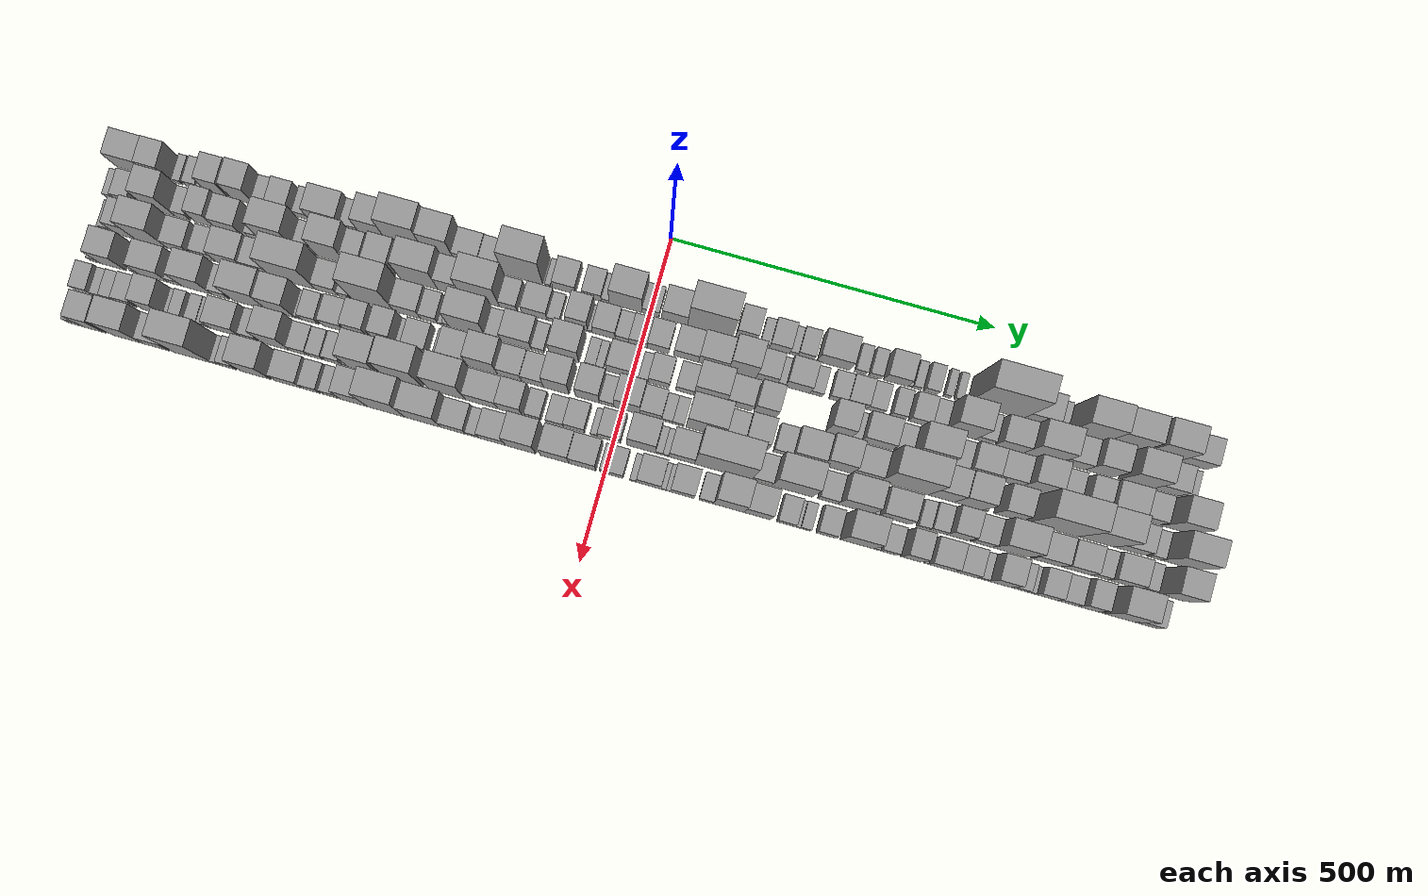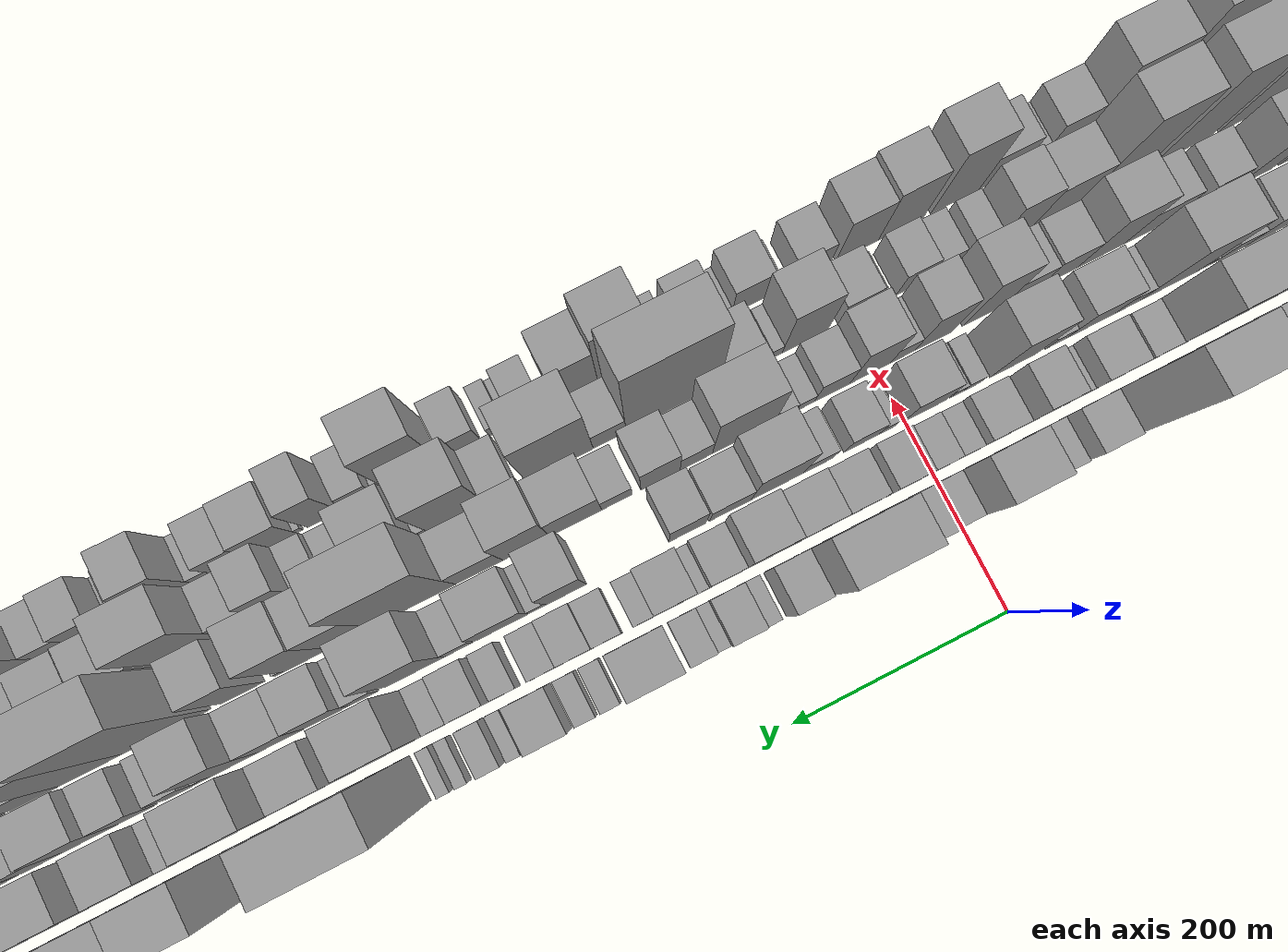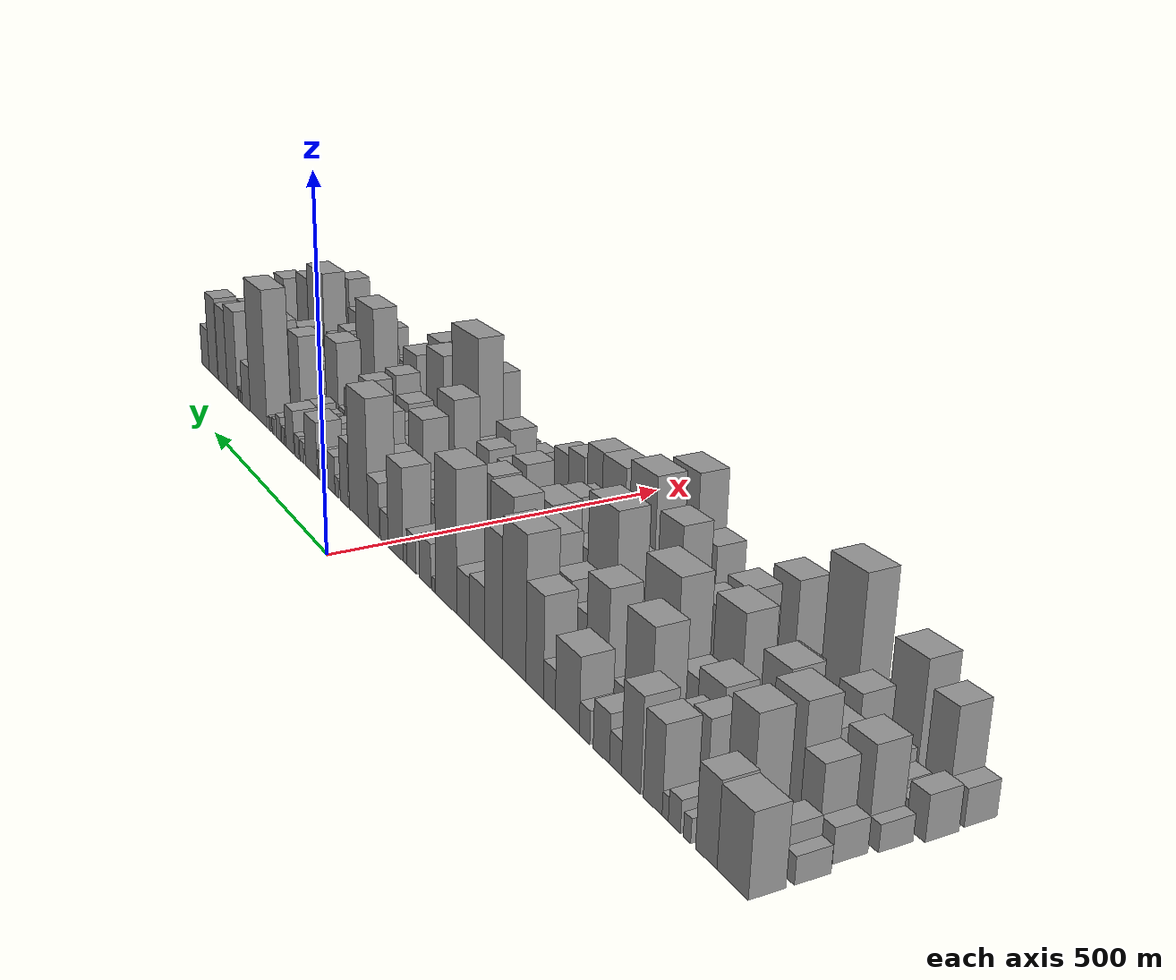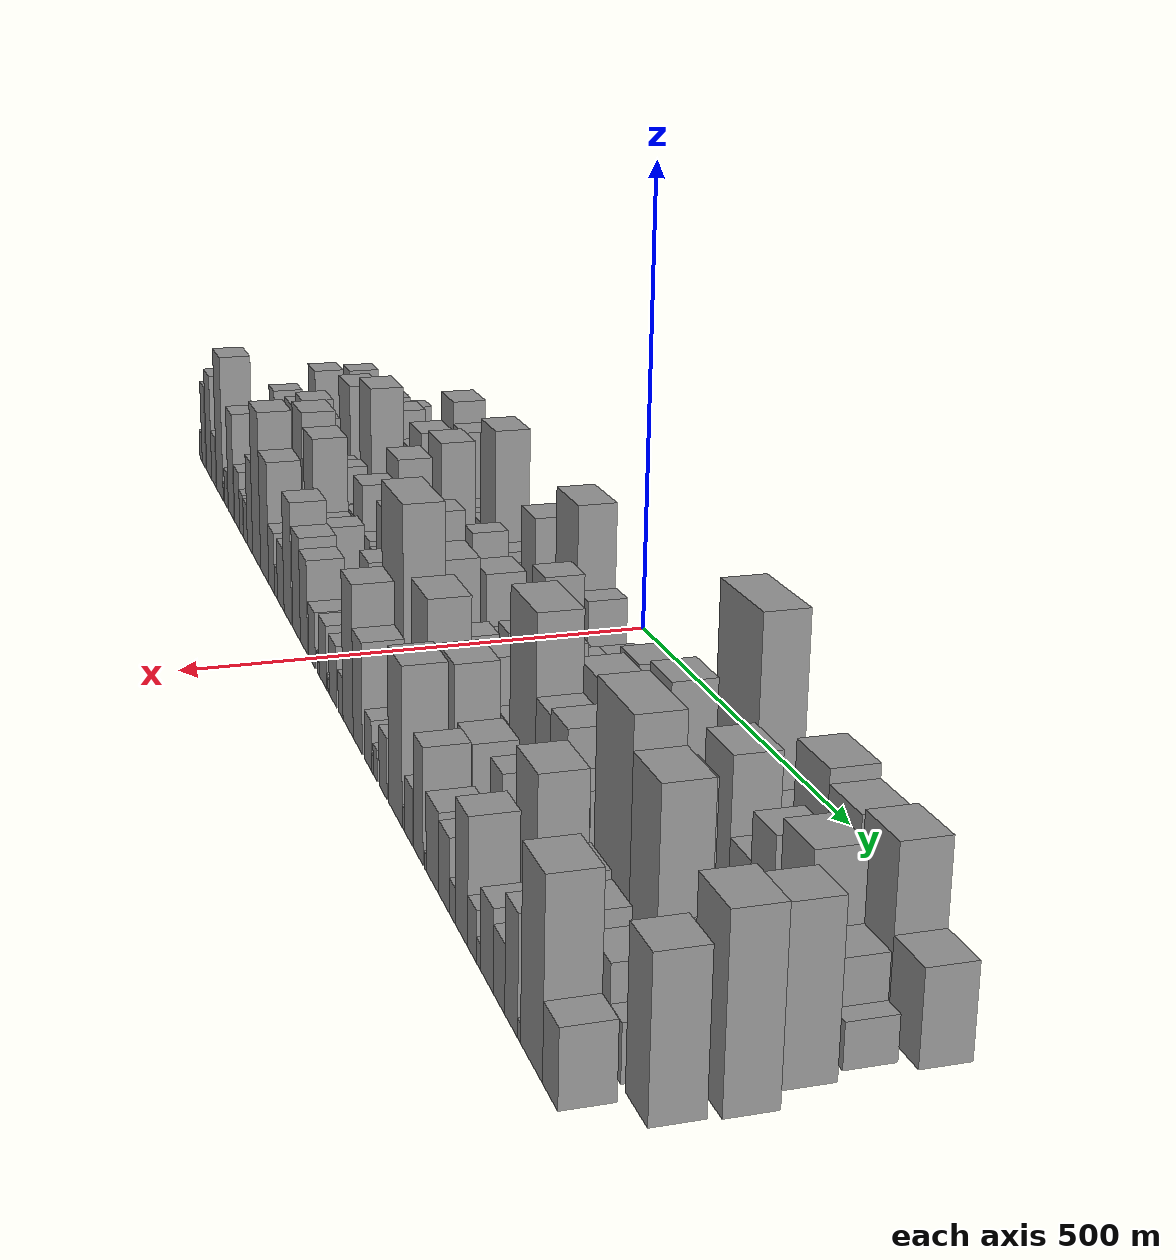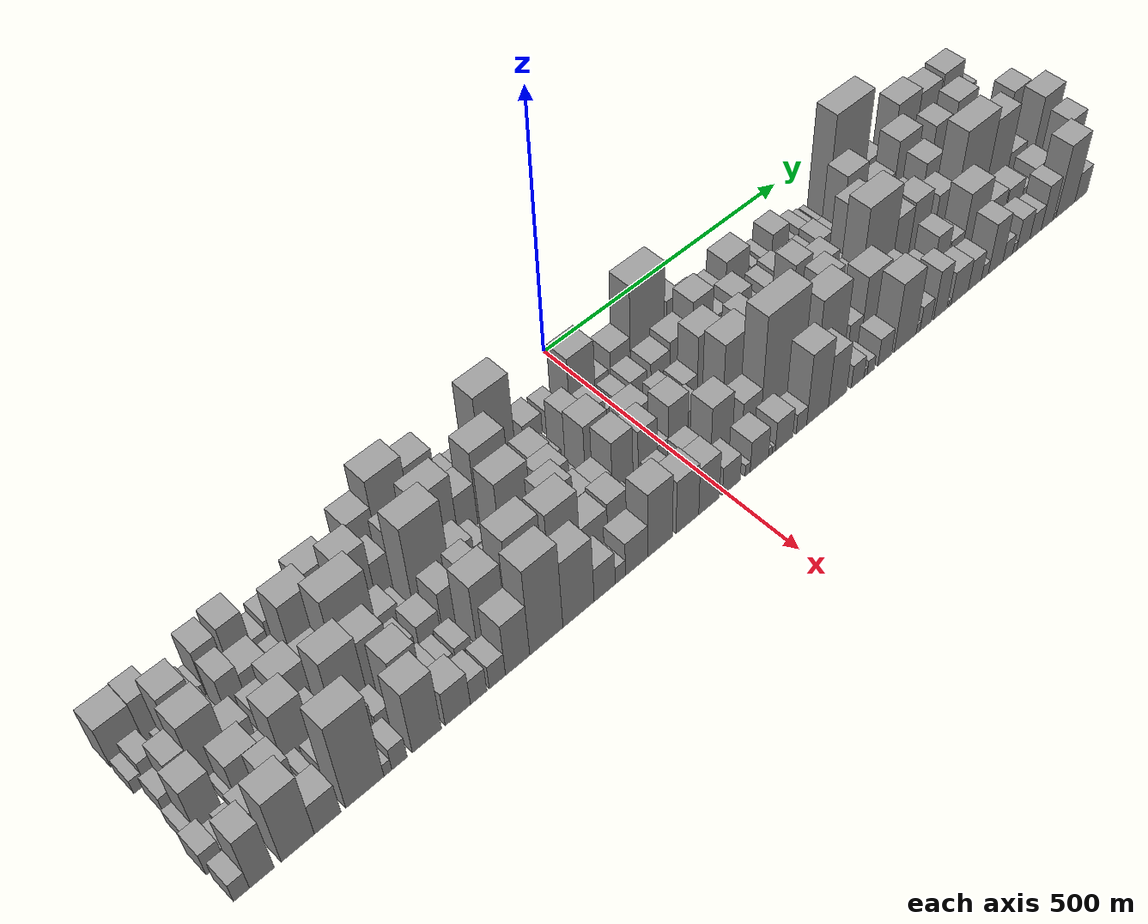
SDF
<sdf version="1.6">
 <world name="default">
  <scene>
   <sky><clouds><speed>12</speed></clouds></sky>
   <ambient>0.4 0.4 0.4 1</ambient>
   <background>0.7 0.7 0.7 1</background>
   <shadows>1</shadows>
  </scene>
  <gravity>0 0 -9.8066</gravity>
  <magnetic_field>6e-06 2.3e-05 -4.2e-05</magnetic_field>
  <physics default="0" name="default_physics" type="ode">
   <ode>
    <solver>
     <type>quick</type>
     <iters>10</iters>
     <sor>1.0</sor>
     <use_dynamic_moi_rescaling>0</use_dynamic_moi_rescaling>
    </solver>
    <constraints>
     <cfm>0</cfm>
     <erp>0.2</erp>
     <contact_max_correcting_vel>100</contact_max_correcting_vel>
     <contact_surface_layer>0.001</contact_surface_layer>
    </constraints>
   </ode>
   <max_step_size>0.004</max_step_size>
   <real_time_factor>1</real_time_factor>
   <real_time_update_rate>250</real_time_update_rate>
  </physics>
  <light name="sun" type="directional">
   <pose>0 0 10 0 0 0</pose>
   <diffuse>0.8 0.8 0.8 1</diffuse>
   <specular>0.2 0.2 0.2 1</specular>
   <attenuation>
    <range>1000</range>
    <constant>0.9</constant>
    <linear>0.01</linear>
    <quadratic>0.001</quadratic>
   </attenuation>
   <direction>-0.5 0.1 -0.9</direction>
  </light>
  <model name="building_1">
   <static>1</static>
   <pose>100.0000 -805.6093 0 0.000000 0.000000 0.000000</pose>
   <link name="link">
    <pose>0 0 45.00 0 0 0</pose>
    <collision name="collision"><geometry><box><size>40.0000 48.7813 90.0000</size></box></geometry></collision>
    <visual name="visual">
     <cast_shadows>0</cast_shadows>
     <geometry><box><size>40.0000 48.7813 90.0000</size></box></geometry>
     <material>
      <script>
       <uri>model://grey_wall/materials/scripts</uri>
       <uri>model://grey_wall/materials/textures</uri>
       <name>vrc/grey_wall</name>
      </script>
     </material>
    </visual>
   </link>
  </model>
  <model name="building_2">
   <static>1</static>
   <pose>100.0000 -763.7412 0 0.000000 0.000000 0.000000</pose>
   <link name="link">
    <pose>0 0 46.50 0 0 0</pose>
    <collision name="collision"><geometry><box><size>40.0000 34.9550 93.0000</size></box></geometry></collision>
    <visual name="visual">
     <cast_shadows>0</cast_shadows>
     <geometry><box><size>40.0000 34.9550 93.0000</size></box></geometry>
     <material>
      <script>
       <uri>model://grey_wall/materials/scripts</uri>
       <uri>model://grey_wall/materials/textures</uri>
       <name>vrc/grey_wall</name>
      </script>
     </material>
    </visual>
   </link>
  </model>
  <model name="building_3">
   <static>1</static>
   <pose>100.0000 -731.9594 0 0.000000 0.000000 0.000000</pose>
   <link name="link">
    <pose>0 0 13.50 0 0 0</pose>
    <collision name="collision"><geometry><box><size>40.0000 12.6085 27.0000</size></box></geometry></collision>
    <visual name="visual">
     <cast_shadows>0</cast_shadows>
     <geometry><box><size>40.0000 12.6085 27.0000</size></box></geometry>
     <material>
      <script>
       <uri>model://grey_wall/materials/scripts</uri>
       <uri>model://grey_wall/materials/textures</uri>
       <name>vrc/grey_wall</name>
      </script>
     </material>
    </visual>
   </link>
  </model>
  <model name="building_4">
   <static>1</static>
   <pose>100.0000 -710.1623 0 0.000000 0.000000 0.000000</pose>
   <link name="link">
    <pose>0 0 18.00 0 0 0</pose>
    <collision name="collision"><geometry><box><size>40.0000 20.9856 36.0000</size></box></geometry></collision>
    <visual name="visual">
     <cast_shadows>0</cast_shadows>
     <geometry><box><size>40.0000 20.9856 36.0000</size></box></geometry>
     <material>
      <script>
       <uri>model://grey_wall/materials/scripts</uri>
       <uri>model://grey_wall/materials/textures</uri>
       <name>vrc/grey_wall</name>
      </script>
     </material>
    </visual>
   </link>
  </model>
  <model name="building_5">
   <static>1</static>
   <pose>100.0000 -694.1890 0 0.000000 0.000000 0.000000</pose>
   <link name="link">
    <pose>0 0 13.50 0 0 0</pose>
    <collision name="collision"><geometry><box><size>40.0000 10.9612 27.0000</size></box></geometry></collision>
    <visual name="visual">
     <cast_shadows>0</cast_shadows>
     <geometry><box><size>40.0000 10.9612 27.0000</size></box></geometry>
     <material>
      <script>
       <uri>model://grey_wall/materials/scripts</uri>
       <uri>model://grey_wall/materials/textures</uri>
       <name>vrc/grey_wall</name>
      </script>
     </material>
    </visual>
   </link>
  </model>
  <model name="building_6">
   <static>1</static>
   <pose>100.0000 -671.6011 0 0.000000 0.000000 0.000000</pose>
   <link name="link">
    <pose>0 0 49.50 0 0 0</pose>
    <collision name="collision"><geometry><box><size>40.0000 34.2147 99.0000</size></box></geometry></collision>
    <visual name="visual">
     <cast_shadows>0</cast_shadows>
     <geometry><box><size>40.0000 34.2147 99.0000</size></box></geometry>
     <material>
      <script>
       <uri>model://grey_wall/materials/scripts</uri>
       <uri>model://grey_wall/materials/textures</uri>
       <name>vrc/grey_wall</name>
      </script>
     </material>
    </visual>
   </link>
  </model>
  <model name="building_7">
   <static>1</static>
   <pose>100.0000 -631.0095 0 0.000000 0.000000 0.000000</pose>
   <link name="link">
    <pose>0 0 54.00 0 0 0</pose>
    <collision name="collision"><geometry><box><size>40.0000 36.9685 108.0000</size></box></geometry></collision>
    <visual name="visual">
     <cast_shadows>0</cast_shadows>
     <geometry><box><size>40.0000 36.9685 108.0000</size></box></geometry>
     <material>
      <script>
       <uri>model://grey_wall/materials/scripts</uri>
       <uri>model://grey_wall/materials/textures</uri>
       <name>vrc/grey_wall</name>
      </script>
     </material>
    </visual>
   </link>
  </model>
  <model name="building_8">
   <static>1</static>
   <pose>100.0000 -601.0338 0 0.000000 0.000000 0.000000</pose>
   <link name="link">
    <pose>0 0 19.50 0 0 0</pose>
    <collision name="collision"><geometry><box><size>40.0000 22.9829 39.0000</size></box></geometry></collision>
    <visual name="visual">
     <cast_shadows>0</cast_shadows>
     <geometry><box><size>40.0000 22.9829 39.0000</size></box></geometry>
     <material>
      <script>
       <uri>model://grey_wall/materials/scripts</uri>
       <uri>model://grey_wall/materials/textures</uri>
       <name>vrc/grey_wall</name>
      </script>
     </material>
    </visual>
   </link>
  </model>
  <model name="building_9">
   <static>1</static>
   <pose>100.0000 -573.0449 0 0.000000 0.000000 0.000000</pose>
   <link name="link">
    <pose>0 0 28.50 0 0 0</pose>
    <collision name="collision"><geometry><box><size>40.0000 32.9949 57.0000</size></box></geometry></collision>
    <visual name="visual">
     <cast_shadows>0</cast_shadows>
     <geometry><box><size>40.0000 32.9949 57.0000</size></box></geometry>
     <material>
      <script>
       <uri>model://grey_wall/materials/scripts</uri>
       <uri>model://grey_wall/materials/textures</uri>
       <name>vrc/grey_wall</name>
      </script>
     </material>
    </visual>
   </link>
  </model>
  <model name="building_10">
   <static>1</static>
   <pose>100.0000 -538.4916 0 0.000000 0.000000 0.000000</pose>
   <link name="link">
    <pose>0 0 19.50 0 0 0</pose>
    <collision name="collision"><geometry><box><size>40.0000 22.1117 39.0000</size></box></geometry></collision>
    <visual name="visual">
     <cast_shadows>0</cast_shadows>
     <geometry><box><size>40.0000 22.1117 39.0000</size></box></geometry>
     <material>
      <script>
       <uri>model://grey_wall/materials/scripts</uri>
       <uri>model://grey_wall/materials/textures</uri>
       <name>vrc/grey_wall</name>
      </script>
     </material>
    </visual>
   </link>
  </model>
  <model name="building_11">
   <static>1</static>
   <pose>100.0000 -501.2214 0 0.000000 0.000000 0.000000</pose>
   <link name="link">
    <pose>0 0 45.00 0 0 0</pose>
    <collision name="collision"><geometry><box><size>40.0000 52.4288 90.0000</size></box></geometry></collision>
    <visual name="visual">
     <cast_shadows>0</cast_shadows>
     <geometry><box><size>40.0000 52.4288 90.0000</size></box></geometry>
     <material>
      <script>
       <uri>model://grey_wall/materials/scripts</uri>
       <uri>model://grey_wall/materials/textures</uri>
       <name>vrc/grey_wall</name>
      </script>
     </material>
    </visual>
   </link>
  </model>
  <model name="building_12">
   <static>1</static>
   <pose>100.0000 -461.5591 0 0.000000 0.000000 0.000000</pose>
   <link name="link">
    <pose>0 0 24.00 0 0 0</pose>
    <collision name="collision"><geometry><box><size>40.0000 26.8958 48.0000</size></box></geometry></collision>
    <visual name="visual">
     <cast_shadows>0</cast_shadows>
     <geometry><box><size>40.0000 26.8958 48.0000</size></box></geometry>
     <material>
      <script>
       <uri>model://grey_wall/materials/scripts</uri>
       <uri>model://grey_wall/materials/textures</uri>
       <name>vrc/grey_wall</name>
      </script>
     </material>
    </visual>
   </link>
  </model>
  <model name="building_13">
   <static>1</static>
   <pose>100.0000 -427.4306 0 0.000000 0.000000 0.000000</pose>
   <link name="link">
    <pose>0 0 61.50 0 0 0</pose>
    <collision name="collision"><geometry><box><size>40.0000 41.3613 123.0000</size></box></geometry></collision>
    <visual name="visual">
     <cast_shadows>0</cast_shadows>
     <geometry><box><size>40.0000 41.3613 123.0000</size></box></geometry>
     <material>
      <script>
       <uri>model://grey_wall/materials/scripts</uri>
       <uri>model://grey_wall/materials/textures</uri>
       <name>vrc/grey_wall</name>
      </script>
     </material>
    </visual>
   </link>
  </model>
  <model name="building_14">
   <static>1</static>
   <pose>100.0000 -377.6617 0 0.000000 0.000000 0.000000</pose>
   <link name="link">
    <pose>0 0 88.50 0 0 0</pose>
    <collision name="collision"><geometry><box><size>40.0000 58.1763 177.0000</size></box></geometry></collision>
    <visual name="visual">
     <cast_shadows>0</cast_shadows>
     <geometry><box><size>40.0000 58.1763 177.0000</size></box></geometry>
     <material>
      <script>
       <uri>model://grey_wall/materials/scripts</uri>
       <uri>model://grey_wall/materials/textures</uri>
       <name>vrc/grey_wall</name>
      </script>
     </material>
    </visual>
   </link>
  </model>
  <model name="building_15">
   <static>1</static>
   <pose>100.0000 -325.2253 0 0.000000 0.000000 0.000000</pose>
   <link name="link">
    <pose>0 0 75.00 0 0 0</pose>
    <collision name="collision"><geometry><box><size>40.0000 46.6966 150.0000</size></box></geometry></collision>
    <visual name="visual">
     <cast_shadows>0</cast_shadows>
     <geometry><box><size>40.0000 46.6966 150.0000</size></box></geometry>
     <material>
      <script>
       <uri>model://grey_wall/materials/scripts</uri>
       <uri>model://grey_wall/materials/textures</uri>
       <name>vrc/grey_wall</name>
      </script>
     </material>
    </visual>
   </link>
  </model>
  <model name="building_16">
   <static>1</static>
   <pose>100.0000 -282.1139 0 0.000000 0.000000 0.000000</pose>
   <link name="link">
    <pose>0 0 34.50 0 0 0</pose>
    <collision name="collision"><geometry><box><size>40.0000 39.5261 69.0000</size></box></geometry></collision>
    <visual name="visual">
     <cast_shadows>0</cast_shadows>
     <geometry><box><size>40.0000 39.5261 69.0000</size></box></geometry>
     <material>
      <script>
       <uri>model://grey_wall/materials/scripts</uri>
       <uri>model://grey_wall/materials/textures</uri>
       <name>vrc/grey_wall</name>
      </script>
     </material>
    </visual>
   </link>
  </model>
  <model name="building_17">
   <static>1</static>
   <pose>100.0000 -244.3555 0 0.000000 0.000000 0.000000</pose>
   <link name="link">
    <pose>0 0 31.50 0 0 0</pose>
    <collision name="collision"><geometry><box><size>40.0000 35.9908 63.0000</size></box></geometry></collision>
    <visual name="visual">
     <cast_shadows>0</cast_shadows>
     <geometry><box><size>40.0000 35.9908 63.0000</size></box></geometry>
     <material>
      <script>
       <uri>model://grey_wall/materials/scripts</uri>
       <uri>model://grey_wall/materials/textures</uri>
       <name>vrc/grey_wall</name>
      </script>
     </material>
    </visual>
   </link>
  </model>
  <model name="building_18">
   <static>1</static>
   <pose>100.0000 -195.5753 0 0.000000 0.000000 0.000000</pose>
   <link name="link">
    <pose>0 0 93.00 0 0 0</pose>
    <collision name="collision"><geometry><box><size>40.0000 61.5694 186.0000</size></box></geometry></collision>
    <visual name="visual">
     <cast_shadows>0</cast_shadows>
     <geometry><box><size>40.0000 61.5694 186.0000</size></box></geometry>
     <material>
      <script>
       <uri>model://grey_wall/materials/scripts</uri>
       <uri>model://grey_wall/materials/textures</uri>
       <name>vrc/grey_wall</name>
      </script>
     </material>
    </visual>
   </link>
  </model>
  <model name="building_19">
   <static>1</static>
   <pose>100.0000 -157.3529 0 0.000000 0.000000 0.000000</pose>
   <link name="link">
    <pose>0 0 9.00 0 0 0</pose>
    <collision name="collision"><geometry><box><size>40.0000 8.8755 18.0000</size></box></geometry></collision>
    <visual name="visual">
     <cast_shadows>0</cast_shadows>
     <geometry><box><size>40.0000 8.8755 18.0000</size></box></geometry>
     <material>
      <script>
       <uri>model://grey_wall/materials/scripts</uri>
       <uri>model://grey_wall/materials/textures</uri>
       <name>vrc/grey_wall</name>
      </script>
     </material>
    </visual>
   </link>
  </model>
  <model name="building_20">
   <static>1</static>
   <pose>100.0000 -132.1527 0 0.000000 0.000000 0.000000</pose>
   <link name="link">
    <pose>0 0 30.00 0 0 0</pose>
    <collision name="collision"><geometry><box><size>40.0000 35.5249 60.0000</size></box></geometry></collision>
    <visual name="visual">
     <cast_shadows>0</cast_shadows>
     <geometry><box><size>40.0000 35.5249 60.0000</size></box></geometry>
     <material>
      <script>
       <uri>model://grey_wall/materials/scripts</uri>
       <uri>model://grey_wall/materials/textures</uri>
       <name>vrc/grey_wall</name>
      </script>
     </material>
    </visual>
   </link>
  </model>
  <model name="building_21">
   <static>1</static>
   <pose>100.0000 -89.5267 0 0.000000 0.000000 0.000000</pose>
   <link name="link">
    <pose>0 0 25.50 0 0 0</pose>
    <collision name="collision"><geometry><box><size>40.0000 29.7271 51.0000</size></box></geometry></collision>
    <visual name="visual">
     <cast_shadows>0</cast_shadows>
     <geometry><box><size>40.0000 29.7271 51.0000</size></box></geometry>
     <material>
      <script>
       <uri>model://grey_wall/materials/scripts</uri>
       <uri>model://grey_wall/materials/textures</uri>
       <name>vrc/grey_wall</name>
      </script>
     </material>
    </visual>
   </link>
  </model>
  <model name="building_22">
   <static>1</static>
   <pose>100.0000 -68.5226 0 0.000000 0.000000 0.000000</pose>
   <link name="link">
    <pose>0 0 13.50 0 0 0</pose>
    <collision name="collision"><geometry><box><size>40.0000 12.2811 27.0000</size></box></geometry></collision>
    <visual name="visual">
     <cast_shadows>0</cast_shadows>
     <geometry><box><size>40.0000 12.2811 27.0000</size></box></geometry>
     <material>
      <script>
       <uri>model://grey_wall/materials/scripts</uri>
       <uri>model://grey_wall/materials/textures</uri>
       <name>vrc/grey_wall</name>
      </script>
     </material>
    </visual>
   </link>
  </model>
  <model name="building_23">
   <static>1</static>
   <pose>100.0000 -37.1999 0 0.000000 0.000000 0.000000</pose>
   <link name="link">
    <pose>0 0 64.50 0 0 0</pose>
    <collision name="collision"><geometry><box><size>40.0000 50.3643 129.0000</size></box></geometry></collision>
    <visual name="visual">
     <cast_shadows>0</cast_shadows>
     <geometry><box><size>40.0000 50.3643 129.0000</size></box></geometry>
     <material>
      <script>
       <uri>model://grey_wall/materials/scripts</uri>
       <uri>model://grey_wall/materials/textures</uri>
       <name>vrc/grey_wall</name>
      </script>
     </material>
    </visual>
   </link>
  </model>
  <model name="building_24">
   <static>1</static>
   <pose>100.0000 1.3335 0 0.000000 0.000000 0.000000</pose>
   <link name="link">
    <pose>0 0 22.50 0 0 0</pose>
    <collision name="collision"><geometry><box><size>40.0000 26.7026 45.0000</size></box></geometry></collision>
    <visual name="visual">
     <cast_shadows>0</cast_shadows>
     <geometry><box><size>40.0000 26.7026 45.0000</size></box></geometry>
     <material>
      <script>
       <uri>model://grey_wall/materials/scripts</uri>
       <uri>model://grey_wall/materials/textures</uri>
       <name>vrc/grey_wall</name>
      </script>
     </material>
    </visual>
   </link>
  </model>
  <model name="building_25">
   <static>1</static>
   <pose>100.0000 38.5703 0 0.000000 0.000000 0.000000</pose>
   <link name="link">
    <pose>0 0 39.00 0 0 0</pose>
    <collision name="collision"><geometry><box><size>40.0000 39.7708 78.0000</size></box></geometry></collision>
    <visual name="visual">
     <cast_shadows>0</cast_shadows>
     <geometry><box><size>40.0000 39.7708 78.0000</size></box></geometry>
     <material>
      <script>
       <uri>model://grey_wall/materials/scripts</uri>
       <uri>model://grey_wall/materials/textures</uri>
       <name>vrc/grey_wall</name>
      </script>
     </material>
    </visual>
   </link>
  </model>
  <model name="building_26">
   <static>1</static>
   <pose>100.0000 93.1584 0 0.000000 0.000000 0.000000</pose>
   <link name="link">
    <pose>0 0 91.50 0 0 0</pose>
    <collision name="collision"><geometry><box><size>40.0000 69.4055 183.0000</size></box></geometry></collision>
    <visual name="visual">
     <cast_shadows>0</cast_shadows>
     <geometry><box><size>40.0000 69.4055 183.0000</size></box></geometry>
     <material>
      <script>
       <uri>model://grey_wall/materials/scripts</uri>
       <uri>model://grey_wall/materials/textures</uri>
       <name>vrc/grey_wall</name>
      </script>
     </material>
    </visual>
   </link>
  </model>
  <model name="building_27">
   <static>1</static>
   <pose>100.0000 147.6372 0 0.000000 0.000000 0.000000</pose>
   <link name="link">
    <pose>0 0 48.00 0 0 0</pose>
    <collision name="collision"><geometry><box><size>40.0000 31.5521 96.0000</size></box></geometry></collision>
    <visual name="visual">
     <cast_shadows>0</cast_shadows>
     <geometry><box><size>40.0000 31.5521 96.0000</size></box></geometry>
     <material>
      <script>
       <uri>model://grey_wall/materials/scripts</uri>
       <uri>model://grey_wall/materials/textures</uri>
       <name>vrc/grey_wall</name>
      </script>
     </material>
    </visual>
   </link>
  </model>
  <model name="building_28">
   <static>1</static>
   <pose>100.0000 176.9295 0 0.000000 0.000000 0.000000</pose>
   <link name="link">
    <pose>0 0 15.00 0 0 0</pose>
    <collision name="collision"><geometry><box><size>40.0000 15.0325 30.0000</size></box></geometry></collision>
    <visual name="visual">
     <cast_shadows>0</cast_shadows>
     <geometry><box><size>40.0000 15.0325 30.0000</size></box></geometry>
     <material>
      <script>
       <uri>model://grey_wall/materials/scripts</uri>
       <uri>model://grey_wall/materials/textures</uri>
       <name>vrc/grey_wall</name>
      </script>
     </material>
    </visual>
   </link>
  </model>
  <model name="building_29">
   <static>1</static>
   <pose>100.0000 199.9222 0 0.000000 0.000000 0.000000</pose>
   <link name="link">
    <pose>0 0 28.50 0 0 0</pose>
    <collision name="collision"><geometry><box><size>40.0000 30.9528 57.0000</size></box></geometry></collision>
    <visual name="visual">
     <cast_shadows>0</cast_shadows>
     <geometry><box><size>40.0000 30.9528 57.0000</size></box></geometry>
     <material>
      <script>
       <uri>model://grey_wall/materials/scripts</uri>
       <uri>model://grey_wall/materials/textures</uri>
       <name>vrc/grey_wall</name>
      </script>
     </material>
    </visual>
   </link>
  </model>
  <model name="building_30">
   <static>1</static>
   <pose>100.0000 221.6802 0 0.000000 0.000000 0.000000</pose>
   <link name="link">
    <pose>0 0 13.50 0 0 0</pose>
    <collision name="collision"><geometry><box><size>40.0000 12.5633 27.0000</size></box></geometry></collision>
    <visual name="visual">
     <cast_shadows>0</cast_shadows>
     <geometry><box><size>40.0000 12.5633 27.0000</size></box></geometry>
     <material>
      <script>
       <uri>model://grey_wall/materials/scripts</uri>
       <uri>model://grey_wall/materials/textures</uri>
       <name>vrc/grey_wall</name>
      </script>
     </material>
    </visual>
   </link>
  </model>
  <model name="building_31">
   <static>1</static>
   <pose>100.0000 240.3744 0 0.000000 0.000000 0.000000</pose>
   <link name="link">
    <pose>0 0 22.50 0 0 0</pose>
    <collision name="collision"><geometry><box><size>40.0000 24.8252 45.0000</size></box></geometry></collision>
    <visual name="visual">
     <cast_shadows>0</cast_shadows>
     <geometry><box><size>40.0000 24.8252 45.0000</size></box></geometry>
     <material>
      <script>
       <uri>model://grey_wall/materials/scripts</uri>
       <uri>model://grey_wall/materials/textures</uri>
       <name>vrc/grey_wall</name>
      </script>
     </material>
    </visual>
   </link>
  </model>
  <model name="building_32">
   <static>1</static>
   <pose>100.0000 282.8992 0 0.000000 0.000000 0.000000</pose>
   <link name="link">
    <pose>0 0 42.00 0 0 0</pose>
    <collision name="collision"><geometry><box><size>40.0000 50.2242 84.0000</size></box></geometry></collision>
    <visual name="visual">
     <cast_shadows>0</cast_shadows>
     <geometry><box><size>40.0000 50.2242 84.0000</size></box></geometry>
     <material>
      <script>
       <uri>model://grey_wall/materials/scripts</uri>
       <uri>model://grey_wall/materials/textures</uri>
       <name>vrc/grey_wall</name>
      </script>
     </material>
    </visual>
   </link>
  </model>
  <model name="building_33">
   <static>1</static>
   <pose>100.0000 323.9322 0 0.000000 0.000000 0.000000</pose>
   <link name="link">
    <pose>0 0 16.50 0 0 0</pose>
    <collision name="collision"><geometry><box><size>40.0000 17.8419 33.0000</size></box></geometry></collision>
    <visual name="visual">
     <cast_shadows>0</cast_shadows>
     <geometry><box><size>40.0000 17.8419 33.0000</size></box></geometry>
     <material>
      <script>
       <uri>model://grey_wall/materials/scripts</uri>
       <uri>model://grey_wall/materials/textures</uri>
       <name>vrc/grey_wall</name>
      </script>
     </material>
    </visual>
   </link>
  </model>
  <model name="building_34">
   <static>1</static>
   <pose>100.0000 346.2792 0 0.000000 0.000000 0.000000</pose>
   <link name="link">
    <pose>0 0 18.00 0 0 0</pose>
    <collision name="collision"><geometry><box><size>40.0000 18.8521 36.0000</size></box></geometry></collision>
    <visual name="visual">
     <cast_shadows>0</cast_shadows>
     <geometry><box><size>40.0000 18.8521 36.0000</size></box></geometry>
     <material>
      <script>
       <uri>model://grey_wall/materials/scripts</uri>
       <uri>model://grey_wall/materials/textures</uri>
       <name>vrc/grey_wall</name>
      </script>
     </material>
    </visual>
   </link>
  </model>
  <model name="building_35">
   <static>1</static>
   <pose>100.0000 378.3489 0 0.000000 0.000000 0.000000</pose>
   <link name="link">
    <pose>0 0 34.50 0 0 0</pose>
    <collision name="collision"><geometry><box><size>40.0000 37.2872 69.0000</size></box></geometry></collision>
    <visual name="visual">
     <cast_shadows>0</cast_shadows>
     <geometry><box><size>40.0000 37.2872 69.0000</size></box></geometry>
     <material>
      <script>
       <uri>model://grey_wall/materials/scripts</uri>
       <uri>model://grey_wall/materials/textures</uri>
       <name>vrc/grey_wall</name>
      </script>
     </material>
    </visual>
   </link>
  </model>
  <model name="building_36">
   <static>1</static>
   <pose>100.0000 400.3364 0 0.000000 0.000000 0.000000</pose>
   <link name="link">
    <pose>0 0 7.50 0 0 0</pose>
    <collision name="collision"><geometry><box><size>40.0000 6.6877 15.0000</size></box></geometry></collision>
    <visual name="visual">
     <cast_shadows>0</cast_shadows>
     <geometry><box><size>40.0000 6.6877 15.0000</size></box></geometry>
     <material>
      <script>
       <uri>model://grey_wall/materials/scripts</uri>
       <uri>model://grey_wall/materials/textures</uri>
       <name>vrc/grey_wall</name>
      </script>
     </material>
    </visual>
   </link>
  </model>
  <model name="building_37">
   <static>1</static>
   <pose>100.0000 410.1484 0 0.000000 0.000000 0.000000</pose>
   <link name="link">
    <pose>0 0 13.50 0 0 0</pose>
    <collision name="collision"><geometry><box><size>40.0000 12.9362 27.0000</size></box></geometry></collision>
    <visual name="visual">
     <cast_shadows>0</cast_shadows>
     <geometry><box><size>40.0000 12.9362 27.0000</size></box></geometry>
     <material>
      <script>
       <uri>model://grey_wall/materials/scripts</uri>
       <uri>model://grey_wall/materials/textures</uri>
       <name>vrc/grey_wall</name>
      </script>
     </material>
    </visual>
   </link>
  </model>
  <model name="building_38">
   <static>1</static>
   <pose>100.0000 431.2023 0 0.000000 0.000000 0.000000</pose>
   <link name="link">
    <pose>0 0 19.50 0 0 0</pose>
    <collision name="collision"><geometry><box><size>40.0000 21.1716 39.0000</size></box></geometry></collision>
    <visual name="visual">
     <cast_shadows>0</cast_shadows>
     <geometry><box><size>40.0000 21.1716 39.0000</size></box></geometry>
     <material>
      <script>
       <uri>model://grey_wall/materials/scripts</uri>
       <uri>model://grey_wall/materials/textures</uri>
       <name>vrc/grey_wall</name>
      </script>
     </material>
    </visual>
   </link>
  </model>
  <model name="building_39">
   <static>1</static>
   <pose>100.0000 456.4045 0 0.000000 0.000000 0.000000</pose>
   <link name="link">
    <pose>0 0 13.50 0 0 0</pose>
    <collision name="collision"><geometry><box><size>40.0000 11.2328 27.0000</size></box></geometry></collision>
    <visual name="visual">
     <cast_shadows>0</cast_shadows>
     <geometry><box><size>40.0000 11.2328 27.0000</size></box></geometry>
     <material>
      <script>
       <uri>model://grey_wall/materials/scripts</uri>
       <uri>model://grey_wall/materials/textures</uri>
       <name>vrc/grey_wall</name>
      </script>
     </material>
    </visual>
   </link>
  </model>
  <model name="building_40">
   <static>1</static>
   <pose>100.0000 472.6776 0 0.000000 0.000000 0.000000</pose>
   <link name="link">
    <pose>0 0 12.00 0 0 0</pose>
    <collision name="collision"><geometry><box><size>40.0000 11.3134 24.0000</size></box></geometry></collision>
    <visual name="visual">
     <cast_shadows>0</cast_shadows>
     <geometry><box><size>40.0000 11.3134 24.0000</size></box></geometry>
     <material>
      <script>
       <uri>model://grey_wall/materials/scripts</uri>
       <uri>model://grey_wall/materials/textures</uri>
       <name>vrc/grey_wall</name>
      </script>
     </material>
    </visual>
   </link>
  </model>
  <model name="building_41">
   <static>1</static>
   <pose>100.0000 530.1198 0 0.000000 0.000000 0.000000</pose>
   <link name="link">
    <pose>0 0 112.50 0 0 0</pose>
    <collision name="collision"><geometry><box><size>40.0000 85.5712 225.0000</size></box></geometry></collision>
    <visual name="visual">
     <cast_shadows>0</cast_shadows>
     <geometry><box><size>40.0000 85.5712 225.0000</size></box></geometry>
     <material>
      <script>
       <uri>model://grey_wall/materials/scripts</uri>
       <uri>model://grey_wall/materials/textures</uri>
       <name>vrc/grey_wall</name>
      </script>
     </material>
    </visual>
   </link>
  </model>
  <model name="building_42">
   <static>1</static>
   <pose>100.0000 595.1316 0 0.000000 0.000000 0.000000</pose>
   <link name="link">
    <pose>0 0 37.50 0 0 0</pose>
    <collision name="collision"><geometry><box><size>40.0000 44.4523 75.0000</size></box></geometry></collision>
    <visual name="visual">
     <cast_shadows>0</cast_shadows>
     <geometry><box><size>40.0000 44.4523 75.0000</size></box></geometry>
     <material>
      <script>
       <uri>model://grey_wall/materials/scripts</uri>
       <uri>model://grey_wall/materials/textures</uri>
       <name>vrc/grey_wall</name>
      </script>
     </material>
    </visual>
   </link>
  </model>
  <model name="building_43">
   <static>1</static>
   <pose>100.0000 622.2904 0 0.000000 0.000000 0.000000</pose>
   <link name="link">
    <pose>0 0 10.50 0 0 0</pose>
    <collision name="collision"><geometry><box><size>40.0000 9.8653 21.0000</size></box></geometry></collision>
    <visual name="visual">
     <cast_shadows>0</cast_shadows>
     <geometry><box><size>40.0000 9.8653 21.0000</size></box></geometry>
     <material>
      <script>
       <uri>model://grey_wall/materials/scripts</uri>
       <uri>model://grey_wall/materials/textures</uri>
       <name>vrc/grey_wall</name>
      </script>
     </material>
    </visual>
   </link>
  </model>
  <model name="building_44">
   <static>1</static>
   <pose>100.0000 632.1408 0 0.000000 0.000000 0.000000</pose>
   <link name="link">
    <pose>0 0 12.00 0 0 0</pose>
    <collision name="collision"><geometry><box><size>40.0000 9.8353 24.0000</size></box></geometry></collision>
    <visual name="visual">
     <cast_shadows>0</cast_shadows>
     <geometry><box><size>40.0000 9.8353 24.0000</size></box></geometry>
     <material>
      <script>
       <uri>model://grey_wall/materials/scripts</uri>
       <uri>model://grey_wall/materials/textures</uri>
       <name>vrc/grey_wall</name>
      </script>
     </material>
    </visual>
   </link>
  </model>
  <model name="building_45">
   <static>1</static>
   <pose>100.0000 670.4253 0 0.000000 0.000000 0.000000</pose>
   <link name="link">
    <pose>0 0 75.00 0 0 0</pose>
    <collision name="collision"><geometry><box><size>40.0000 56.7336 150.0000</size></box></geometry></collision>
    <visual name="visual">
     <cast_shadows>0</cast_shadows>
     <geometry><box><size>40.0000 56.7336 150.0000</size></box></geometry>
     <material>
      <script>
       <uri>model://grey_wall/materials/scripts</uri>
       <uri>model://grey_wall/materials/textures</uri>
       <name>vrc/grey_wall</name>
      </script>
     </material>
    </visual>
   </link>
  </model>
  <model name="building_46">
   <static>1</static>
   <pose>100.0000 725.0157 0 0.000000 0.000000 0.000000</pose>
   <link name="link">
    <pose>0 0 69.00 0 0 0</pose>
    <collision name="collision"><geometry><box><size>40.0000 52.4473 138.0000</size></box></geometry></collision>
    <visual name="visual">
     <cast_shadows>0</cast_shadows>
     <geometry><box><size>40.0000 52.4473 138.0000</size></box></geometry>
     <material>
      <script>
       <uri>model://grey_wall/materials/scripts</uri>
       <uri>model://grey_wall/materials/textures</uri>
       <name>vrc/grey_wall</name>
      </script>
     </material>
    </visual>
   </link>
  </model>
  <model name="building_47">
   <static>1</static>
   <pose>100.0000 780.8229 0 0.000000 0.000000 0.000000</pose>
   <link name="link">
    <pose>0 0 72.00 0 0 0</pose>
    <collision name="collision"><geometry><box><size>40.0000 51.1670 144.0000</size></box></geometry></collision>
    <visual name="visual">
     <cast_shadows>0</cast_shadows>
     <geometry><box><size>40.0000 51.1670 144.0000</size></box></geometry>
     <material>
      <script>
       <uri>model://grey_wall/materials/scripts</uri>
       <uri>model://grey_wall/materials/textures</uri>
       <name>vrc/grey_wall</name>
      </script>
     </material>
    </visual>
   </link>
  </model>
  <model name="building_48">
   <static>1</static>
   <pose>100.0000 828.6658 0 0.000000 0.000000 0.000000</pose>
   <link name="link">
    <pose>0 0 37.50 0 0 0</pose>
    <collision name="collision"><geometry><box><size>40.0000 44.5188 75.0000</size></box></geometry></collision>
    <visual name="visual">
     <cast_shadows>0</cast_shadows>
     <geometry><box><size>40.0000 44.5188 75.0000</size></box></geometry>
     <material>
      <script>
       <uri>model://grey_wall/materials/scripts</uri>
       <uri>model://grey_wall/materials/textures</uri>
       <name>vrc/grey_wall</name>
      </script>
     </material>
    </visual>
   </link>
  </model>
  <model name="building_49">
   <static>1</static>
   <pose>149.0000 -821.7969 0 0.000000 0.000000 0.000000</pose>
   <link name="link">
    <pose>0 0 15.00 0 0 0</pose>
    <collision name="collision"><geometry><box><size>40.0000 16.4061 30.0000</size></box></geometry></collision>
    <visual name="visual">
     <cast_shadows>0</cast_shadows>
     <geometry><box><size>40.0000 16.4061 30.0000</size></box></geometry>
     <material>
      <script>
       <uri>model://grey_wall/materials/scripts</uri>
       <uri>model://grey_wall/materials/textures</uri>
       <name>vrc/grey_wall</name>
      </script>
     </material>
    </visual>
   </link>
  </model>
  <model name="building_50">
   <static>1</static>
   <pose>149.0000 -799.8509 0 0.000000 0.000000 0.000000</pose>
   <link name="link">
    <pose>0 0 25.50 0 0 0</pose>
    <collision name="collision"><geometry><box><size>40.0000 27.4859 51.0000</size></box></geometry></collision>
    <visual name="visual">
     <cast_shadows>0</cast_shadows>
     <geometry><box><size>40.0000 27.4859 51.0000</size></box></geometry>
     <material>
      <script>
       <uri>model://grey_wall/materials/scripts</uri>
       <uri>model://grey_wall/materials/textures</uri>
       <name>vrc/grey_wall</name>
      </script>
     </material>
    </visual>
   </link>
  </model>
  <model name="building_51">
   <static>1</static>
   <pose>149.0000 -776.9846 0 0.000000 0.000000 0.000000</pose>
   <link name="link">
    <pose>0 0 7.50 0 0 0</pose>
    <collision name="collision"><geometry><box><size>40.0000 6.2467 15.0000</size></box></geometry></collision>
    <visual name="visual">
     <cast_shadows>0</cast_shadows>
     <geometry><box><size>40.0000 6.2467 15.0000</size></box></geometry>
     <material>
      <script>
       <uri>model://grey_wall/materials/scripts</uri>
       <uri>model://grey_wall/materials/textures</uri>
       <name>vrc/grey_wall</name>
      </script>
     </material>
    </visual>
   </link>
  </model>
  <model name="building_52">
   <static>1</static>
   <pose>149.0000 -768.4472 0 0.000000 0.000000 0.000000</pose>
   <link name="link">
    <pose>0 0 13.50 0 0 0</pose>
    <collision name="collision"><geometry><box><size>40.0000 10.8280 27.0000</size></box></geometry></collision>
    <visual name="visual">
     <cast_shadows>0</cast_shadows>
     <geometry><box><size>40.0000 10.8280 27.0000</size></box></geometry>
     <material>
      <script>
       <uri>model://grey_wall/materials/scripts</uri>
       <uri>model://grey_wall/materials/textures</uri>
       <name>vrc/grey_wall</name>
      </script>
     </material>
    </visual>
   </link>
  </model>
  <model name="building_53">
   <static>1</static>
   <pose>149.0000 -742.2719 0 0.000000 0.000000 0.000000</pose>
   <link name="link">
    <pose>0 0 69.00 0 0 0</pose>
    <collision name="collision"><geometry><box><size>40.0000 41.5226 138.0000</size></box></geometry></collision>
    <visual name="visual">
     <cast_shadows>0</cast_shadows>
     <geometry><box><size>40.0000 41.5226 138.0000</size></box></geometry>
     <material>
      <script>
       <uri>model://grey_wall/materials/scripts</uri>
       <uri>model://grey_wall/materials/textures</uri>
       <name>vrc/grey_wall</name>
      </script>
     </material>
    </visual>
   </link>
  </model>
  <model name="building_54">
   <static>1</static>
   <pose>149.0000 -709.9902 0 0.000000 0.000000 0.000000</pose>
   <link name="link">
    <pose>0 0 22.50 0 0 0</pose>
    <collision name="collision"><geometry><box><size>40.0000 23.0407 45.0000</size></box></geometry></collision>
    <visual name="visual">
     <cast_shadows>0</cast_shadows>
     <geometry><box><size>40.0000 23.0407 45.0000</size></box></geometry>
     <material>
      <script>
       <uri>model://grey_wall/materials/scripts</uri>
       <uri>model://grey_wall/materials/textures</uri>
       <name>vrc/grey_wall</name>
      </script>
     </material>
    </visual>
   </link>
  </model>
  <model name="building_55">
   <static>1</static>
   <pose>149.0000 -675.2562 0 0.000000 0.000000 0.000000</pose>
   <link name="link">
    <pose>0 0 46.50 0 0 0</pose>
    <collision name="collision"><geometry><box><size>40.0000 30.4271 93.0000</size></box></geometry></collision>
    <visual name="visual">
     <cast_shadows>0</cast_shadows>
     <geometry><box><size>40.0000 30.4271 93.0000</size></box></geometry>
     <material>
      <script>
       <uri>model://grey_wall/materials/scripts</uri>
       <uri>model://grey_wall/materials/textures</uri>
       <name>vrc/grey_wall</name>
      </script>
     </material>
    </visual>
   </link>
  </model>
  <model name="building_56">
   <static>1</static>
   <pose>149.0000 -639.1343 0 0.000000 0.000000 0.000000</pose>
   <link name="link">
    <pose>0 0 36.00 0 0 0</pose>
    <collision name="collision"><geometry><box><size>40.0000 41.8168 72.0000</size></box></geometry></collision>
    <visual name="visual">
     <cast_shadows>0</cast_shadows>
     <geometry><box><size>40.0000 41.8168 72.0000</size></box></geometry>
     <material>
      <script>
       <uri>model://grey_wall/materials/scripts</uri>
       <uri>model://grey_wall/materials/textures</uri>
       <name>vrc/grey_wall</name>
      </script>
     </material>
    </visual>
   </link>
  </model>
  <model name="building_57">
   <static>1</static>
   <pose>149.0000 -598.4650 0 0.000000 0.000000 0.000000</pose>
   <link name="link">
    <pose>0 0 19.50 0 0 0</pose>
    <collision name="collision"><geometry><box><size>40.0000 21.5218 39.0000</size></box></geometry></collision>
    <visual name="visual">
     <cast_shadows>0</cast_shadows>
     <geometry><box><size>40.0000 21.5218 39.0000</size></box></geometry>
     <material>
      <script>
       <uri>model://grey_wall/materials/scripts</uri>
       <uri>model://grey_wall/materials/textures</uri>
       <name>vrc/grey_wall</name>
      </script>
     </material>
    </visual>
   </link>
  </model>
  <model name="building_58">
   <static>1</static>
   <pose>149.0000 -560.9522 0 0.000000 0.000000 0.000000</pose>
   <link name="link">
    <pose>0 0 70.50 0 0 0</pose>
    <collision name="collision"><geometry><box><size>40.0000 53.5037 141.0000</size></box></geometry></collision>
    <visual name="visual">
     <cast_shadows>0</cast_shadows>
     <geometry><box><size>40.0000 53.5037 141.0000</size></box></geometry>
     <material>
      <script>
       <uri>model://grey_wall/materials/scripts</uri>
       <uri>model://grey_wall/materials/textures</uri>
       <name>vrc/grey_wall</name>
      </script>
     </material>
    </visual>
   </link>
  </model>
  <model name="building_59">
   <static>1</static>
   <pose>149.0000 -522.5484 0 0.000000 0.000000 0.000000</pose>
   <link name="link">
    <pose>0 0 22.50 0 0 0</pose>
    <collision name="collision"><geometry><box><size>40.0000 23.3039 45.0000</size></box></geometry></collision>
    <visual name="visual">
     <cast_shadows>0</cast_shadows>
     <geometry><box><size>40.0000 23.3039 45.0000</size></box></geometry>
     <material>
      <script>
       <uri>model://grey_wall/materials/scripts</uri>
       <uri>model://grey_wall/materials/textures</uri>
       <name>vrc/grey_wall</name>
      </script>
     </material>
    </visual>
   </link>
  </model>
  <model name="building_60">
   <static>1</static>
   <pose>149.0000 -505.3065 0 0.000000 0.000000 0.000000</pose>
   <link name="link">
    <pose>0 0 13.50 0 0 0</pose>
    <collision name="collision"><geometry><box><size>40.0000 11.1798 27.0000</size></box></geometry></collision>
    <visual name="visual">
     <cast_shadows>0</cast_shadows>
     <geometry><box><size>40.0000 11.1798 27.0000</size></box></geometry>
     <material>
      <script>
       <uri>model://grey_wall/materials/scripts</uri>
       <uri>model://grey_wall/materials/textures</uri>
       <name>vrc/grey_wall</name>
      </script>
     </material>
    </visual>
   </link>
  </model>
  <model name="building_61">
   <static>1</static>
   <pose>149.0000 -476.3643 0 0.000000 0.000000 0.000000</pose>
   <link name="link">
    <pose>0 0 72.00 0 0 0</pose>
    <collision name="collision"><geometry><box><size>40.0000 46.7046 144.0000</size></box></geometry></collision>
    <visual name="visual">
     <cast_shadows>0</cast_shadows>
     <geometry><box><size>40.0000 46.7046 144.0000</size></box></geometry>
     <material>
      <script>
       <uri>model://grey_wall/materials/scripts</uri>
       <uri>model://grey_wall/materials/textures</uri>
       <name>vrc/grey_wall</name>
      </script>
     </material>
    </visual>
   </link>
  </model>
  <model name="building_62">
   <static>1</static>
   <pose>149.0000 -438.9851 0 0.000000 0.000000 0.000000</pose>
   <link name="link">
    <pose>0 0 46.50 0 0 0</pose>
    <collision name="collision"><geometry><box><size>40.0000 28.0538 93.0000</size></box></geometry></collision>
    <visual name="visual">
     <cast_shadows>0</cast_shadows>
     <geometry><box><size>40.0000 28.0538 93.0000</size></box></geometry>
     <material>
      <script>
       <uri>model://grey_wall/materials/scripts</uri>
       <uri>model://grey_wall/materials/textures</uri>
       <name>vrc/grey_wall</name>
      </script>
     </material>
    </visual>
   </link>
  </model>
  <model name="building_63">
   <static>1</static>
   <pose>149.0000 -398.9641 0 0.000000 0.000000 0.000000</pose>
   <link name="link">
    <pose>0 0 58.50 0 0 0</pose>
    <collision name="collision"><geometry><box><size>40.0000 37.9882 117.0000</size></box></geometry></collision>
    <visual name="visual">
     <cast_shadows>0</cast_shadows>
     <geometry><box><size>40.0000 37.9882 117.0000</size></box></geometry>
     <material>
      <script>
       <uri>model://grey_wall/materials/scripts</uri>
       <uri>model://grey_wall/materials/textures</uri>
       <name>vrc/grey_wall</name>
      </script>
     </material>
    </visual>
   </link>
  </model>
  <model name="building_64">
   <static>1</static>
   <pose>149.0000 -341.8374 0 0.000000 0.000000 0.000000</pose>
   <link name="link">
    <pose>0 0 75.00 0 0 0</pose>
    <collision name="collision"><geometry><box><size>40.0000 58.2653 150.0000</size></box></geometry></collision>
    <visual name="visual">
     <cast_shadows>0</cast_shadows>
     <geometry><box><size>40.0000 58.2653 150.0000</size></box></geometry>
     <material>
      <script>
       <uri>model://grey_wall/materials/scripts</uri>
       <uri>model://grey_wall/materials/textures</uri>
       <name>vrc/grey_wall</name>
      </script>
     </material>
    </visual>
   </link>
  </model>
  <model name="building_65">
   <static>1</static>
   <pose>149.0000 -295.3046 0 0.000000 0.000000 0.000000</pose>
   <link name="link">
    <pose>0 0 49.50 0 0 0</pose>
    <collision name="collision"><geometry><box><size>40.0000 34.8002 99.0000</size></box></geometry></collision>
    <visual name="visual">
     <cast_shadows>0</cast_shadows>
     <geometry><box><size>40.0000 34.8002 99.0000</size></box></geometry>
     <material>
      <script>
       <uri>model://grey_wall/materials/scripts</uri>
       <uri>model://grey_wall/materials/textures</uri>
       <name>vrc/grey_wall</name>
      </script>
     </material>
    </visual>
   </link>
  </model>
  <model name="building_66">
   <static>1</static>
   <pose>149.0000 -247.8625 0 0.000000 0.000000 0.000000</pose>
   <link name="link">
    <pose>0 0 81.00 0 0 0</pose>
    <collision name="collision"><geometry><box><size>40.0000 60.0841 162.0000</size></box></geometry></collision>
    <visual name="visual">
     <cast_shadows>0</cast_shadows>
     <geometry><box><size>40.0000 60.0841 162.0000</size></box></geometry>
     <material>
      <script>
       <uri>model://grey_wall/materials/scripts</uri>
       <uri>model://grey_wall/materials/textures</uri>
       <name>vrc/grey_wall</name>
      </script>
     </material>
    </visual>
   </link>
  </model>
  <model name="building_67">
   <static>1</static>
   <pose>149.0000 -203.9752 0 0.000000 0.000000 0.000000</pose>
   <link name="link">
    <pose>0 0 27.00 0 0 0</pose>
    <collision name="collision"><geometry><box><size>40.0000 27.6906 54.0000</size></box></geometry></collision>
    <visual name="visual">
     <cast_shadows>0</cast_shadows>
     <geometry><box><size>40.0000 27.6906 54.0000</size></box></geometry>
     <material>
      <script>
       <uri>model://grey_wall/materials/scripts</uri>
       <uri>model://grey_wall/materials/textures</uri>
       <name>vrc/grey_wall</name>
      </script>
     </material>
    </visual>
   </link>
  </model>
  <model name="building_68">
   <static>1</static>
   <pose>149.0000 -163.5747 0 0.000000 0.000000 0.000000</pose>
   <link name="link">
    <pose>0 0 33.00 0 0 0</pose>
    <collision name="collision"><geometry><box><size>40.0000 39.1105 66.0000</size></box></geometry></collision>
    <visual name="visual">
     <cast_shadows>0</cast_shadows>
     <geometry><box><size>40.0000 39.1105 66.0000</size></box></geometry>
     <material>
      <script>
       <uri>model://grey_wall/materials/scripts</uri>
       <uri>model://grey_wall/materials/textures</uri>
       <name>vrc/grey_wall</name>
      </script>
     </material>
    </visual>
   </link>
  </model>
  <model name="building_69">
   <static>1</static>
   <pose>149.0000 -134.3335 0 0.000000 0.000000 0.000000</pose>
   <link name="link">
    <pose>0 0 16.50 0 0 0</pose>
    <collision name="collision"><geometry><box><size>40.0000 19.3720 33.0000</size></box></geometry></collision>
    <visual name="visual">
     <cast_shadows>0</cast_shadows>
     <geometry><box><size>40.0000 19.3720 33.0000</size></box></geometry>
     <material>
      <script>
       <uri>model://grey_wall/materials/scripts</uri>
       <uri>model://grey_wall/materials/textures</uri>
       <name>vrc/grey_wall</name>
      </script>
     </material>
    </visual>
   </link>
  </model>
  <model name="building_70">
   <static>1</static>
   <pose>149.0000 -98.1172 0 0.000000 0.000000 0.000000</pose>
   <link name="link">
    <pose>0 0 48.00 0 0 0</pose>
    <collision name="collision"><geometry><box><size>40.0000 33.0605 96.0000</size></box></geometry></collision>
    <visual name="visual">
     <cast_shadows>0</cast_shadows>
     <geometry><box><size>40.0000 33.0605 96.0000</size></box></geometry>
     <material>
      <script>
       <uri>model://grey_wall/materials/scripts</uri>
       <uri>model://grey_wall/materials/textures</uri>
       <name>vrc/grey_wall</name>
      </script>
     </material>
    </visual>
   </link>
  </model>
  <model name="building_71">
   <static>1</static>
   <pose>149.0000 -78.0625 0 0.000000 0.000000 0.000000</pose>
   <link name="link">
    <pose>0 0 7.50 0 0 0</pose>
    <collision name="collision"><geometry><box><size>40.0000 7.0490 15.0000</size></box></geometry></collision>
    <visual name="visual">
     <cast_shadows>0</cast_shadows>
     <geometry><box><size>40.0000 7.0490 15.0000</size></box></geometry>
     <material>
      <script>
       <uri>model://grey_wall/materials/scripts</uri>
       <uri>model://grey_wall/materials/textures</uri>
       <name>vrc/grey_wall</name>
      </script>
     </material>
    </visual>
   </link>
  </model>
  <model name="building_72">
   <static>1</static>
   <pose>149.0000 -56.8983 0 0.000000 0.000000 0.000000</pose>
   <link name="link">
    <pose>0 0 33.00 0 0 0</pose>
    <collision name="collision"><geometry><box><size>40.0000 35.2795 66.0000</size></box></geometry></collision>
    <visual name="visual">
     <cast_shadows>0</cast_shadows>
     <geometry><box><size>40.0000 35.2795 66.0000</size></box></geometry>
     <material>
      <script>
       <uri>model://grey_wall/materials/scripts</uri>
       <uri>model://grey_wall/materials/textures</uri>
       <name>vrc/grey_wall</name>
      </script>
     </material>
    </visual>
   </link>
  </model>
  <model name="building_73">
   <static>1</static>
   <pose>149.0000 -28.7446 0 0.000000 0.000000 0.000000</pose>
   <link name="link">
    <pose>0 0 21.00 0 0 0</pose>
    <collision name="collision"><geometry><box><size>40.0000 21.0278 42.0000</size></box></geometry></collision>
    <visual name="visual">
     <cast_shadows>0</cast_shadows>
     <geometry><box><size>40.0000 21.0278 42.0000</size></box></geometry>
     <material>
      <script>
       <uri>model://grey_wall/materials/scripts</uri>
       <uri>model://grey_wall/materials/textures</uri>
       <name>vrc/grey_wall</name>
      </script>
     </material>
    </visual>
   </link>
  </model>
  <model name="building_74">
   <static>1</static>
   <pose>149.0000 -4.1465 0 0.000000 0.000000 0.000000</pose>
   <link name="link">
    <pose>0 0 24.00 0 0 0</pose>
    <collision name="collision"><geometry><box><size>40.0000 28.1684 48.0000</size></box></geometry></collision>
    <visual name="visual">
     <cast_shadows>0</cast_shadows>
     <geometry><box><size>40.0000 28.1684 48.0000</size></box></geometry>
     <material>
      <script>
       <uri>model://grey_wall/materials/scripts</uri>
       <uri>model://grey_wall/materials/textures</uri>
       <name>vrc/grey_wall</name>
      </script>
     </material>
    </visual>
   </link>
  </model>
  <model name="building_75">
   <static>1</static>
   <pose>149.0000 26.4503 0 0.000000 0.000000 0.000000</pose>
   <link name="link">
    <pose>0 0 30.00 0 0 0</pose>
    <collision name="collision"><geometry><box><size>40.0000 33.0253 60.0000</size></box></geometry></collision>
    <visual name="visual">
     <cast_shadows>0</cast_shadows>
     <geometry><box><size>40.0000 33.0253 60.0000</size></box></geometry>
     <material>
      <script>
       <uri>model://grey_wall/materials/scripts</uri>
       <uri>model://grey_wall/materials/textures</uri>
       <name>vrc/grey_wall</name>
      </script>
     </material>
    </visual>
   </link>
  </model>
  <model name="building_76">
   <static>1</static>
   <pose>149.0000 70.1136 0 0.000000 0.000000 0.000000</pose>
   <link name="link">
    <pose>0 0 33.00 0 0 0</pose>
    <collision name="collision"><geometry><box><size>40.0000 38.3013 66.0000</size></box></geometry></collision>
    <visual name="visual">
     <cast_shadows>0</cast_shadows>
     <geometry><box><size>40.0000 38.3013 66.0000</size></box></geometry>
     <material>
      <script>
       <uri>model://grey_wall/materials/scripts</uri>
       <uri>model://grey_wall/materials/textures</uri>
       <name>vrc/grey_wall</name>
      </script>
     </material>
    </visual>
   </link>
  </model>
  <model name="building_77">
   <static>1</static>
   <pose>149.0000 112.2578 0 0.000000 0.000000 0.000000</pose>
   <link name="link">
    <pose>0 0 40.50 0 0 0</pose>
    <collision name="collision"><geometry><box><size>40.0000 45.9873 81.0000</size></box></geometry></collision>
    <visual name="visual">
     <cast_shadows>0</cast_shadows>
     <geometry><box><size>40.0000 45.9873 81.0000</size></box></geometry>
     <material>
      <script>
       <uri>model://grey_wall/materials/scripts</uri>
       <uri>model://grey_wall/materials/textures</uri>
       <name>vrc/grey_wall</name>
      </script>
     </material>
    </visual>
   </link>
  </model>
  <model name="building_78">
   <static>1</static>
   <pose>149.0000 156.3219 0 0.000000 0.000000 0.000000</pose>
   <link name="link">
    <pose>0 0 64.50 0 0 0</pose>
    <collision name="collision"><geometry><box><size>40.0000 42.1408 129.0000</size></box></geometry></collision>
    <visual name="visual">
     <cast_shadows>0</cast_shadows>
     <geometry><box><size>40.0000 42.1408 129.0000</size></box></geometry>
     <material>
      <script>
       <uri>model://grey_wall/materials/scripts</uri>
       <uri>model://grey_wall/materials/textures</uri>
       <name>vrc/grey_wall</name>
      </script>
     </material>
    </visual>
   </link>
  </model>
  <model name="building_79">
   <static>1</static>
   <pose>149.0000 193.7356 0 0.000000 0.000000 0.000000</pose>
   <link name="link">
    <pose>0 0 31.50 0 0 0</pose>
    <collision name="collision"><geometry><box><size>40.0000 32.6867 63.0000</size></box></geometry></collision>
    <visual name="visual">
     <cast_shadows>0</cast_shadows>
     <geometry><box><size>40.0000 32.6867 63.0000</size></box></geometry>
     <material>
      <script>
       <uri>model://grey_wall/materials/scripts</uri>
       <uri>model://grey_wall/materials/textures</uri>
       <name>vrc/grey_wall</name>
      </script>
     </material>
    </visual>
   </link>
  </model>
  <model name="building_80">
   <static>1</static>
   <pose>149.0000 216.1373 0 0.000000 0.000000 0.000000</pose>
   <link name="link">
    <pose>0 0 13.50 0 0 0</pose>
    <collision name="collision"><geometry><box><size>40.0000 12.1167 27.0000</size></box></geometry></collision>
    <visual name="visual">
     <cast_shadows>0</cast_shadows>
     <geometry><box><size>40.0000 12.1167 27.0000</size></box></geometry>
     <material>
      <script>
       <uri>model://grey_wall/materials/scripts</uri>
       <uri>model://grey_wall/materials/textures</uri>
       <name>vrc/grey_wall</name>
      </script>
     </material>
    </visual>
   </link>
  </model>
  <model name="building_81">
   <static>1</static>
   <pose>149.0000 241.2491 0 0.000000 0.000000 0.000000</pose>
   <link name="link">
    <pose>0 0 36.00 0 0 0</pose>
    <collision name="collision"><geometry><box><size>40.0000 38.1069 72.0000</size></box></geometry></collision>
    <visual name="visual">
     <cast_shadows>0</cast_shadows>
     <geometry><box><size>40.0000 38.1069 72.0000</size></box></geometry>
     <material>
      <script>
       <uri>model://grey_wall/materials/scripts</uri>
       <uri>model://grey_wall/materials/textures</uri>
       <name>vrc/grey_wall</name>
      </script>
     </material>
    </visual>
   </link>
  </model>
  <model name="building_82">
   <static>1</static>
   <pose>149.0000 269.5685 0 0.000000 0.000000 0.000000</pose>
   <link name="link">
    <pose>0 0 18.00 0 0 0</pose>
    <collision name="collision"><geometry><box><size>40.0000 18.5320 36.0000</size></box></geometry></collision>
    <visual name="visual">
     <cast_shadows>0</cast_shadows>
     <geometry><box><size>40.0000 18.5320 36.0000</size></box></geometry>
     <material>
      <script>
       <uri>model://grey_wall/materials/scripts</uri>
       <uri>model://grey_wall/materials/textures</uri>
       <name>vrc/grey_wall</name>
      </script>
     </material>
    </visual>
   </link>
  </model>
  <model name="building_83">
   <static>1</static>
   <pose>149.0000 302.2657 0 0.000000 0.000000 0.000000</pose>
   <link name="link">
    <pose>0 0 22.50 0 0 0</pose>
    <collision name="collision"><geometry><box><size>40.0000 26.8623 45.0000</size></box></geometry></collision>
    <visual name="visual">
     <cast_shadows>0</cast_shadows>
     <geometry><box><size>40.0000 26.8623 45.0000</size></box></geometry>
     <material>
      <script>
       <uri>model://grey_wall/materials/scripts</uri>
       <uri>model://grey_wall/materials/textures</uri>
       <name>vrc/grey_wall</name>
      </script>
     </material>
    </visual>
   </link>
  </model>
  <model name="building_84">
   <static>1</static>
   <pose>149.0000 331.2976 0 0.000000 0.000000 0.000000</pose>
   <link name="link">
    <pose>0 0 27.00 0 0 0</pose>
    <collision name="collision"><geometry><box><size>40.0000 31.2016 54.0000</size></box></geometry></collision>
    <visual name="visual">
     <cast_shadows>0</cast_shadows>
     <geometry><box><size>40.0000 31.2016 54.0000</size></box></geometry>
     <material>
      <script>
       <uri>model://grey_wall/materials/scripts</uri>
       <uri>model://grey_wall/materials/textures</uri>
       <name>vrc/grey_wall</name>
      </script>
     </material>
    </visual>
   </link>
  </model>
  <model name="building_85">
   <static>1</static>
   <pose>149.0000 359.5746 0 0.000000 0.000000 0.000000</pose>
   <link name="link">
    <pose>0 0 22.50 0 0 0</pose>
    <collision name="collision"><geometry><box><size>40.0000 25.3524 45.0000</size></box></geometry></collision>
    <visual name="visual">
     <cast_shadows>0</cast_shadows>
     <geometry><box><size>40.0000 25.3524 45.0000</size></box></geometry>
     <material>
      <script>
       <uri>model://grey_wall/materials/scripts</uri>
       <uri>model://grey_wall/materials/textures</uri>
       <name>vrc/grey_wall</name>
      </script>
     </material>
    </visual>
   </link>
  </model>
  <model name="building_86">
   <static>1</static>
   <pose>149.0000 393.7739 0 0.000000 0.000000 0.000000</pose>
   <link name="link">
    <pose>0 0 22.50 0 0 0</pose>
    <collision name="collision"><geometry><box><size>40.0000 23.0461 45.0000</size></box></geometry></collision>
    <visual name="visual">
     <cast_shadows>0</cast_shadows>
     <geometry><box><size>40.0000 23.0461 45.0000</size></box></geometry>
     <material>
      <script>
       <uri>model://grey_wall/materials/scripts</uri>
       <uri>model://grey_wall/materials/textures</uri>
       <name>vrc/grey_wall</name>
      </script>
     </material>
    </visual>
   </link>
  </model>
  <model name="building_87">
   <static>1</static>
   <pose>149.0000 425.9440 0 0.000000 0.000000 0.000000</pose>
   <link name="link">
    <pose>0 0 27.00 0 0 0</pose>
    <collision name="collision"><geometry><box><size>40.0000 31.2942 54.0000</size></box></geometry></collision>
    <visual name="visual">
     <cast_shadows>0</cast_shadows>
     <geometry><box><size>40.0000 31.2942 54.0000</size></box></geometry>
     <material>
      <script>
       <uri>model://grey_wall/materials/scripts</uri>
       <uri>model://grey_wall/materials/textures</uri>
       <name>vrc/grey_wall</name>
      </script>
     </material>
    </visual>
   </link>
  </model>
  <model name="building_88">
   <static>1</static>
   <pose>149.0000 452.9123 0 0.000000 0.000000 0.000000</pose>
   <link name="link">
    <pose>0 0 21.00 0 0 0</pose>
    <collision name="collision"><geometry><box><size>40.0000 22.6424 42.0000</size></box></geometry></collision>
    <visual name="visual">
     <cast_shadows>0</cast_shadows>
     <geometry><box><size>40.0000 22.6424 42.0000</size></box></geometry>
     <material>
      <script>
       <uri>model://grey_wall/materials/scripts</uri>
       <uri>model://grey_wall/materials/textures</uri>
       <name>vrc/grey_wall</name>
      </script>
     </material>
    </visual>
   </link>
  </model>
  <model name="building_89">
   <static>1</static>
   <pose>149.0000 488.6452 0 0.000000 0.000000 0.000000</pose>
   <link name="link">
    <pose>0 0 75.00 0 0 0</pose>
    <collision name="collision"><geometry><box><size>40.0000 48.8234 150.0000</size></box></geometry></collision>
    <visual name="visual">
     <cast_shadows>0</cast_shadows>
     <geometry><box><size>40.0000 48.8234 150.0000</size></box></geometry>
     <material>
      <script>
       <uri>model://grey_wall/materials/scripts</uri>
       <uri>model://grey_wall/materials/textures</uri>
       <name>vrc/grey_wall</name>
      </script>
     </material>
    </visual>
   </link>
  </model>
  <model name="building_90">
   <static>1</static>
   <pose>149.0000 525.9515 0 0.000000 0.000000 0.000000</pose>
   <link name="link">
    <pose>0 0 22.50 0 0 0</pose>
    <collision name="collision"><geometry><box><size>40.0000 25.7893 45.0000</size></box></geometry></collision>
    <visual name="visual">
     <cast_shadows>0</cast_shadows>
     <geometry><box><size>40.0000 25.7893 45.0000</size></box></geometry>
     <material>
      <script>
       <uri>model://grey_wall/materials/scripts</uri>
       <uri>model://grey_wall/materials/textures</uri>
       <name>vrc/grey_wall</name>
      </script>
     </material>
    </visual>
   </link>
  </model>
  <model name="building_91">
   <static>1</static>
   <pose>149.0000 564.6220 0 0.000000 0.000000 0.000000</pose>
   <link name="link">
    <pose>0 0 39.00 0 0 0</pose>
    <collision name="collision"><geometry><box><size>40.0000 43.5516 78.0000</size></box></geometry></collision>
    <visual name="visual">
     <cast_shadows>0</cast_shadows>
     <geometry><box><size>40.0000 43.5516 78.0000</size></box></geometry>
     <material>
      <script>
       <uri>model://grey_wall/materials/scripts</uri>
       <uri>model://grey_wall/materials/textures</uri>
       <name>vrc/grey_wall</name>
      </script>
     </material>
    </visual>
   </link>
  </model>
  <model name="building_92">
   <static>1</static>
   <pose>149.0000 613.3018 0 0.000000 0.000000 0.000000</pose>
   <link name="link">
    <pose>0 0 70.50 0 0 0</pose>
    <collision name="collision"><geometry><box><size>40.0000 53.8082 141.0000</size></box></geometry></collision>
    <visual name="visual">
     <cast_shadows>0</cast_shadows>
     <geometry><box><size>40.0000 53.8082 141.0000</size></box></geometry>
     <material>
      <script>
       <uri>model://grey_wall/materials/scripts</uri>
       <uri>model://grey_wall/materials/textures</uri>
       <name>vrc/grey_wall</name>
      </script>
     </material>
    </visual>
   </link>
  </model>
  <model name="building_93">
   <static>1</static>
   <pose>149.0000 659.6577 0 0.000000 0.000000 0.000000</pose>
   <link name="link">
    <pose>0 0 37.50 0 0 0</pose>
    <collision name="collision"><geometry><box><size>40.0000 38.9035 75.0000</size></box></geometry></collision>
    <visual name="visual">
     <cast_shadows>0</cast_shadows>
     <geometry><box><size>40.0000 38.9035 75.0000</size></box></geometry>
     <material>
      <script>
       <uri>model://grey_wall/materials/scripts</uri>
       <uri>model://grey_wall/materials/textures</uri>
       <name>vrc/grey_wall</name>
      </script>
     </material>
    </visual>
   </link>
  </model>
  <model name="building_94">
   <static>1</static>
   <pose>149.0000 699.7835 0 0.000000 0.000000 0.000000</pose>
   <link name="link">
    <pose>0 0 57.00 0 0 0</pose>
    <collision name="collision"><geometry><box><size>40.0000 41.3482 114.0000</size></box></geometry></collision>
    <visual name="visual">
     <cast_shadows>0</cast_shadows>
     <geometry><box><size>40.0000 41.3482 114.0000</size></box></geometry>
     <material>
      <script>
       <uri>model://grey_wall/materials/scripts</uri>
       <uri>model://grey_wall/materials/textures</uri>
       <name>vrc/grey_wall</name>
      </script>
     </material>
    </visual>
   </link>
  </model>
  <model name="building_95">
   <static>1</static>
   <pose>149.0000 755.7839 0 0.000000 0.000000 0.000000</pose>
   <link name="link">
    <pose>0 0 66.00 0 0 0</pose>
    <collision name="collision"><geometry><box><size>40.0000 50.6525 132.0000</size></box></geometry></collision>
    <visual name="visual">
     <cast_shadows>0</cast_shadows>
     <geometry><box><size>40.0000 50.6525 132.0000</size></box></geometry>
     <material>
      <script>
       <uri>model://grey_wall/materials/scripts</uri>
       <uri>model://grey_wall/materials/textures</uri>
       <name>vrc/grey_wall</name>
      </script>
     </material>
    </visual>
   </link>
  </model>
  <model name="building_96">
   <static>1</static>
   <pose>149.0000 801.1169 0 0.000000 0.000000 0.000000</pose>
   <link name="link">
    <pose>0 0 36.00 0 0 0</pose>
    <collision name="collision"><geometry><box><size>40.0000 40.0135 72.0000</size></box></geometry></collision>
    <visual name="visual">
     <cast_shadows>0</cast_shadows>
     <geometry><box><size>40.0000 40.0135 72.0000</size></box></geometry>
     <material>
      <script>
       <uri>model://grey_wall/materials/scripts</uri>
       <uri>model://grey_wall/materials/textures</uri>
       <name>vrc/grey_wall</name>
      </script>
     </material>
    </visual>
   </link>
  </model>
  <model name="building_97">
   <static>1</static>
   <pose>149.0000 830.2136 0 0.000000 0.000000 0.000000</pose>
   <link name="link">
    <pose>0 0 18.00 0 0 0</pose>
    <collision name="collision"><geometry><box><size>40.0000 18.1798 36.0000</size></box></geometry></collision>
    <visual name="visual">
     <cast_shadows>0</cast_shadows>
     <geometry><box><size>40.0000 18.1798 36.0000</size></box></geometry>
     <material>
      <script>
       <uri>model://grey_wall/materials/scripts</uri>
       <uri>model://grey_wall/materials/textures</uri>
       <name>vrc/grey_wall</name>
      </script>
     </material>
    </visual>
   </link>
  </model>
  <model name="building_98">
   <static>1</static>
   <pose>198.0000 -809.5957 0 0.000000 0.000000 0.000000</pose>
   <link name="link">
    <pose>0 0 19.50 0 0 0</pose>
    <collision name="collision"><geometry><box><size>40.0000 20.8086 39.0000</size></box></geometry></collision>
    <visual name="visual">
     <cast_shadows>0</cast_shadows>
     <geometry><box><size>40.0000 20.8086 39.0000</size></box></geometry>
     <material>
      <script>
       <uri>model://grey_wall/materials/scripts</uri>
       <uri>model://grey_wall/materials/textures</uri>
       <name>vrc/grey_wall</name>
      </script>
     </material>
    </visual>
   </link>
  </model>
  <model name="building_99">
   <static>1</static>
   <pose>198.0000 -784.1689 0 0.000000 0.000000 0.000000</pose>
   <link name="link">
    <pose>0 0 46.50 0 0 0</pose>
    <collision name="collision"><geometry><box><size>40.0000 30.0450 93.0000</size></box></geometry></collision>
    <visual name="visual">
     <cast_shadows>0</cast_shadows>
     <geometry><box><size>40.0000 30.0450 93.0000</size></box></geometry>
     <material>
      <script>
       <uri>model://grey_wall/materials/scripts</uri>
       <uri>model://grey_wall/materials/textures</uri>
       <name>vrc/grey_wall</name>
      </script>
     </material>
    </visual>
   </link>
  </model>
  <model name="building_100">
   <static>1</static>
   <pose>198.0000 -744.1848 0 0.000000 0.000000 0.000000</pose>
   <link name="link">
    <pose>0 0 70.50 0 0 0</pose>
    <collision name="collision"><geometry><box><size>40.0000 49.9233 141.0000</size></box></geometry></collision>
    <visual name="visual">
     <cast_shadows>0</cast_shadows>
     <geometry><box><size>40.0000 49.9233 141.0000</size></box></geometry>
     <material>
      <script>
       <uri>model://grey_wall/materials/scripts</uri>
       <uri>model://grey_wall/materials/textures</uri>
       <name>vrc/grey_wall</name>
      </script>
     </material>
    </visual>
   </link>
  </model>
  <model name="building_101">
   <static>1</static>
   <pose>198.0000 -700.9851 0 0.000000 0.000000 0.000000</pose>
   <link name="link">
    <pose>0 0 31.50 0 0 0</pose>
    <collision name="collision"><geometry><box><size>40.0000 36.4761 63.0000</size></box></geometry></collision>
    <visual name="visual">
     <cast_shadows>0</cast_shadows>
     <geometry><box><size>40.0000 36.4761 63.0000</size></box></geometry>
     <material>
      <script>
       <uri>model://grey_wall/materials/scripts</uri>
       <uri>model://grey_wall/materials/textures</uri>
       <name>vrc/grey_wall</name>
      </script>
     </material>
    </visual>
   </link>
  </model>
  <model name="building_102">
   <static>1</static>
   <pose>198.0000 -679.3161 0 0.000000 0.000000 0.000000</pose>
   <link name="link">
    <pose>0 0 7.50 0 0 0</pose>
    <collision name="collision"><geometry><box><size>40.0000 6.8618 15.0000</size></box></geometry></collision>
    <visual name="visual">
     <cast_shadows>0</cast_shadows>
     <geometry><box><size>40.0000 6.8618 15.0000</size></box></geometry>
     <material>
      <script>
       <uri>model://grey_wall/materials/scripts</uri>
       <uri>model://grey_wall/materials/textures</uri>
       <name>vrc/grey_wall</name>
      </script>
     </material>
    </visual>
   </link>
  </model>
  <model name="building_103">
   <static>1</static>
   <pose>198.0000 -659.4198 0 0.000000 0.000000 0.000000</pose>
   <link name="link">
    <pose>0 0 28.50 0 0 0</pose>
    <collision name="collision"><geometry><box><size>40.0000 32.9308 57.0000</size></box></geometry></collision>
    <visual name="visual">
     <cast_shadows>0</cast_shadows>
     <geometry><box><size>40.0000 32.9308 57.0000</size></box></geometry>
     <material>
      <script>
       <uri>model://grey_wall/materials/scripts</uri>
       <uri>model://grey_wall/materials/textures</uri>
       <name>vrc/grey_wall</name>
      </script>
     </material>
    </visual>
   </link>
  </model>
  <model name="building_104">
   <static>1</static>
   <pose>198.0000 -619.4637 0 0.000000 0.000000 0.000000</pose>
   <link name="link">
    <pose>0 0 45.00 0 0 0</pose>
    <collision name="collision"><geometry><box><size>40.0000 46.9815 90.0000</size></box></geometry></collision>
    <visual name="visual">
     <cast_shadows>0</cast_shadows>
     <geometry><box><size>40.0000 46.9815 90.0000</size></box></geometry>
     <material>
      <script>
       <uri>model://grey_wall/materials/scripts</uri>
       <uri>model://grey_wall/materials/textures</uri>
       <name>vrc/grey_wall</name>
      </script>
     </material>
    </visual>
   </link>
  </model>
  <model name="building_105">
   <static>1</static>
   <pose>198.0000 -575.8763 0 0.000000 0.000000 0.000000</pose>
   <link name="link">
    <pose>0 0 37.50 0 0 0</pose>
    <collision name="collision"><geometry><box><size>40.0000 40.1931 75.0000</size></box></geometry></collision>
    <visual name="visual">
     <cast_shadows>0</cast_shadows>
     <geometry><box><size>40.0000 40.1931 75.0000</size></box></geometry>
     <material>
      <script>
       <uri>model://grey_wall/materials/scripts</uri>
       <uri>model://grey_wall/materials/textures</uri>
       <name>vrc/grey_wall</name>
      </script>
     </material>
    </visual>
   </link>
  </model>
  <model name="building_106">
   <static>1</static>
   <pose>198.0000 -521.8946 0 0.000000 0.000000 0.000000</pose>
   <link name="link">
    <pose>0 0 85.50 0 0 0</pose>
    <collision name="collision"><geometry><box><size>40.0000 67.7703 171.0000</size></box></geometry></collision>
    <visual name="visual">
     <cast_shadows>0</cast_shadows>
     <geometry><box><size>40.0000 67.7703 171.0000</size></box></geometry>
     <material>
      <script>
       <uri>model://grey_wall/materials/scripts</uri>
       <uri>model://grey_wall/materials/textures</uri>
       <name>vrc/grey_wall</name>
      </script>
     </material>
    </visual>
   </link>
  </model>
  <model name="building_107">
   <static>1</static>
   <pose>198.0000 -470.4962 0 0.000000 0.000000 0.000000</pose>
   <link name="link">
    <pose>0 0 30.00 0 0 0</pose>
    <collision name="collision"><geometry><box><size>40.0000 35.0267 60.0000</size></box></geometry></collision>
    <visual name="visual">
     <cast_shadows>0</cast_shadows>
     <geometry><box><size>40.0000 35.0267 60.0000</size></box></geometry>
     <material>
      <script>
       <uri>model://grey_wall/materials/scripts</uri>
       <uri>model://grey_wall/materials/textures</uri>
       <name>vrc/grey_wall</name>
      </script>
     </material>
    </visual>
   </link>
  </model>
  <model name="building_108">
   <static>1</static>
   <pose>198.0000 -443.6836 0 0.000000 0.000000 0.000000</pose>
   <link name="link">
    <pose>0 0 18.00 0 0 0</pose>
    <collision name="collision"><geometry><box><size>40.0000 18.5985 36.0000</size></box></geometry></collision>
    <visual name="visual">
     <cast_shadows>0</cast_shadows>
     <geometry><box><size>40.0000 18.5985 36.0000</size></box></geometry>
     <material>
      <script>
       <uri>model://grey_wall/materials/scripts</uri>
       <uri>model://grey_wall/materials/textures</uri>
       <name>vrc/grey_wall</name>
      </script>
     </material>
    </visual>
   </link>
  </model>
  <model name="building_109">
   <static>1</static>
   <pose>198.0000 -398.2419 0 0.000000 0.000000 0.000000</pose>
   <link name="link">
    <pose>0 0 97.50 0 0 0</pose>
    <collision name="collision"><geometry><box><size>40.0000 64.2850 195.0000</size></box></geometry></collision>
    <visual name="visual">
     <cast_shadows>0</cast_shadows>
     <geometry><box><size>40.0000 64.2850 195.0000</size></box></geometry>
     <material>
      <script>
       <uri>model://grey_wall/materials/scripts</uri>
       <uri>model://grey_wall/materials/textures</uri>
       <name>vrc/grey_wall</name>
      </script>
     </material>
    </visual>
   </link>
  </model>
  <model name="building_110">
   <static>1</static>
   <pose>198.0000 -345.6765 0 0.000000 0.000000 0.000000</pose>
   <link name="link">
    <pose>0 0 37.50 0 0 0</pose>
    <collision name="collision"><geometry><box><size>40.0000 40.8457 75.0000</size></box></geometry></collision>
    <visual name="visual">
     <cast_shadows>0</cast_shadows>
     <geometry><box><size>40.0000 40.8457 75.0000</size></box></geometry>
     <material>
      <script>
       <uri>model://grey_wall/materials/scripts</uri>
       <uri>model://grey_wall/materials/textures</uri>
       <name>vrc/grey_wall</name>
      </script>
     </material>
    </visual>
   </link>
  </model>
  <model name="building_111">
   <static>1</static>
   <pose>198.0000 -312.0184 0 0.000000 0.000000 0.000000</pose>
   <link name="link">
    <pose>0 0 25.50 0 0 0</pose>
    <collision name="collision"><geometry><box><size>40.0000 26.4703 51.0000</size></box></geometry></collision>
    <visual name="visual">
     <cast_shadows>0</cast_shadows>
     <geometry><box><size>40.0000 26.4703 51.0000</size></box></geometry>
     <material>
      <script>
       <uri>model://grey_wall/materials/scripts</uri>
       <uri>model://grey_wall/materials/textures</uri>
       <name>vrc/grey_wall</name>
      </script>
     </material>
    </visual>
   </link>
  </model>
  <model name="building_112">
   <static>1</static>
   <pose>198.0000 -295.0515 0 0.000000 0.000000 0.000000</pose>
   <link name="link">
    <pose>0 0 7.50 0 0 0</pose>
    <collision name="collision"><geometry><box><size>40.0000 7.4636 15.0000</size></box></geometry></collision>
    <visual name="visual">
     <cast_shadows>0</cast_shadows>
     <geometry><box><size>40.0000 7.4636 15.0000</size></box></geometry>
     <material>
      <script>
       <uri>model://grey_wall/materials/scripts</uri>
       <uri>model://grey_wall/materials/textures</uri>
       <name>vrc/grey_wall</name>
      </script>
     </material>
    </visual>
   </link>
  </model>
  <model name="building_113">
   <static>1</static>
   <pose>198.0000 -286.3636 0 0.000000 0.000000 0.000000</pose>
   <link name="link">
    <pose>0 0 12.00 0 0 0</pose>
    <collision name="collision"><geometry><box><size>40.0000 9.9121 24.0000</size></box></geometry></collision>
    <visual name="visual">
     <cast_shadows>0</cast_shadows>
     <geometry><box><size>40.0000 9.9121 24.0000</size></box></geometry>
     <material>
      <script>
       <uri>model://grey_wall/materials/scripts</uri>
       <uri>model://grey_wall/materials/textures</uri>
       <name>vrc/grey_wall</name>
      </script>
     </material>
    </visual>
   </link>
  </model>
  <model name="building_114">
   <static>1</static>
   <pose>198.0000 -252.9938 0 0.000000 0.000000 0.000000</pose>
   <link name="link">
    <pose>0 0 72.00 0 0 0</pose>
    <collision name="collision"><geometry><box><size>40.0000 56.8274 144.0000</size></box></geometry></collision>
    <visual name="visual">
     <cast_shadows>0</cast_shadows>
     <geometry><box><size>40.0000 56.8274 144.0000</size></box></geometry>
     <material>
      <script>
       <uri>model://grey_wall/materials/scripts</uri>
       <uri>model://grey_wall/materials/textures</uri>
       <name>vrc/grey_wall</name>
      </script>
     </material>
    </visual>
   </link>
  </model>
  <model name="building_115">
   <static>1</static>
   <pose>198.0000 -212.6609 0 0.000000 0.000000 0.000000</pose>
   <link name="link">
    <pose>0 0 22.50 0 0 0</pose>
    <collision name="collision"><geometry><box><size>40.0000 23.8385 45.0000</size></box></geometry></collision>
    <visual name="visual">
     <cast_shadows>0</cast_shadows>
     <geometry><box><size>40.0000 23.8385 45.0000</size></box></geometry>
     <material>
      <script>
       <uri>model://grey_wall/materials/scripts</uri>
       <uri>model://grey_wall/materials/textures</uri>
       <name>vrc/grey_wall</name>
      </script>
     </material>
    </visual>
   </link>
  </model>
  <model name="building_116">
   <static>1</static>
   <pose>198.0000 -177.5219 0 0.000000 0.000000 0.000000</pose>
   <link name="link">
    <pose>0 0 40.50 0 0 0</pose>
    <collision name="collision"><geometry><box><size>40.0000 46.4395 81.0000</size></box></geometry></collision>
    <visual name="visual">
     <cast_shadows>0</cast_shadows>
     <geometry><box><size>40.0000 46.4395 81.0000</size></box></geometry>
     <material>
      <script>
       <uri>model://grey_wall/materials/scripts</uri>
       <uri>model://grey_wall/materials/textures</uri>
       <name>vrc/grey_wall</name>
      </script>
     </material>
    </visual>
   </link>
  </model>
  <model name="building_117">
   <static>1</static>
   <pose>198.0000 -144.3898 0 0.000000 0.000000 0.000000</pose>
   <link name="link">
    <pose>0 0 18.00 0 0 0</pose>
    <collision name="collision"><geometry><box><size>40.0000 19.8248 36.0000</size></box></geometry></collision>
    <visual name="visual">
     <cast_shadows>0</cast_shadows>
     <geometry><box><size>40.0000 19.8248 36.0000</size></box></geometry>
     <material>
      <script>
       <uri>model://grey_wall/materials/scripts</uri>
       <uri>model://grey_wall/materials/textures</uri>
       <name>vrc/grey_wall</name>
      </script>
     </material>
    </visual>
   </link>
  </model>
  <model name="building_118">
   <static>1</static>
   <pose>198.0000 -103.3089 0 0.000000 0.000000 0.000000</pose>
   <link name="link">
    <pose>0 0 61.50 0 0 0</pose>
    <collision name="collision"><geometry><box><size>40.0000 44.3372 123.0000</size></box></geometry></collision>
    <visual name="visual">
     <cast_shadows>0</cast_shadows>
     <geometry><box><size>40.0000 44.3372 123.0000</size></box></geometry>
     <material>
      <script>
       <uri>model://grey_wall/materials/scripts</uri>
       <uri>model://grey_wall/materials/textures</uri>
       <name>vrc/grey_wall</name>
      </script>
     </material>
    </visual>
   </link>
  </model>
  <model name="building_119">
   <static>1</static>
   <pose>198.0000 -63.8721 0 0.000000 0.000000 0.000000</pose>
   <link name="link">
    <pose>0 0 15.00 0 0 0</pose>
    <collision name="collision"><geometry><box><size>40.0000 16.5363 30.0000</size></box></geometry></collision>
    <visual name="visual">
     <cast_shadows>0</cast_shadows>
     <geometry><box><size>40.0000 16.5363 30.0000</size></box></geometry>
     <material>
      <script>
       <uri>model://grey_wall/materials/scripts</uri>
       <uri>model://grey_wall/materials/textures</uri>
       <name>vrc/grey_wall</name>
      </script>
     </material>
    </visual>
   </link>
  </model>
  <model name="building_120">
   <static>1</static>
   <pose>198.0000 -49.3728 0 0.000000 0.000000 0.000000</pose>
   <link name="link">
    <pose>0 0 13.50 0 0 0</pose>
    <collision name="collision"><geometry><box><size>40.0000 12.4622 27.0000</size></box></geometry></collision>
    <visual name="visual">
     <cast_shadows>0</cast_shadows>
     <geometry><box><size>40.0000 12.4622 27.0000</size></box></geometry>
     <material>
      <script>
       <uri>model://grey_wall/materials/scripts</uri>
       <uri>model://grey_wall/materials/textures</uri>
       <name>vrc/grey_wall</name>
      </script>
     </material>
    </visual>
   </link>
  </model>
  <model name="building_121">
   <static>1</static>
   <pose>198.0000 -18.6321 0 0.000000 0.000000 0.000000</pose>
   <link name="link">
    <pose>0 0 37.50 0 0 0</pose>
    <collision name="collision"><geometry><box><size>40.0000 41.0193 75.0000</size></box></geometry></collision>
    <visual name="visual">
     <cast_shadows>0</cast_shadows>
     <geometry><box><size>40.0000 41.0193 75.0000</size></box></geometry>
     <material>
      <script>
       <uri>model://grey_wall/materials/scripts</uri>
       <uri>model://grey_wall/materials/textures</uri>
       <name>vrc/grey_wall</name>
      </script>
     </material>
    </visual>
   </link>
  </model>
  <model name="building_122">
   <static>1</static>
   <pose>198.0000 17.3916 0 0.000000 0.000000 0.000000</pose>
   <link name="link">
    <pose>0 0 15.00 0 0 0</pose>
    <collision name="collision"><geometry><box><size>40.0000 15.0280 30.0000</size></box></geometry></collision>
    <visual name="visual">
     <cast_shadows>0</cast_shadows>
     <geometry><box><size>40.0000 15.0280 30.0000</size></box></geometry>
     <material>
      <script>
       <uri>model://grey_wall/materials/scripts</uri>
       <uri>model://grey_wall/materials/textures</uri>
       <name>vrc/grey_wall</name>
      </script>
     </material>
    </visual>
   </link>
  </model>
  <model name="building_123">
   <static>1</static>
   <pose>198.0000 41.2005 0 0.000000 0.000000 0.000000</pose>
   <link name="link">
    <pose>0 0 28.50 0 0 0</pose>
    <collision name="collision"><geometry><box><size>40.0000 32.5899 57.0000</size></box></geometry></collision>
    <visual name="visual">
     <cast_shadows>0</cast_shadows>
     <geometry><box><size>40.0000 32.5899 57.0000</size></box></geometry>
     <material>
      <script>
       <uri>model://grey_wall/materials/scripts</uri>
       <uri>model://grey_wall/materials/textures</uri>
       <name>vrc/grey_wall</name>
      </script>
     </material>
    </visual>
   </link>
  </model>
  <model name="building_124">
   <static>1</static>
   <pose>198.0000 81.4706 0 0.000000 0.000000 0.000000</pose>
   <link name="link">
    <pose>0 0 24.00 0 0 0</pose>
    <collision name="collision"><geometry><box><size>40.0000 27.9503 48.0000</size></box></geometry></collision>
    <visual name="visual">
     <cast_shadows>0</cast_shadows>
     <geometry><box><size>40.0000 27.9503 48.0000</size></box></geometry>
     <material>
      <script>
       <uri>model://grey_wall/materials/scripts</uri>
       <uri>model://grey_wall/materials/textures</uri>
       <name>vrc/grey_wall</name>
      </script>
     </material>
    </visual>
   </link>
  </model>
  <model name="building_125">
   <static>1</static>
   <pose>198.0000 120.3034 0 0.000000 0.000000 0.000000</pose>
   <link name="link">
    <pose>0 0 63.00 0 0 0</pose>
    <collision name="collision"><geometry><box><size>40.0000 49.7155 126.0000</size></box></geometry></collision>
    <visual name="visual">
     <cast_shadows>0</cast_shadows>
     <geometry><box><size>40.0000 49.7155 126.0000</size></box></geometry>
     <material>
      <script>
       <uri>model://grey_wall/materials/scripts</uri>
       <uri>model://grey_wall/materials/textures</uri>
       <name>vrc/grey_wall</name>
      </script>
     </material>
    </visual>
   </link>
  </model>
  <model name="building_126">
   <static>1</static>
   <pose>198.0000 164.5436 0 0.000000 0.000000 0.000000</pose>
   <link name="link">
    <pose>0 0 36.00 0 0 0</pose>
    <collision name="collision"><geometry><box><size>40.0000 38.7648 72.0000</size></box></geometry></collision>
    <visual name="visual">
     <cast_shadows>0</cast_shadows>
     <geometry><box><size>40.0000 38.7648 72.0000</size></box></geometry>
     <material>
      <script>
       <uri>model://grey_wall/materials/scripts</uri>
       <uri>model://grey_wall/materials/textures</uri>
       <name>vrc/grey_wall</name>
      </script>
     </material>
    </visual>
   </link>
  </model>
  <model name="building_127">
   <static>1</static>
   <pose>198.0000 204.0737 0 0.000000 0.000000 0.000000</pose>
   <link name="link">
    <pose>0 0 46.50 0 0 0</pose>
    <collision name="collision"><geometry><box><size>40.0000 34.2956 93.0000</size></box></geometry></collision>
    <visual name="visual">
     <cast_shadows>0</cast_shadows>
     <geometry><box><size>40.0000 34.2956 93.0000</size></box></geometry>
     <material>
      <script>
       <uri>model://grey_wall/materials/scripts</uri>
       <uri>model://grey_wall/materials/textures</uri>
       <name>vrc/grey_wall</name>
      </script>
     </material>
    </visual>
   </link>
  </model>
  <model name="building_128">
   <static>1</static>
   <pose>198.0000 315.6531 0 0.000000 0.000000 0.000000</pose>
   <link name="link">
    <pose>0 0 60.00 0 0 0</pose>
    <collision name="collision"><geometry><box><size>40.0000 36.9544 120.0000</size></box></geometry></collision>
    <visual name="visual">
     <cast_shadows>0</cast_shadows>
     <geometry><box><size>40.0000 36.9544 120.0000</size></box></geometry>
     <material>
      <script>
       <uri>model://grey_wall/materials/scripts</uri>
       <uri>model://grey_wall/materials/textures</uri>
       <name>vrc/grey_wall</name>
      </script>
     </material>
    </visual>
   </link>
  </model>
  <model name="building_129">
   <static>1</static>
   <pose>198.0000 342.2000 0 0.000000 0.000000 0.000000</pose>
   <link name="link">
    <pose>0 0 15.00 0 0 0</pose>
    <collision name="collision"><geometry><box><size>40.0000 16.1392 30.0000</size></box></geometry></collision>
    <visual name="visual">
     <cast_shadows>0</cast_shadows>
     <geometry><box><size>40.0000 16.1392 30.0000</size></box></geometry>
     <material>
      <script>
       <uri>model://grey_wall/materials/scripts</uri>
       <uri>model://grey_wall/materials/textures</uri>
       <name>vrc/grey_wall</name>
      </script>
     </material>
    </visual>
   </link>
  </model>
  <model name="building_130">
   <static>1</static>
   <pose>198.0000 374.1480 0 0.000000 0.000000 0.000000</pose>
   <link name="link">
    <pose>0 0 40.50 0 0 0</pose>
    <collision name="collision"><geometry><box><size>40.0000 47.7570 81.0000</size></box></geometry></collision>
    <visual name="visual">
     <cast_shadows>0</cast_shadows>
     <geometry><box><size>40.0000 47.7570 81.0000</size></box></geometry>
     <material>
      <script>
       <uri>model://grey_wall/materials/scripts</uri>
       <uri>model://grey_wall/materials/textures</uri>
       <name>vrc/grey_wall</name>
      </script>
     </material>
    </visual>
   </link>
  </model>
  <model name="building_131">
   <static>1</static>
   <pose>198.0000 413.3318 0 0.000000 0.000000 0.000000</pose>
   <link name="link">
    <pose>0 0 21.00 0 0 0</pose>
    <collision name="collision"><geometry><box><size>40.0000 24.6105 42.0000</size></box></geometry></collision>
    <visual name="visual">
     <cast_shadows>0</cast_shadows>
     <geometry><box><size>40.0000 24.6105 42.0000</size></box></geometry>
     <material>
      <script>
       <uri>model://grey_wall/materials/scripts</uri>
       <uri>model://grey_wall/materials/textures</uri>
       <name>vrc/grey_wall</name>
      </script>
     </material>
    </visual>
   </link>
  </model>
  <model name="building_132">
   <static>1</static>
   <pose>198.0000 452.6744 0 0.000000 0.000000 0.000000</pose>
   <link name="link">
    <pose>0 0 72.00 0 0 0</pose>
    <collision name="collision"><geometry><box><size>40.0000 54.0747 144.0000</size></box></geometry></collision>
    <visual name="visual">
     <cast_shadows>0</cast_shadows>
     <geometry><box><size>40.0000 54.0747 144.0000</size></box></geometry>
     <material>
      <script>
       <uri>model://grey_wall/materials/scripts</uri>
       <uri>model://grey_wall/materials/textures</uri>
       <name>vrc/grey_wall</name>
      </script>
     </material>
    </visual>
   </link>
  </model>
  <model name="building_133">
   <static>1</static>
   <pose>198.0000 499.1695 0 0.000000 0.000000 0.000000</pose>
   <link name="link">
    <pose>0 0 21.00 0 0 0</pose>
    <collision name="collision"><geometry><box><size>40.0000 24.9154 42.0000</size></box></geometry></collision>
    <visual name="visual">
     <cast_shadows>0</cast_shadows>
     <geometry><box><size>40.0000 24.9154 42.0000</size></box></geometry>
     <material>
      <script>
       <uri>model://grey_wall/materials/scripts</uri>
       <uri>model://grey_wall/materials/textures</uri>
       <name>vrc/grey_wall</name>
      </script>
     </material>
    </visual>
   </link>
  </model>
  <model name="building_134">
   <static>1</static>
   <pose>198.0000 532.3416 0 0.000000 0.000000 0.000000</pose>
   <link name="link">
    <pose>0 0 37.50 0 0 0</pose>
    <collision name="collision"><geometry><box><size>40.0000 41.4289 75.0000</size></box></geometry></collision>
    <visual name="visual">
     <cast_shadows>0</cast_shadows>
     <geometry><box><size>40.0000 41.4289 75.0000</size></box></geometry>
     <material>
      <script>
       <uri>model://grey_wall/materials/scripts</uri>
       <uri>model://grey_wall/materials/textures</uri>
       <name>vrc/grey_wall</name>
      </script>
     </material>
    </visual>
   </link>
  </model>
  <model name="building_135">
   <static>1</static>
   <pose>198.0000 573.5250 0 0.000000 0.000000 0.000000</pose>
   <link name="link">
    <pose>0 0 36.00 0 0 0</pose>
    <collision name="collision"><geometry><box><size>40.0000 40.9378 72.0000</size></box></geometry></collision>
    <visual name="visual">
     <cast_shadows>0</cast_shadows>
     <geometry><box><size>40.0000 40.9378 72.0000</size></box></geometry>
     <material>
      <script>
       <uri>model://grey_wall/materials/scripts</uri>
       <uri>model://grey_wall/materials/textures</uri>
       <name>vrc/grey_wall</name>
      </script>
     </material>
    </visual>
   </link>
  </model>
  <model name="building_136">
   <static>1</static>
   <pose>198.0000 615.1173 0 0.000000 0.000000 0.000000</pose>
   <link name="link">
    <pose>0 0 61.50 0 0 0</pose>
    <collision name="collision"><geometry><box><size>40.0000 42.2467 123.0000</size></box></geometry></collision>
    <visual name="visual">
     <cast_shadows>0</cast_shadows>
     <geometry><box><size>40.0000 42.2467 123.0000</size></box></geometry>
     <material>
      <script>
       <uri>model://grey_wall/materials/scripts</uri>
       <uri>model://grey_wall/materials/textures</uri>
       <name>vrc/grey_wall</name>
      </script>
     </material>
    </visual>
   </link>
  </model>
  <model name="building_137">
   <static>1</static>
   <pose>198.0000 641.7158 0 0.000000 0.000000 0.000000</pose>
   <link name="link">
    <pose>0 0 12.00 0 0 0</pose>
    <collision name="collision"><geometry><box><size>40.0000 10.9503 24.0000</size></box></geometry></collision>
    <visual name="visual">
     <cast_shadows>0</cast_shadows>
     <geometry><box><size>40.0000 10.9503 24.0000</size></box></geometry>
     <material>
      <script>
       <uri>model://grey_wall/materials/scripts</uri>
       <uri>model://grey_wall/materials/textures</uri>
       <name>vrc/grey_wall</name>
      </script>
     </material>
    </visual>
   </link>
  </model>
  <model name="building_138">
   <static>1</static>
   <pose>198.0000 661.6977 0 0.000000 0.000000 0.000000</pose>
   <link name="link">
    <pose>0 0 27.00 0 0 0</pose>
    <collision name="collision"><geometry><box><size>40.0000 29.0134 54.0000</size></box></geometry></collision>
    <visual name="visual">
     <cast_shadows>0</cast_shadows>
     <geometry><box><size>40.0000 29.0134 54.0000</size></box></geometry>
     <material>
      <script>
       <uri>model://grey_wall/materials/scripts</uri>
       <uri>model://grey_wall/materials/textures</uri>
       <name>vrc/grey_wall</name>
      </script>
     </material>
    </visual>
   </link>
  </model>
  <model name="building_139">
   <static>1</static>
   <pose>198.0000 701.8860 0 0.000000 0.000000 0.000000</pose>
   <link name="link">
    <pose>0 0 33.00 0 0 0</pose>
    <collision name="collision"><geometry><box><size>40.0000 33.3633 66.0000</size></box></geometry></collision>
    <visual name="visual">
     <cast_shadows>0</cast_shadows>
     <geometry><box><size>40.0000 33.3633 66.0000</size></box></geometry>
     <material>
      <script>
       <uri>model://grey_wall/materials/scripts</uri>
       <uri>model://grey_wall/materials/textures</uri>
       <name>vrc/grey_wall</name>
      </script>
     </material>
    </visual>
   </link>
  </model>
  <model name="building_140">
   <static>1</static>
   <pose>198.0000 742.6270 0 0.000000 0.000000 0.000000</pose>
   <link name="link">
    <pose>0 0 43.50 0 0 0</pose>
    <collision name="collision"><geometry><box><size>40.0000 48.1188 87.0000</size></box></geometry></collision>
    <visual name="visual">
     <cast_shadows>0</cast_shadows>
     <geometry><box><size>40.0000 48.1188 87.0000</size></box></geometry>
     <material>
      <script>
       <uri>model://grey_wall/materials/scripts</uri>
       <uri>model://grey_wall/materials/textures</uri>
       <name>vrc/grey_wall</name>
      </script>
     </material>
    </visual>
   </link>
  </model>
  <model name="building_141">
   <static>1</static>
   <pose>198.0000 785.0281 0 0.000000 0.000000 0.000000</pose>
   <link name="link">
    <pose>0 0 33.00 0 0 0</pose>
    <collision name="collision"><geometry><box><size>40.0000 36.6835 66.0000</size></box></geometry></collision>
    <visual name="visual">
     <cast_shadows>0</cast_shadows>
     <geometry><box><size>40.0000 36.6835 66.0000</size></box></geometry>
     <material>
      <script>
       <uri>model://grey_wall/materials/scripts</uri>
       <uri>model://grey_wall/materials/textures</uri>
       <name>vrc/grey_wall</name>
      </script>
     </material>
    </visual>
   </link>
  </model>
  <model name="building_142">
   <static>1</static>
   <pose>198.0000 829.0769 0 0.000000 0.000000 0.000000</pose>
   <link name="link">
    <pose>0 0 67.50 0 0 0</pose>
    <collision name="collision"><geometry><box><size>40.0000 43.4140 135.0000</size></box></geometry></collision>
    <visual name="visual">
     <cast_shadows>0</cast_shadows>
     <geometry><box><size>40.0000 43.4140 135.0000</size></box></geometry>
     <material>
      <script>
       <uri>model://grey_wall/materials/scripts</uri>
       <uri>model://grey_wall/materials/textures</uri>
       <name>vrc/grey_wall</name>
      </script>
     </material>
    </visual>
   </link>
  </model>
  <model name="building_143">
   <static>1</static>
   <pose>247.0000 -816.3912 0 0.000000 0.000000 0.000000</pose>
   <link name="link">
    <pose>0 0 15.00 0 0 0</pose>
    <collision name="collision"><geometry><box><size>40.0000 15.2175 30.0000</size></box></geometry></collision>
    <visual name="visual">
     <cast_shadows>0</cast_shadows>
     <geometry><box><size>40.0000 15.2175 30.0000</size></box></geometry>
     <material>
      <script>
       <uri>model://grey_wall/materials/scripts</uri>
       <uri>model://grey_wall/materials/textures</uri>
       <name>vrc/grey_wall</name>
      </script>
     </material>
    </visual>
   </link>
  </model>
  <model name="building_144">
   <static>1</static>
   <pose>247.0000 -788.5164 0 0.000000 0.000000 0.000000</pose>
   <link name="link">
    <pose>0 0 52.50 0 0 0</pose>
    <collision name="collision"><geometry><box><size>40.0000 40.5322 105.0000</size></box></geometry></collision>
    <visual name="visual">
     <cast_shadows>0</cast_shadows>
     <geometry><box><size>40.0000 40.5322 105.0000</size></box></geometry>
     <material>
      <script>
       <uri>model://grey_wall/materials/scripts</uri>
       <uri>model://grey_wall/materials/textures</uri>
       <name>vrc/grey_wall</name>
      </script>
     </material>
    </visual>
   </link>
  </model>
  <model name="building_145">
   <static>1</static>
   <pose>247.0000 -754.1603 0 0.000000 0.000000 0.000000</pose>
   <link name="link">
    <pose>0 0 12.00 0 0 0</pose>
    <collision name="collision"><geometry><box><size>40.0000 10.1801 24.0000</size></box></geometry></collision>
    <visual name="visual">
     <cast_shadows>0</cast_shadows>
     <geometry><box><size>40.0000 10.1801 24.0000</size></box></geometry>
     <material>
      <script>
       <uri>model://grey_wall/materials/scripts</uri>
       <uri>model://grey_wall/materials/textures</uri>
       <name>vrc/grey_wall</name>
      </script>
     </material>
    </visual>
   </link>
  </model>
  <model name="building_146">
   <static>1</static>
   <pose>247.0000 -725.5037 0 0.000000 0.000000 0.000000</pose>
   <link name="link">
    <pose>0 0 43.50 0 0 0</pose>
    <collision name="collision"><geometry><box><size>40.0000 47.1330 87.0000</size></box></geometry></collision>
    <visual name="visual">
     <cast_shadows>0</cast_shadows>
     <geometry><box><size>40.0000 47.1330 87.0000</size></box></geometry>
     <material>
      <script>
       <uri>model://grey_wall/materials/scripts</uri>
       <uri>model://grey_wall/materials/textures</uri>
       <name>vrc/grey_wall</name>
      </script>
     </material>
    </visual>
   </link>
  </model>
  <model name="building_147">
   <static>1</static>
   <pose>247.0000 -691.1942 0 0.000000 0.000000 0.000000</pose>
   <link name="link">
    <pose>0 0 19.50 0 0 0</pose>
    <collision name="collision"><geometry><box><size>40.0000 21.4859 39.0000</size></box></geometry></collision>
    <visual name="visual">
     <cast_shadows>0</cast_shadows>
     <geometry><box><size>40.0000 21.4859 39.0000</size></box></geometry>
     <material>
      <script>
       <uri>model://grey_wall/materials/scripts</uri>
       <uri>model://grey_wall/materials/textures</uri>
       <name>vrc/grey_wall</name>
      </script>
     </material>
    </visual>
   </link>
  </model>
  <model name="building_148">
   <static>1</static>
   <pose>247.0000 -657.1071 0 0.000000 0.000000 0.000000</pose>
   <link name="link">
    <pose>0 0 58.50 0 0 0</pose>
    <collision name="collision"><geometry><box><size>40.0000 46.6883 117.0000</size></box></geometry></collision>
    <visual name="visual">
     <cast_shadows>0</cast_shadows>
     <geometry><box><size>40.0000 46.6883 117.0000</size></box></geometry>
     <material>
      <script>
       <uri>model://grey_wall/materials/scripts</uri>
       <uri>model://grey_wall/materials/textures</uri>
       <name>vrc/grey_wall</name>
      </script>
     </material>
    </visual>
   </link>
  </model>
  <model name="building_149">
   <static>1</static>
   <pose>247.0000 -620.1806 0 0.000000 0.000000 0.000000</pose>
   <link name="link">
    <pose>0 0 25.50 0 0 0</pose>
    <collision name="collision"><geometry><box><size>40.0000 27.1647 51.0000</size></box></geometry></collision>
    <visual name="visual">
     <cast_shadows>0</cast_shadows>
     <geometry><box><size>40.0000 27.1647 51.0000</size></box></geometry>
     <material>
      <script>
       <uri>model://grey_wall/materials/scripts</uri>
       <uri>model://grey_wall/materials/textures</uri>
       <name>vrc/grey_wall</name>
      </script>
     </material>
    </visual>
   </link>
  </model>
  <model name="building_150">
   <static>1</static>
   <pose>247.0000 -574.8576 0 0.000000 0.000000 0.000000</pose>
   <link name="link">
    <pose>0 0 70.50 0 0 0</pose>
    <collision name="collision"><geometry><box><size>40.0000 53.4812 141.0000</size></box></geometry></collision>
    <visual name="visual">
     <cast_shadows>0</cast_shadows>
     <geometry><box><size>40.0000 53.4812 141.0000</size></box></geometry>
     <material>
      <script>
       <uri>model://grey_wall/materials/scripts</uri>
       <uri>model://grey_wall/materials/textures</uri>
       <name>vrc/grey_wall</name>
      </script>
     </material>
    </visual>
   </link>
  </model>
  <model name="building_151">
   <static>1</static>
   <pose>247.0000 -526.8293 0 0.000000 0.000000 0.000000</pose>
   <link name="link">
    <pose>0 0 63.00 0 0 0</pose>
    <collision name="collision"><geometry><box><size>40.0000 42.5754 126.0000</size></box></geometry></collision>
    <visual name="visual">
     <cast_shadows>0</cast_shadows>
     <geometry><box><size>40.0000 42.5754 126.0000</size></box></geometry>
     <material>
      <script>
       <uri>model://grey_wall/materials/scripts</uri>
       <uri>model://grey_wall/materials/textures</uri>
       <name>vrc/grey_wall</name>
      </script>
     </material>
    </visual>
   </link>
  </model>
  <model name="building_152">
   <static>1</static>
   <pose>247.0000 -500.5195 0 0.000000 0.000000 0.000000</pose>
   <link name="link">
    <pose>0 0 12.00 0 0 0</pose>
    <collision name="collision"><geometry><box><size>40.0000 10.0443 24.0000</size></box></geometry></collision>
    <visual name="visual">
     <cast_shadows>0</cast_shadows>
     <geometry><box><size>40.0000 10.0443 24.0000</size></box></geometry>
     <material>
      <script>
       <uri>model://grey_wall/materials/scripts</uri>
       <uri>model://grey_wall/materials/textures</uri>
       <name>vrc/grey_wall</name>
      </script>
     </material>
    </visual>
   </link>
  </model>
  <model name="building_153">
   <static>1</static>
   <pose>247.0000 -481.9475 0 0.000000 0.000000 0.000000</pose>
   <link name="link">
    <pose>0 0 27.00 0 0 0</pose>
    <collision name="collision"><geometry><box><size>40.0000 27.0998 54.0000</size></box></geometry></collision>
    <visual name="visual">
     <cast_shadows>0</cast_shadows>
     <geometry><box><size>40.0000 27.0998 54.0000</size></box></geometry>
     <material>
      <script>
       <uri>model://grey_wall/materials/scripts</uri>
       <uri>model://grey_wall/materials/textures</uri>
       <name>vrc/grey_wall</name>
      </script>
     </material>
    </visual>
   </link>
  </model>
  <model name="building_154">
   <static>1</static>
   <pose>247.0000 -444.7229 0 0.000000 0.000000 0.000000</pose>
   <link name="link">
    <pose>0 0 33.00 0 0 0</pose>
    <collision name="collision"><geometry><box><size>40.0000 35.3494 66.0000</size></box></geometry></collision>
    <visual name="visual">
     <cast_shadows>0</cast_shadows>
     <geometry><box><size>40.0000 35.3494 66.0000</size></box></geometry>
     <material>
      <script>
       <uri>model://grey_wall/materials/scripts</uri>
       <uri>model://grey_wall/materials/textures</uri>
       <name>vrc/grey_wall</name>
      </script>
     </material>
    </visual>
   </link>
  </model>
  <model name="building_155">
   <static>1</static>
   <pose>247.0000 -406.9846 0 0.000000 0.000000 0.000000</pose>
   <link name="link">
    <pose>0 0 49.50 0 0 0</pose>
    <collision name="collision"><geometry><box><size>40.0000 34.1273 99.0000</size></box></geometry></collision>
    <visual name="visual">
     <cast_shadows>0</cast_shadows>
     <geometry><box><size>40.0000 34.1273 99.0000</size></box></geometry>
     <material>
      <script>
       <uri>model://grey_wall/materials/scripts</uri>
       <uri>model://grey_wall/materials/textures</uri>
       <name>vrc/grey_wall</name>
      </script>
     </material>
    </visual>
   </link>
  </model>
  <model name="building_156">
   <static>1</static>
   <pose>247.0000 -365.2667 0 0.000000 0.000000 0.000000</pose>
   <link name="link">
    <pose>0 0 52.50 0 0 0</pose>
    <collision name="collision"><geometry><box><size>40.0000 33.3086 105.0000</size></box></geometry></collision>
    <visual name="visual">
     <cast_shadows>0</cast_shadows>
     <geometry><box><size>40.0000 33.3086 105.0000</size></box></geometry>
     <material>
      <script>
       <uri>model://grey_wall/materials/scripts</uri>
       <uri>model://grey_wall/materials/textures</uri>
       <name>vrc/grey_wall</name>
      </script>
     </material>
    </visual>
   </link>
  </model>
  <model name="building_157">
   <static>1</static>
   <pose>247.0000 -342.4350 0 0.000000 0.000000 0.000000</pose>
   <link name="link">
    <pose>0 0 13.50 0 0 0</pose>
    <collision name="collision"><geometry><box><size>40.0000 12.3548 27.0000</size></box></geometry></collision>
    <visual name="visual">
     <cast_shadows>0</cast_shadows>
     <geometry><box><size>40.0000 12.3548 27.0000</size></box></geometry>
     <material>
      <script>
       <uri>model://grey_wall/materials/scripts</uri>
       <uri>model://grey_wall/materials/textures</uri>
       <name>vrc/grey_wall</name>
      </script>
     </material>
    </visual>
   </link>
  </model>
  <model name="building_158">
   <static>1</static>
   <pose>247.0000 -318.2376 0 0.000000 0.000000 0.000000</pose>
   <link name="link">
    <pose>0 0 31.50 0 0 0</pose>
    <collision name="collision"><geometry><box><size>40.0000 36.0400 63.0000</size></box></geometry></collision>
    <visual name="visual">
     <cast_shadows>0</cast_shadows>
     <geometry><box><size>40.0000 36.0400 63.0000</size></box></geometry>
     <material>
      <script>
       <uri>model://grey_wall/materials/scripts</uri>
       <uri>model://grey_wall/materials/textures</uri>
       <name>vrc/grey_wall</name>
      </script>
     </material>
    </visual>
   </link>
  </model>
  <model name="building_159">
   <static>1</static>
   <pose>247.0000 -287.1024 0 0.000000 0.000000 0.000000</pose>
   <link name="link">
    <pose>0 0 12.00 0 0 0</pose>
    <collision name="collision"><geometry><box><size>40.0000 10.2304 24.0000</size></box></geometry></collision>
    <visual name="visual">
     <cast_shadows>0</cast_shadows>
     <geometry><box><size>40.0000 10.2304 24.0000</size></box></geometry>
     <material>
      <script>
       <uri>model://grey_wall/materials/scripts</uri>
       <uri>model://grey_wall/materials/textures</uri>
       <name>vrc/grey_wall</name>
      </script>
     </material>
    </visual>
   </link>
  </model>
  <model name="building_160">
   <static>1</static>
   <pose>247.0000 -259.9689 0 0.000000 0.000000 0.000000</pose>
   <link name="link">
    <pose>0 0 39.00 0 0 0</pose>
    <collision name="collision"><geometry><box><size>40.0000 44.0365 78.0000</size></box></geometry></collision>
    <visual name="visual">
     <cast_shadows>0</cast_shadows>
     <geometry><box><size>40.0000 44.0365 78.0000</size></box></geometry>
     <material>
      <script>
       <uri>model://grey_wall/materials/scripts</uri>
       <uri>model://grey_wall/materials/textures</uri>
       <name>vrc/grey_wall</name>
      </script>
     </material>
    </visual>
   </link>
  </model>
  <model name="building_161">
   <static>1</static>
   <pose>247.0000 -215.0551 0 0.000000 0.000000 0.000000</pose>
   <link name="link">
    <pose>0 0 63.00 0 0 0</pose>
    <collision name="collision"><geometry><box><size>40.0000 45.7913 126.0000</size></box></geometry></collision>
    <visual name="visual">
     <cast_shadows>0</cast_shadows>
     <geometry><box><size>40.0000 45.7913 126.0000</size></box></geometry>
     <material>
      <script>
       <uri>model://grey_wall/materials/scripts</uri>
       <uri>model://grey_wall/materials/textures</uri>
       <name>vrc/grey_wall</name>
      </script>
     </material>
    </visual>
   </link>
  </model>
  <model name="building_162">
   <static>1</static>
   <pose>247.0000 -173.6595 0 0.000000 0.000000 0.000000</pose>
   <link name="link">
    <pose>0 0 36.00 0 0 0</pose>
    <collision name="collision"><geometry><box><size>40.0000 36.9997 72.0000</size></box></geometry></collision>
    <visual name="visual">
     <cast_shadows>0</cast_shadows>
     <geometry><box><size>40.0000 36.9997 72.0000</size></box></geometry>
     <material>
      <script>
       <uri>model://grey_wall/materials/scripts</uri>
       <uri>model://grey_wall/materials/textures</uri>
       <name>vrc/grey_wall</name>
      </script>
     </material>
    </visual>
   </link>
  </model>
  <model name="building_163">
   <static>1</static>
   <pose>247.0000 -138.2125 0 0.000000 0.000000 0.000000</pose>
   <link name="link">
    <pose>0 0 33.00 0 0 0</pose>
    <collision name="collision"><geometry><box><size>40.0000 33.8942 66.0000</size></box></geometry></collision>
    <visual name="visual">
     <cast_shadows>0</cast_shadows>
     <geometry><box><size>40.0000 33.8942 66.0000</size></box></geometry>
     <material>
      <script>
       <uri>model://grey_wall/materials/scripts</uri>
       <uri>model://grey_wall/materials/textures</uri>
       <name>vrc/grey_wall</name>
      </script>
     </material>
    </visual>
   </link>
  </model>
  <model name="building_164">
   <static>1</static>
   <pose>247.0000 -101.5789 0 0.000000 0.000000 0.000000</pose>
   <link name="link">
    <pose>0 0 64.50 0 0 0</pose>
    <collision name="collision"><geometry><box><size>40.0000 39.3730 129.0000</size></box></geometry></collision>
    <visual name="visual">
     <cast_shadows>0</cast_shadows>
     <geometry><box><size>40.0000 39.3730 129.0000</size></box></geometry>
     <material>
      <script>
       <uri>model://grey_wall/materials/scripts</uri>
       <uri>model://grey_wall/materials/textures</uri>
       <name>vrc/grey_wall</name>
      </script>
     </material>
    </visual>
   </link>
  </model>
  <model name="building_165">
   <static>1</static>
   <pose>247.0000 -53.8184 0 0.000000 0.000000 0.000000</pose>
   <link name="link">
    <pose>0 0 54.00 0 0 0</pose>
    <collision name="collision"><geometry><box><size>40.0000 36.1479 108.0000</size></box></geometry></collision>
    <visual name="visual">
     <cast_shadows>0</cast_shadows>
     <geometry><box><size>40.0000 36.1479 108.0000</size></box></geometry>
     <material>
      <script>
       <uri>model://grey_wall/materials/scripts</uri>
       <uri>model://grey_wall/materials/textures</uri>
       <name>vrc/grey_wall</name>
      </script>
     </material>
    </visual>
   </link>
  </model>
  <model name="building_166">
   <static>1</static>
   <pose>247.0000 -24.4421 0 0.000000 0.000000 0.000000</pose>
   <link name="link">
    <pose>0 0 22.50 0 0 0</pose>
    <collision name="collision"><geometry><box><size>40.0000 22.6046 45.0000</size></box></geometry></collision>
    <visual name="visual">
     <cast_shadows>0</cast_shadows>
     <geometry><box><size>40.0000 22.6046 45.0000</size></box></geometry>
     <material>
      <script>
       <uri>model://grey_wall/materials/scripts</uri>
       <uri>model://grey_wall/materials/textures</uri>
       <name>vrc/grey_wall</name>
      </script>
     </material>
    </visual>
   </link>
  </model>
  <model name="building_167">
   <static>1</static>
   <pose>247.0000 6.4668 0 0.000000 0.000000 0.000000</pose>
   <link name="link">
    <pose>0 0 55.50 0 0 0</pose>
    <collision name="collision"><geometry><box><size>40.0000 39.2133 111.0000</size></box></geometry></collision>
    <visual name="visual">
     <cast_shadows>0</cast_shadows>
     <geometry><box><size>40.0000 39.2133 111.0000</size></box></geometry>
     <material>
      <script>
       <uri>model://grey_wall/materials/scripts</uri>
       <uri>model://grey_wall/materials/textures</uri>
       <name>vrc/grey_wall</name>
      </script>
     </material>
    </visual>
   </link>
  </model>
  <model name="building_168">
   <static>1</static>
   <pose>247.0000 42.9105 0 0.000000 0.000000 0.000000</pose>
   <link name="link">
    <pose>0 0 33.00 0 0 0</pose>
    <collision name="collision"><geometry><box><size>40.0000 33.6740 66.0000</size></box></geometry></collision>
    <visual name="visual">
     <cast_shadows>0</cast_shadows>
     <geometry><box><size>40.0000 33.6740 66.0000</size></box></geometry>
     <material>
      <script>
       <uri>model://grey_wall/materials/scripts</uri>
       <uri>model://grey_wall/materials/textures</uri>
       <name>vrc/grey_wall</name>
      </script>
     </material>
    </visual>
   </link>
  </model>
  <model name="building_169">
   <static>1</static>
   <pose>247.0000 68.0102 0 0.000000 0.000000 0.000000</pose>
   <link name="link">
    <pose>0 0 15.00 0 0 0</pose>
    <collision name="collision"><geometry><box><size>40.0000 16.5253 30.0000</size></box></geometry></collision>
    <visual name="visual">
     <cast_shadows>0</cast_shadows>
     <geometry><box><size>40.0000 16.5253 30.0000</size></box></geometry>
     <material>
      <script>
       <uri>model://grey_wall/materials/scripts</uri>
       <uri>model://grey_wall/materials/textures</uri>
       <name>vrc/grey_wall</name>
      </script>
     </material>
    </visual>
   </link>
  </model>
  <model name="building_170">
   <static>1</static>
   <pose>247.0000 85.1015 0 0.000000 0.000000 0.000000</pose>
   <link name="link">
    <pose>0 0 15.00 0 0 0</pose>
    <collision name="collision"><geometry><box><size>40.0000 17.6574 30.0000</size></box></geometry></collision>
    <visual name="visual">
     <cast_shadows>0</cast_shadows>
     <geometry><box><size>40.0000 17.6574 30.0000</size></box></geometry>
     <material>
      <script>
       <uri>model://grey_wall/materials/scripts</uri>
       <uri>model://grey_wall/materials/textures</uri>
       <name>vrc/grey_wall</name>
      </script>
     </material>
    </visual>
   </link>
  </model>
  <model name="building_171">
   <static>1</static>
   <pose>247.0000 126.2422 0 0.000000 0.000000 0.000000</pose>
   <link name="link">
    <pose>0 0 73.50 0 0 0</pose>
    <collision name="collision"><geometry><box><size>40.0000 58.6239 147.0000</size></box></geometry></collision>
    <visual name="visual">
     <cast_shadows>0</cast_shadows>
     <geometry><box><size>40.0000 58.6239 147.0000</size></box></geometry>
     <material>
      <script>
       <uri>model://grey_wall/materials/scripts</uri>
       <uri>model://grey_wall/materials/textures</uri>
       <name>vrc/grey_wall</name>
      </script>
     </material>
    </visual>
   </link>
  </model>
  <model name="building_172">
   <static>1</static>
   <pose>247.0000 170.6405 0 0.000000 0.000000 0.000000</pose>
   <link name="link">
    <pose>0 0 30.00 0 0 0</pose>
    <collision name="collision"><geometry><box><size>40.0000 30.1728 60.0000</size></box></geometry></collision>
    <visual name="visual">
     <cast_shadows>0</cast_shadows>
     <geometry><box><size>40.0000 30.1728 60.0000</size></box></geometry>
     <material>
      <script>
       <uri>model://grey_wall/materials/scripts</uri>
       <uri>model://grey_wall/materials/textures</uri>
       <name>vrc/grey_wall</name>
      </script>
     </material>
    </visual>
   </link>
  </model>
  <model name="building_173">
   <static>1</static>
   <pose>247.0000 203.9501 0 0.000000 0.000000 0.000000</pose>
   <link name="link">
    <pose>0 0 46.50 0 0 0</pose>
    <collision name="collision"><geometry><box><size>40.0000 36.4463 93.0000</size></box></geometry></collision>
    <visual name="visual">
     <cast_shadows>0</cast_shadows>
     <geometry><box><size>40.0000 36.4463 93.0000</size></box></geometry>
     <material>
      <script>
       <uri>model://grey_wall/materials/scripts</uri>
       <uri>model://grey_wall/materials/textures</uri>
       <name>vrc/grey_wall</name>
      </script>
     </material>
    </visual>
   </link>
  </model>
  <model name="building_174">
   <static>1</static>
   <pose>247.0000 244.2747 0 0.000000 0.000000 0.000000</pose>
   <link name="link">
    <pose>0 0 24.00 0 0 0</pose>
    <collision name="collision"><geometry><box><size>40.0000 28.2030 48.0000</size></box></geometry></collision>
    <visual name="visual">
     <cast_shadows>0</cast_shadows>
     <geometry><box><size>40.0000 28.2030 48.0000</size></box></geometry>
     <material>
      <script>
       <uri>model://grey_wall/materials/scripts</uri>
       <uri>model://grey_wall/materials/textures</uri>
       <name>vrc/grey_wall</name>
      </script>
     </material>
    </visual>
   </link>
  </model>
  <model name="building_175">
   <static>1</static>
   <pose>247.0000 282.1351 0 0.000000 0.000000 0.000000</pose>
   <link name="link">
    <pose>0 0 45.00 0 0 0</pose>
    <collision name="collision"><geometry><box><size>40.0000 47.5176 90.0000</size></box></geometry></collision>
    <visual name="visual">
     <cast_shadows>0</cast_shadows>
     <geometry><box><size>40.0000 47.5176 90.0000</size></box></geometry>
     <material>
      <script>
       <uri>model://grey_wall/materials/scripts</uri>
       <uri>model://grey_wall/materials/textures</uri>
       <name>vrc/grey_wall</name>
      </script>
     </material>
    </visual>
   </link>
  </model>
  <model name="building_176">
   <static>1</static>
   <pose>247.0000 327.5939 0 0.000000 0.000000 0.000000</pose>
   <link name="link">
    <pose>0 0 60.00 0 0 0</pose>
    <collision name="collision"><geometry><box><size>40.0000 43.4000 120.0000</size></box></geometry></collision>
    <visual name="visual">
     <cast_shadows>0</cast_shadows>
     <geometry><box><size>40.0000 43.4000 120.0000</size></box></geometry>
     <material>
      <script>
       <uri>model://grey_wall/materials/scripts</uri>
       <uri>model://grey_wall/materials/textures</uri>
       <name>vrc/grey_wall</name>
      </script>
     </material>
    </visual>
   </link>
  </model>
  <model name="building_177">
   <static>1</static>
   <pose>247.0000 370.9488 0 0.000000 0.000000 0.000000</pose>
   <link name="link">
    <pose>0 0 37.50 0 0 0</pose>
    <collision name="collision"><geometry><box><size>40.0000 43.3099 75.0000</size></box></geometry></collision>
    <visual name="visual">
     <cast_shadows>0</cast_shadows>
     <geometry><box><size>40.0000 43.3099 75.0000</size></box></geometry>
     <material>
      <script>
       <uri>model://grey_wall/materials/scripts</uri>
       <uri>model://grey_wall/materials/textures</uri>
       <name>vrc/grey_wall</name>
      </script>
     </material>
    </visual>
   </link>
  </model>
  <model name="building_178">
   <static>1</static>
   <pose>247.0000 429.5662 0 0.000000 0.000000 0.000000</pose>
   <link name="link">
    <pose>0 0 100.50 0 0 0</pose>
    <collision name="collision"><geometry><box><size>40.0000 73.9250 201.0000</size></box></geometry></collision>
    <visual name="visual">
     <cast_shadows>0</cast_shadows>
     <geometry><box><size>40.0000 73.9250 201.0000</size></box></geometry>
     <material>
      <script>
       <uri>model://grey_wall/materials/scripts</uri>
       <uri>model://grey_wall/materials/textures</uri>
       <name>vrc/grey_wall</name>
      </script>
     </material>
    </visual>
   </link>
  </model>
  <model name="building_179">
   <static>1</static>
   <pose>247.0000 486.2080 0 0.000000 0.000000 0.000000</pose>
   <link name="link">
    <pose>0 0 64.50 0 0 0</pose>
    <collision name="collision"><geometry><box><size>40.0000 39.3587 129.0000</size></box></geometry></collision>
    <visual name="visual">
     <cast_shadows>0</cast_shadows>
     <geometry><box><size>40.0000 39.3587 129.0000</size></box></geometry>
     <material>
      <script>
       <uri>model://grey_wall/materials/scripts</uri>
       <uri>model://grey_wall/materials/textures</uri>
       <name>vrc/grey_wall</name>
      </script>
     </material>
    </visual>
   </link>
  </model>
  <model name="building_180">
   <static>1</static>
   <pose>247.0000 527.4903 0 0.000000 0.000000 0.000000</pose>
   <link name="link">
    <pose>0 0 67.50 0 0 0</pose>
    <collision name="collision"><geometry><box><size>40.0000 43.2059 135.0000</size></box></geometry></collision>
    <visual name="visual">
     <cast_shadows>0</cast_shadows>
     <geometry><box><size>40.0000 43.2059 135.0000</size></box></geometry>
     <material>
      <script>
       <uri>model://grey_wall/materials/scripts</uri>
       <uri>model://grey_wall/materials/textures</uri>
       <name>vrc/grey_wall</name>
      </script>
     </material>
    </visual>
   </link>
  </model>
  <model name="building_181">
   <static>1</static>
   <pose>247.0000 552.7559 0 0.000000 0.000000 0.000000</pose>
   <link name="link">
    <pose>0 0 7.50 0 0 0</pose>
    <collision name="collision"><geometry><box><size>40.0000 7.3252 15.0000</size></box></geometry></collision>
    <visual name="visual">
     <cast_shadows>0</cast_shadows>
     <geometry><box><size>40.0000 7.3252 15.0000</size></box></geometry>
     <material>
      <script>
       <uri>model://grey_wall/materials/scripts</uri>
       <uri>model://grey_wall/materials/textures</uri>
       <name>vrc/grey_wall</name>
      </script>
     </material>
    </visual>
   </link>
  </model>
  <model name="building_182">
   <static>1</static>
   <pose>247.0000 585.6581 0 0.000000 0.000000 0.000000</pose>
   <link name="link">
    <pose>0 0 54.00 0 0 0</pose>
    <collision name="collision"><geometry><box><size>40.0000 38.4792 108.0000</size></box></geometry></collision>
    <visual name="visual">
     <cast_shadows>0</cast_shadows>
     <geometry><box><size>40.0000 38.4792 108.0000</size></box></geometry>
     <material>
      <script>
       <uri>model://grey_wall/materials/scripts</uri>
       <uri>model://grey_wall/materials/textures</uri>
       <name>vrc/grey_wall</name>
      </script>
     </material>
    </visual>
   </link>
  </model>
  <model name="building_183">
   <static>1</static>
   <pose>247.0000 653.9100 0 0.000000 0.000000 0.000000</pose>
   <link name="link">
    <pose>0 0 102.00 0 0 0</pose>
    <collision name="collision"><geometry><box><size>40.0000 78.0247 204.0000</size></box></geometry></collision>
    <visual name="visual">
     <cast_shadows>0</cast_shadows>
     <geometry><box><size>40.0000 78.0247 204.0000</size></box></geometry>
     <material>
      <script>
       <uri>model://grey_wall/materials/scripts</uri>
       <uri>model://grey_wall/materials/textures</uri>
       <name>vrc/grey_wall</name>
      </script>
     </material>
    </visual>
   </link>
  </model>
  <model name="building_184">
   <static>1</static>
   <pose>247.0000 720.7816 0 0.000000 0.000000 0.000000</pose>
   <link name="link">
    <pose>0 0 88.50 0 0 0</pose>
    <collision name="collision"><geometry><box><size>40.0000 55.7184 177.0000</size></box></geometry></collision>
    <visual name="visual">
     <cast_shadows>0</cast_shadows>
     <geometry><box><size>40.0000 55.7184 177.0000</size></box></geometry>
     <material>
      <script>
       <uri>model://grey_wall/materials/scripts</uri>
       <uri>model://grey_wall/materials/textures</uri>
       <name>vrc/grey_wall</name>
      </script>
     </material>
    </visual>
   </link>
  </model>
  <model name="building_185">
   <static>1</static>
   <pose>247.0000 770.1704 0 0.000000 0.000000 0.000000</pose>
   <link name="link">
    <pose>0 0 37.50 0 0 0</pose>
    <collision name="collision"><geometry><box><size>40.0000 43.0592 75.0000</size></box></geometry></collision>
    <visual name="visual">
     <cast_shadows>0</cast_shadows>
     <geometry><box><size>40.0000 43.0592 75.0000</size></box></geometry>
     <material>
      <script>
       <uri>model://grey_wall/materials/scripts</uri>
       <uri>model://grey_wall/materials/textures</uri>
       <name>vrc/grey_wall</name>
      </script>
     </material>
    </visual>
   </link>
  </model>
  <model name="building_186">
   <static>1</static>
   <pose>247.0000 807.6648 0 0.000000 0.000000 0.000000</pose>
   <link name="link">
    <pose>0 0 19.50 0 0 0</pose>
    <collision name="collision"><geometry><box><size>40.0000 19.9296 39.0000</size></box></geometry></collision>
    <visual name="visual">
     <cast_shadows>0</cast_shadows>
     <geometry><box><size>40.0000 19.9296 39.0000</size></box></geometry>
     <material>
      <script>
       <uri>model://grey_wall/materials/scripts</uri>
       <uri>model://grey_wall/materials/textures</uri>
       <name>vrc/grey_wall</name>
      </script>
     </material>
    </visual>
   </link>
  </model>
  <model name="building_187">
   <static>1</static>
   <pose>247.0000 844.2778 0 0.000000 0.000000 0.000000</pose>
   <link name="link">
    <pose>0 0 73.50 0 0 0</pose>
    <collision name="collision"><geometry><box><size>40.0000 53.2964 147.0000</size></box></geometry></collision>
    <visual name="visual">
     <cast_shadows>0</cast_shadows>
     <geometry><box><size>40.0000 53.2964 147.0000</size></box></geometry>
     <material>
      <script>
       <uri>model://grey_wall/materials/scripts</uri>
       <uri>model://grey_wall/materials/textures</uri>
       <name>vrc/grey_wall</name>
      </script>
     </material>
    </visual>
   </link>
  </model>
  <model name="building_188">
   <static>1</static>
   <pose>296.0000 -816.7907 0 0.000000 0.000000 0.000000</pose>
   <link name="link">
    <pose>0 0 25.50 0 0 0</pose>
    <collision name="collision"><geometry><box><size>40.0000 26.4186 51.0000</size></box></geometry></collision>
    <visual name="visual">
     <cast_shadows>0</cast_shadows>
     <geometry><box><size>40.0000 26.4186 51.0000</size></box></geometry>
     <material>
      <script>
       <uri>model://grey_wall/materials/scripts</uri>
       <uri>model://grey_wall/materials/textures</uri>
       <name>vrc/grey_wall</name>
      </script>
     </material>
    </visual>
   </link>
  </model>
  <model name="building_189">
   <static>1</static>
   <pose>296.0000 -795.5726 0 0.000000 0.000000 0.000000</pose>
   <link name="link">
    <pose>0 0 15.00 0 0 0</pose>
    <collision name="collision"><geometry><box><size>40.0000 16.0176 30.0000</size></box></geometry></collision>
    <visual name="visual">
     <cast_shadows>0</cast_shadows>
     <geometry><box><size>40.0000 16.0176 30.0000</size></box></geometry>
     <material>
      <script>
       <uri>model://grey_wall/materials/scripts</uri>
       <uri>model://grey_wall/materials/textures</uri>
       <name>vrc/grey_wall</name>
      </script>
     </material>
    </visual>
   </link>
  </model>
  <model name="building_190">
   <static>1</static>
   <pose>296.0000 -776.2582 0 0.000000 0.000000 0.000000</pose>
   <link name="link">
    <pose>0 0 19.50 0 0 0</pose>
    <collision name="collision"><geometry><box><size>40.0000 22.6111 39.0000</size></box></geometry></collision>
    <visual name="visual">
     <cast_shadows>0</cast_shadows>
     <geometry><box><size>40.0000 22.6111 39.0000</size></box></geometry>
     <material>
      <script>
       <uri>model://grey_wall/materials/scripts</uri>
       <uri>model://grey_wall/materials/textures</uri>
       <name>vrc/grey_wall</name>
      </script>
     </material>
    </visual>
   </link>
  </model>
  <model name="building_191">
   <static>1</static>
   <pose>296.0000 -751.0133 0 0.000000 0.000000 0.000000</pose>
   <link name="link">
    <pose>0 0 27.00 0 0 0</pose>
    <collision name="collision"><geometry><box><size>40.0000 27.8786 54.0000</size></box></geometry></collision>
    <visual name="visual">
     <cast_shadows>0</cast_shadows>
     <geometry><box><size>40.0000 27.8786 54.0000</size></box></geometry>
     <material>
      <script>
       <uri>model://grey_wall/materials/scripts</uri>
       <uri>model://grey_wall/materials/textures</uri>
       <name>vrc/grey_wall</name>
      </script>
     </material>
    </visual>
   </link>
  </model>
  <model name="building_192">
   <static>1</static>
   <pose>296.0000 -709.5223 0 0.000000 0.000000 0.000000</pose>
   <link name="link">
    <pose>0 0 51.00 0 0 0</pose>
    <collision name="collision"><geometry><box><size>40.0000 35.1034 102.0000</size></box></geometry></collision>
    <visual name="visual">
     <cast_shadows>0</cast_shadows>
     <geometry><box><size>40.0000 35.1034 102.0000</size></box></geometry>
     <material>
      <script>
       <uri>model://grey_wall/materials/scripts</uri>
       <uri>model://grey_wall/materials/textures</uri>
       <name>vrc/grey_wall</name>
      </script>
     </material>
    </visual>
   </link>
  </model>
  <model name="building_193">
   <static>1</static>
   <pose>296.0000 -686.9365 0 0.000000 0.000000 0.000000</pose>
   <link name="link">
    <pose>0 0 10.50 0 0 0</pose>
    <collision name="collision"><geometry><box><size>40.0000 10.0683 21.0000</size></box></geometry></collision>
    <visual name="visual">
     <cast_shadows>0</cast_shadows>
     <geometry><box><size>40.0000 10.0683 21.0000</size></box></geometry>
     <material>
      <script>
       <uri>model://grey_wall/materials/scripts</uri>
       <uri>model://grey_wall/materials/textures</uri>
       <name>vrc/grey_wall</name>
      </script>
     </material>
    </visual>
   </link>
  </model>
  <model name="building_194">
   <static>1</static>
   <pose>296.0000 -672.7850 0 0.000000 0.000000 0.000000</pose>
   <link name="link">
    <pose>0 0 18.00 0 0 0</pose>
    <collision name="collision"><geometry><box><size>40.0000 18.2345 36.0000</size></box></geometry></collision>
    <visual name="visual">
     <cast_shadows>0</cast_shadows>
     <geometry><box><size>40.0000 18.2345 36.0000</size></box></geometry>
     <material>
      <script>
       <uri>model://grey_wall/materials/scripts</uri>
       <uri>model://grey_wall/materials/textures</uri>
       <name>vrc/grey_wall</name>
      </script>
     </material>
    </visual>
   </link>
  </model>
  <model name="building_195">
   <static>1</static>
   <pose>296.0000 -648.2939 0 0.000000 0.000000 0.000000</pose>
   <link name="link">
    <pose>0 0 16.50 0 0 0</pose>
    <collision name="collision"><geometry><box><size>40.0000 18.7478 33.0000</size></box></geometry></collision>
    <visual name="visual">
     <cast_shadows>0</cast_shadows>
     <geometry><box><size>40.0000 18.7478 33.0000</size></box></geometry>
     <material>
      <script>
       <uri>model://grey_wall/materials/scripts</uri>
       <uri>model://grey_wall/materials/textures</uri>
       <name>vrc/grey_wall</name>
      </script>
     </material>
    </visual>
   </link>
  </model>
  <model name="building_196">
   <static>1</static>
   <pose>296.0000 -630.2580 0 0.000000 0.000000 0.000000</pose>
   <link name="link">
    <pose>0 0 15.00 0 0 0</pose>
    <collision name="collision"><geometry><box><size>40.0000 17.3240 30.0000</size></box></geometry></collision>
    <visual name="visual">
     <cast_shadows>0</cast_shadows>
     <geometry><box><size>40.0000 17.3240 30.0000</size></box></geometry>
     <material>
      <script>
       <uri>model://grey_wall/materials/scripts</uri>
       <uri>model://grey_wall/materials/textures</uri>
       <name>vrc/grey_wall</name>
      </script>
     </material>
    </visual>
   </link>
  </model>
  <model name="building_197">
   <static>1</static>
   <pose>296.0000 -598.7118 0 0.000000 0.000000 0.000000</pose>
   <link name="link">
    <pose>0 0 39.00 0 0 0</pose>
    <collision name="collision"><geometry><box><size>40.0000 45.7684 78.0000</size></box></geometry></collision>
    <visual name="visual">
     <cast_shadows>0</cast_shadows>
     <geometry><box><size>40.0000 45.7684 78.0000</size></box></geometry>
     <material>
      <script>
       <uri>model://grey_wall/materials/scripts</uri>
       <uri>model://grey_wall/materials/textures</uri>
       <name>vrc/grey_wall</name>
      </script>
     </material>
    </visual>
   </link>
  </model>
  <model name="building_198">
   <static>1</static>
   <pose>296.0000 -560.0649 0 0.000000 0.000000 0.000000</pose>
   <link name="link">
    <pose>0 0 22.50 0 0 0</pose>
    <collision name="collision"><geometry><box><size>40.0000 25.5255 45.0000</size></box></geometry></collision>
    <visual name="visual">
     <cast_shadows>0</cast_shadows>
     <geometry><box><size>40.0000 25.5255 45.0000</size></box></geometry>
     <material>
      <script>
       <uri>model://grey_wall/materials/scripts</uri>
       <uri>model://grey_wall/materials/textures</uri>
       <name>vrc/grey_wall</name>
      </script>
     </material>
    </visual>
   </link>
  </model>
  <model name="building_199">
   <static>1</static>
   <pose>296.0000 -518.9737 0 0.000000 0.000000 0.000000</pose>
   <link name="link">
    <pose>0 0 64.50 0 0 0</pose>
    <collision name="collision"><geometry><box><size>40.0000 42.6570 129.0000</size></box></geometry></collision>
    <visual name="visual">
     <cast_shadows>0</cast_shadows>
     <geometry><box><size>40.0000 42.6570 129.0000</size></box></geometry>
     <material>
      <script>
       <uri>model://grey_wall/materials/scripts</uri>
       <uri>model://grey_wall/materials/textures</uri>
       <name>vrc/grey_wall</name>
      </script>
     </material>
    </visual>
   </link>
  </model>
  <model name="building_200">
   <static>1</static>
   <pose>296.0000 -483.5541 0 0.000000 0.000000 0.000000</pose>
   <link name="link">
    <pose>0 0 25.50 0 0 0</pose>
    <collision name="collision"><geometry><box><size>40.0000 28.1821 51.0000</size></box></geometry></collision>
    <visual name="visual">
     <cast_shadows>0</cast_shadows>
     <geometry><box><size>40.0000 28.1821 51.0000</size></box></geometry>
     <material>
      <script>
       <uri>model://grey_wall/materials/scripts</uri>
       <uri>model://grey_wall/materials/textures</uri>
       <name>vrc/grey_wall</name>
      </script>
     </material>
    </visual>
   </link>
  </model>
  <model name="building_201">
   <static>1</static>
   <pose>296.0000 -458.1143 0 0.000000 0.000000 0.000000</pose>
   <link name="link">
    <pose>0 0 22.50 0 0 0</pose>
    <collision name="collision"><geometry><box><size>40.0000 22.6975 45.0000</size></box></geometry></collision>
    <visual name="visual">
     <cast_shadows>0</cast_shadows>
     <geometry><box><size>40.0000 22.6975 45.0000</size></box></geometry>
     <material>
      <script>
       <uri>model://grey_wall/materials/scripts</uri>
       <uri>model://grey_wall/materials/textures</uri>
       <name>vrc/grey_wall</name>
      </script>
     </material>
    </visual>
   </link>
  </model>
  <model name="building_202">
   <static>1</static>
   <pose>296.0000 -430.6671 0 0.000000 0.000000 0.000000</pose>
   <link name="link">
    <pose>0 0 25.50 0 0 0</pose>
    <collision name="collision"><geometry><box><size>40.0000 26.1970 51.0000</size></box></geometry></collision>
    <visual name="visual">
     <cast_shadows>0</cast_shadows>
     <geometry><box><size>40.0000 26.1970 51.0000</size></box></geometry>
     <material>
      <script>
       <uri>model://grey_wall/materials/scripts</uri>
       <uri>model://grey_wall/materials/textures</uri>
       <name>vrc/grey_wall</name>
      </script>
     </material>
    </visual>
   </link>
  </model>
  <model name="building_203">
   <static>1</static>
   <pose>296.0000 -413.1598 0 0.000000 0.000000 0.000000</pose>
   <link name="link">
    <pose>0 0 10.50 0 0 0</pose>
    <collision name="collision"><geometry><box><size>40.0000 8.8175 21.0000</size></box></geometry></collision>
    <visual name="visual">
     <cast_shadows>0</cast_shadows>
     <geometry><box><size>40.0000 8.8175 21.0000</size></box></geometry>
     <material>
      <script>
       <uri>model://grey_wall/materials/scripts</uri>
       <uri>model://grey_wall/materials/textures</uri>
       <name>vrc/grey_wall</name>
      </script>
     </material>
    </visual>
   </link>
  </model>
  <model name="building_204">
   <static>1</static>
   <pose>296.0000 -384.0446 0 0.000000 0.000000 0.000000</pose>
   <link name="link">
    <pose>0 0 75.00 0 0 0</pose>
    <collision name="collision"><geometry><box><size>40.0000 49.4130 150.0000</size></box></geometry></collision>
    <visual name="visual">
     <cast_shadows>0</cast_shadows>
     <geometry><box><size>40.0000 49.4130 150.0000</size></box></geometry>
     <material>
      <script>
       <uri>model://grey_wall/materials/scripts</uri>
       <uri>model://grey_wall/materials/textures</uri>
       <name>vrc/grey_wall</name>
      </script>
     </material>
    </visual>
   </link>
  </model>
  <model name="building_205">
   <static>1</static>
   <pose>296.0000 -321.9478 0 0.000000 0.000000 0.000000</pose>
   <link name="link">
    <pose>0 0 94.50 0 0 0</pose>
    <collision name="collision"><geometry><box><size>40.0000 58.7805 189.0000</size></box></geometry></collision>
    <visual name="visual">
     <cast_shadows>0</cast_shadows>
     <geometry><box><size>40.0000 58.7805 189.0000</size></box></geometry>
     <material>
      <script>
       <uri>model://grey_wall/materials/scripts</uri>
       <uri>model://grey_wall/materials/textures</uri>
       <name>vrc/grey_wall</name>
      </script>
     </material>
    </visual>
   </link>
  </model>
  <model name="building_206">
   <static>1</static>
   <pose>296.0000 -254.8748 0 0.000000 0.000000 0.000000</pose>
   <link name="link">
    <pose>0 0 87.00 0 0 0</pose>
    <collision name="collision"><geometry><box><size>40.0000 55.3655 174.0000</size></box></geometry></collision>
    <visual name="visual">
     <cast_shadows>0</cast_shadows>
     <geometry><box><size>40.0000 55.3655 174.0000</size></box></geometry>
     <material>
      <script>
       <uri>model://grey_wall/materials/scripts</uri>
       <uri>model://grey_wall/materials/textures</uri>
       <name>vrc/grey_wall</name>
      </script>
     </material>
    </visual>
   </link>
  </model>
  <model name="building_207">
   <static>1</static>
   <pose>296.0000 -202.3090 0 0.000000 0.000000 0.000000</pose>
   <link name="link">
    <pose>0 0 43.50 0 0 0</pose>
    <collision name="collision"><geometry><box><size>40.0000 49.7663 87.0000</size></box></geometry></collision>
    <visual name="visual">
     <cast_shadows>0</cast_shadows>
     <geometry><box><size>40.0000 49.7663 87.0000</size></box></geometry>
     <material>
      <script>
       <uri>model://grey_wall/materials/scripts</uri>
       <uri>model://grey_wall/materials/textures</uri>
       <name>vrc/grey_wall</name>
      </script>
     </material>
    </visual>
   </link>
  </model>
  <model name="building_208">
   <static>1</static>
   <pose>296.0000 -158.6654 0 0.000000 0.000000 0.000000</pose>
   <link name="link">
    <pose>0 0 48.00 0 0 0</pose>
    <collision name="collision"><geometry><box><size>40.0000 37.5209 96.0000</size></box></geometry></collision>
    <visual name="visual">
     <cast_shadows>0</cast_shadows>
     <geometry><box><size>40.0000 37.5209 96.0000</size></box></geometry>
     <material>
      <script>
       <uri>model://grey_wall/materials/scripts</uri>
       <uri>model://grey_wall/materials/textures</uri>
       <name>vrc/grey_wall</name>
      </script>
     </material>
    </visual>
   </link>
  </model>
  <model name="building_209">
   <static>1</static>
   <pose>296.0000 -123.6885 0 0.000000 0.000000 0.000000</pose>
   <link name="link">
    <pose>0 0 24.00 0 0 0</pose>
    <collision name="collision"><geometry><box><size>40.0000 24.4328 48.0000</size></box></geometry></collision>
    <visual name="visual">
     <cast_shadows>0</cast_shadows>
     <geometry><box><size>40.0000 24.4328 48.0000</size></box></geometry>
     <material>
      <script>
       <uri>model://grey_wall/materials/scripts</uri>
       <uri>model://grey_wall/materials/textures</uri>
       <name>vrc/grey_wall</name>
      </script>
     </material>
    </visual>
   </link>
  </model>
  <model name="building_210">
   <static>1</static>
   <pose>296.0000 -90.1692 0 0.000000 0.000000 0.000000</pose>
   <link name="link">
    <pose>0 0 22.50 0 0 0</pose>
    <collision name="collision"><geometry><box><size>40.0000 26.6058 45.0000</size></box></geometry></collision>
    <visual name="visual">
     <cast_shadows>0</cast_shadows>
     <geometry><box><size>40.0000 26.6058 45.0000</size></box></geometry>
     <material>
      <script>
       <uri>model://grey_wall/materials/scripts</uri>
       <uri>model://grey_wall/materials/textures</uri>
       <name>vrc/grey_wall</name>
      </script>
     </material>
    </visual>
   </link>
  </model>
  <model name="building_211">
   <static>1</static>
   <pose>296.0000 -60.7212 0 0.000000 0.000000 0.000000</pose>
   <link name="link">
    <pose>0 0 28.50 0 0 0</pose>
    <collision name="collision"><geometry><box><size>40.0000 32.2902 57.0000</size></box></geometry></collision>
    <visual name="visual">
     <cast_shadows>0</cast_shadows>
     <geometry><box><size>40.0000 32.2902 57.0000</size></box></geometry>
     <material>
      <script>
       <uri>model://grey_wall/materials/scripts</uri>
       <uri>model://grey_wall/materials/textures</uri>
       <name>vrc/grey_wall</name>
      </script>
     </material>
    </visual>
   </link>
  </model>
  <model name="building_212">
   <static>1</static>
   <pose>296.0000 -30.0052 0 0.000000 0.000000 0.000000</pose>
   <link name="link">
    <pose>0 0 12.00 0 0 0</pose>
    <collision name="collision"><geometry><box><size>40.0000 11.1420 24.0000</size></box></geometry></collision>
    <visual name="visual">
     <cast_shadows>0</cast_shadows>
     <geometry><box><size>40.0000 11.1420 24.0000</size></box></geometry>
     <material>
      <script>
       <uri>model://grey_wall/materials/scripts</uri>
       <uri>model://grey_wall/materials/textures</uri>
       <name>vrc/grey_wall</name>
      </script>
     </material>
    </visual>
   </link>
  </model>
  <model name="building_213">
   <static>1</static>
   <pose>296.0000 -6.8735 0 0.000000 0.000000 0.000000</pose>
   <link name="link">
    <pose>0 0 30.00 0 0 0</pose>
    <collision name="collision"><geometry><box><size>40.0000 35.1214 60.0000</size></box></geometry></collision>
    <visual name="visual">
     <cast_shadows>0</cast_shadows>
     <geometry><box><size>40.0000 35.1214 60.0000</size></box></geometry>
     <material>
      <script>
       <uri>model://grey_wall/materials/scripts</uri>
       <uri>model://grey_wall/materials/textures</uri>
       <name>vrc/grey_wall</name>
      </script>
     </material>
    </visual>
   </link>
  </model>
  <model name="building_214">
   <static>1</static>
   <pose>296.0000 42.4451 0 0.000000 0.000000 0.000000</pose>
   <link name="link">
    <pose>0 0 60.00 0 0 0</pose>
    <collision name="collision"><geometry><box><size>40.0000 43.5159 120.0000</size></box></geometry></collision>
    <visual name="visual">
     <cast_shadows>0</cast_shadows>
     <geometry><box><size>40.0000 43.5159 120.0000</size></box></geometry>
     <material>
      <script>
       <uri>model://grey_wall/materials/scripts</uri>
       <uri>model://grey_wall/materials/textures</uri>
       <name>vrc/grey_wall</name>
      </script>
     </material>
    </visual>
   </link>
  </model>
  <model name="building_215">
   <static>1</static>
   <pose>296.0000 69.6717 0 0.000000 0.000000 0.000000</pose>
   <link name="link">
    <pose>0 0 13.50 0 0 0</pose>
    <collision name="collision"><geometry><box><size>40.0000 10.9373 27.0000</size></box></geometry></collision>
    <visual name="visual">
     <cast_shadows>0</cast_shadows>
     <geometry><box><size>40.0000 10.9373 27.0000</size></box></geometry>
     <material>
      <script>
       <uri>model://grey_wall/materials/scripts</uri>
       <uri>model://grey_wall/materials/textures</uri>
       <name>vrc/grey_wall</name>
      </script>
     </material>
    </visual>
   </link>
  </model>
  <model name="building_216">
   <static>1</static>
   <pose>296.0000 79.7805 0 0.000000 0.000000 0.000000</pose>
   <link name="link">
    <pose>0 0 10.50 0 0 0</pose>
    <collision name="collision"><geometry><box><size>40.0000 9.2803 21.0000</size></box></geometry></collision>
    <visual name="visual">
     <cast_shadows>0</cast_shadows>
     <geometry><box><size>40.0000 9.2803 21.0000</size></box></geometry>
     <material>
      <script>
       <uri>model://grey_wall/materials/scripts</uri>
       <uri>model://grey_wall/materials/textures</uri>
       <name>vrc/grey_wall</name>
      </script>
     </material>
    </visual>
   </link>
  </model>
  <model name="building_217">
   <static>1</static>
   <pose>296.0000 103.9903 0 0.000000 0.000000 0.000000</pose>
   <link name="link">
    <pose>0 0 37.50 0 0 0</pose>
    <collision name="collision"><geometry><box><size>40.0000 39.1394 75.0000</size></box></geometry></collision>
    <visual name="visual">
     <cast_shadows>0</cast_shadows>
     <geometry><box><size>40.0000 39.1394 75.0000</size></box></geometry>
     <material>
      <script>
       <uri>model://grey_wall/materials/scripts</uri>
       <uri>model://grey_wall/materials/textures</uri>
       <name>vrc/grey_wall</name>
      </script>
     </material>
    </visual>
   </link>
  </model>
  <model name="building_218">
   <static>1</static>
   <pose>296.0000 167.1606 0 0.000000 0.000000 0.000000</pose>
   <link name="link">
    <pose>0 0 111.00 0 0 0</pose>
    <collision name="collision"><geometry><box><size>40.0000 87.2012 222.0000</size></box></geometry></collision>
    <visual name="visual">
     <cast_shadows>0</cast_shadows>
     <geometry><box><size>40.0000 87.2012 222.0000</size></box></geometry>
     <material>
      <script>
       <uri>model://grey_wall/materials/scripts</uri>
       <uri>model://grey_wall/materials/textures</uri>
       <name>vrc/grey_wall</name>
      </script>
     </material>
    </visual>
   </link>
  </model>
  <model name="building_219">
   <static>1</static>
   <pose>296.0000 226.2130 0 0.000000 0.000000 0.000000</pose>
   <link name="link">
    <pose>0 0 28.50 0 0 0</pose>
    <collision name="collision"><geometry><box><size>40.0000 30.9036 57.0000</size></box></geometry></collision>
    <visual name="visual">
     <cast_shadows>0</cast_shadows>
     <geometry><box><size>40.0000 30.9036 57.0000</size></box></geometry>
     <material>
      <script>
       <uri>model://grey_wall/materials/scripts</uri>
       <uri>model://grey_wall/materials/textures</uri>
       <name>vrc/grey_wall</name>
      </script>
     </material>
    </visual>
   </link>
  </model>
  <model name="building_220">
   <static>1</static>
   <pose>296.0000 272.5023 0 0.000000 0.000000 0.000000</pose>
   <link name="link">
    <pose>0 0 81.00 0 0 0</pose>
    <collision name="collision"><geometry><box><size>40.0000 61.6749 162.0000</size></box></geometry></collision>
    <visual name="visual">
     <cast_shadows>0</cast_shadows>
     <geometry><box><size>40.0000 61.6749 162.0000</size></box></geometry>
     <material>
      <script>
       <uri>model://grey_wall/materials/scripts</uri>
       <uri>model://grey_wall/materials/textures</uri>
       <name>vrc/grey_wall</name>
      </script>
     </material>
    </visual>
   </link>
  </model>
  <model name="building_221">
   <static>1</static>
   <pose>296.0000 326.1795 0 0.000000 0.000000 0.000000</pose>
   <link name="link">
    <pose>0 0 28.50 0 0 0</pose>
    <collision name="collision"><geometry><box><size>40.0000 29.6795 57.0000</size></box></geometry></collision>
    <visual name="visual">
     <cast_shadows>0</cast_shadows>
     <geometry><box><size>40.0000 29.6795 57.0000</size></box></geometry>
     <material>
      <script>
       <uri>model://grey_wall/materials/scripts</uri>
       <uri>model://grey_wall/materials/textures</uri>
       <name>vrc/grey_wall</name>
      </script>
     </material>
    </visual>
   </link>
  </model>
  <model name="building_222">
   <static>1</static>
   <pose>296.0000 367.4746 0 0.000000 0.000000 0.000000</pose>
   <link name="link">
    <pose>0 0 67.50 0 0 0</pose>
    <collision name="collision"><geometry><box><size>40.0000 52.9108 135.0000</size></box></geometry></collision>
    <visual name="visual">
     <cast_shadows>0</cast_shadows>
     <geometry><box><size>40.0000 52.9108 135.0000</size></box></geometry>
     <material>
      <script>
       <uri>model://grey_wall/materials/scripts</uri>
       <uri>model://grey_wall/materials/textures</uri>
       <name>vrc/grey_wall</name>
      </script>
     </material>
    </visual>
   </link>
  </model>
  <model name="building_223">
   <static>1</static>
   <pose>296.0000 398.7929 0 0.000000 0.000000 0.000000</pose>
   <link name="link">
    <pose>0 0 12.00 0 0 0</pose>
    <collision name="collision"><geometry><box><size>40.0000 9.7259 24.0000</size></box></geometry></collision>
    <visual name="visual">
     <cast_shadows>0</cast_shadows>
     <geometry><box><size>40.0000 9.7259 24.0000</size></box></geometry>
     <material>
      <script>
       <uri>model://grey_wall/materials/scripts</uri>
       <uri>model://grey_wall/materials/textures</uri>
       <name>vrc/grey_wall</name>
      </script>
     </material>
    </visual>
   </link>
  </model>
  <model name="building_224">
   <static>1</static>
   <pose>296.0000 427.5232 0 0.000000 0.000000 0.000000</pose>
   <link name="link">
    <pose>0 0 43.50 0 0 0</pose>
    <collision name="collision"><geometry><box><size>40.0000 47.7346 87.0000</size></box></geometry></collision>
    <visual name="visual">
     <cast_shadows>0</cast_shadows>
     <geometry><box><size>40.0000 47.7346 87.0000</size></box></geometry>
     <material>
      <script>
       <uri>model://grey_wall/materials/scripts</uri>
       <uri>model://grey_wall/materials/textures</uri>
       <name>vrc/grey_wall</name>
      </script>
     </material>
    </visual>
   </link>
  </model>
  <model name="building_225">
   <static>1</static>
   <pose>296.0000 471.1938 0 0.000000 0.000000 0.000000</pose>
   <link name="link">
    <pose>0 0 16.50 0 0 0</pose>
    <collision name="collision"><geometry><box><size>40.0000 19.6067 33.0000</size></box></geometry></collision>
    <visual name="visual">
     <cast_shadows>0</cast_shadows>
     <geometry><box><size>40.0000 19.6067 33.0000</size></box></geometry>
     <material>
      <script>
       <uri>model://grey_wall/materials/scripts</uri>
       <uri>model://grey_wall/materials/textures</uri>
       <name>vrc/grey_wall</name>
      </script>
     </material>
    </visual>
   </link>
  </model>
  <model name="building_226">
   <static>1</static>
   <pose>296.0000 493.3015 0 0.000000 0.000000 0.000000</pose>
   <link name="link">
    <pose>0 0 24.00 0 0 0</pose>
    <collision name="collision"><geometry><box><size>40.0000 24.6087 48.0000</size></box></geometry></collision>
    <visual name="visual">
     <cast_shadows>0</cast_shadows>
     <geometry><box><size>40.0000 24.6087 48.0000</size></box></geometry>
     <material>
      <script>
       <uri>model://grey_wall/materials/scripts</uri>
       <uri>model://grey_wall/materials/textures</uri>
       <name>vrc/grey_wall</name>
      </script>
     </material>
    </visual>
   </link>
  </model>
  <model name="building_227">
   <static>1</static>
   <pose>296.0000 522.5748 0 0.000000 0.000000 0.000000</pose>
   <link name="link">
    <pose>0 0 49.50 0 0 0</pose>
    <collision name="collision"><geometry><box><size>40.0000 33.9379 99.0000</size></box></geometry></collision>
    <visual name="visual">
     <cast_shadows>0</cast_shadows>
     <geometry><box><size>40.0000 33.9379 99.0000</size></box></geometry>
     <material>
      <script>
       <uri>model://grey_wall/materials/scripts</uri>
       <uri>model://grey_wall/materials/textures</uri>
       <name>vrc/grey_wall</name>
      </script>
     </material>
    </visual>
   </link>
  </model>
  <model name="building_228">
   <static>1</static>
   <pose>296.0000 559.4943 0 0.000000 0.000000 0.000000</pose>
   <link name="link">
    <pose>0 0 31.50 0 0 0</pose>
    <collision name="collision"><geometry><box><size>40.0000 31.9011 63.0000</size></box></geometry></collision>
    <visual name="visual">
     <cast_shadows>0</cast_shadows>
     <geometry><box><size>40.0000 31.9011 63.0000</size></box></geometry>
     <material>
      <script>
       <uri>model://grey_wall/materials/scripts</uri>
       <uri>model://grey_wall/materials/textures</uri>
       <name>vrc/grey_wall</name>
      </script>
     </material>
    </visual>
   </link>
  </model>
  <model name="building_229">
   <static>1</static>
   <pose>296.0000 602.6547 0 0.000000 0.000000 0.000000</pose>
   <link name="link">
    <pose>0 0 69.00 0 0 0</pose>
    <collision name="collision"><geometry><box><size>40.0000 54.4197 138.0000</size></box></geometry></collision>
    <visual name="visual">
     <cast_shadows>0</cast_shadows>
     <geometry><box><size>40.0000 54.4197 138.0000</size></box></geometry>
     <material>
      <script>
       <uri>model://grey_wall/materials/scripts</uri>
       <uri>model://grey_wall/materials/textures</uri>
       <name>vrc/grey_wall</name>
      </script>
     </material>
    </visual>
   </link>
  </model>
  <model name="building_230">
   <static>1</static>
   <pose>296.0000 656.2849 0 0.000000 0.000000 0.000000</pose>
   <link name="link">
    <pose>0 0 40.50 0 0 0</pose>
    <collision name="collision"><geometry><box><size>40.0000 44.8407 81.0000</size></box></geometry></collision>
    <visual name="visual">
     <cast_shadows>0</cast_shadows>
     <geometry><box><size>40.0000 44.8407 81.0000</size></box></geometry>
     <material>
      <script>
       <uri>model://grey_wall/materials/scripts</uri>
       <uri>model://grey_wall/materials/textures</uri>
       <name>vrc/grey_wall</name>
      </script>
     </material>
    </visual>
   </link>
  </model>
  <model name="building_231">
   <static>1</static>
   <pose>296.0000 702.4700 0 0.000000 0.000000 0.000000</pose>
   <link name="link">
    <pose>0 0 37.50 0 0 0</pose>
    <collision name="collision"><geometry><box><size>40.0000 41.5296 75.0000</size></box></geometry></collision>
    <visual name="visual">
     <cast_shadows>0</cast_shadows>
     <geometry><box><size>40.0000 41.5296 75.0000</size></box></geometry>
     <material>
      <script>
       <uri>model://grey_wall/materials/scripts</uri>
       <uri>model://grey_wall/materials/textures</uri>
       <name>vrc/grey_wall</name>
      </script>
     </material>
    </visual>
   </link>
  </model>
  <model name="building_232">
   <static>1</static>
   <pose>296.0000 736.0231 0 0.000000 0.000000 0.000000</pose>
   <link name="link">
    <pose>0 0 25.50 0 0 0</pose>
    <collision name="collision"><geometry><box><size>40.0000 25.5765 51.0000</size></box></geometry></collision>
    <visual name="visual">
     <cast_shadows>0</cast_shadows>
     <geometry><box><size>40.0000 25.5765 51.0000</size></box></geometry>
     <material>
      <script>
       <uri>model://grey_wall/materials/scripts</uri>
       <uri>model://grey_wall/materials/textures</uri>
       <name>vrc/grey_wall</name>
      </script>
     </material>
    </visual>
   </link>
  </model>
  <model name="building_233">
   <static>1</static>
   <pose>296.0000 771.1816 0 0.000000 0.000000 0.000000</pose>
   <link name="link">
    <pose>0 0 37.50 0 0 0</pose>
    <collision name="collision"><geometry><box><size>40.0000 44.7406 75.0000</size></box></geometry></collision>
    <visual name="visual">
     <cast_shadows>0</cast_shadows>
     <geometry><box><size>40.0000 44.7406 75.0000</size></box></geometry>
     <material>
      <script>
       <uri>model://grey_wall/materials/scripts</uri>
       <uri>model://grey_wall/materials/textures</uri>
       <name>vrc/grey_wall</name>
      </script>
     </material>
    </visual>
   </link>
  </model>
  <model name="building_234">
   <static>1</static>
   <pose>296.0000 805.5248 0 0.000000 0.000000 0.000000</pose>
   <link name="link">
    <pose>0 0 22.50 0 0 0</pose>
    <collision name="collision"><geometry><box><size>40.0000 23.9457 45.0000</size></box></geometry></collision>
    <visual name="visual">
     <cast_shadows>0</cast_shadows>
     <geometry><box><size>40.0000 23.9457 45.0000</size></box></geometry>
     <material>
      <script>
       <uri>model://grey_wall/materials/scripts</uri>
       <uri>model://grey_wall/materials/textures</uri>
       <name>vrc/grey_wall</name>
      </script>
     </material>
    </visual>
   </link>
  </model>
  <model name="building_235">
   <static>1</static>
   <pose>296.0000 847.3310 0 0.000000 0.000000 0.000000</pose>
   <link name="link">
    <pose>0 0 61.50 0 0 0</pose>
    <collision name="collision"><geometry><box><size>40.0000 41.6666 123.0000</size></box></geometry></collision>
    <visual name="visual">
     <cast_shadows>0</cast_shadows>
     <geometry><box><size>40.0000 41.6666 123.0000</size></box></geometry>
     <material>
      <script>
       <uri>model://grey_wall/materials/scripts</uri>
       <uri>model://grey_wall/materials/textures</uri>
       <name>vrc/grey_wall</name>
      </script>
     </material>
    </visual>
   </link>
  </model>
  <model name="building_236">
   <static>1</static>
   <pose>345.0000 -815.5851 0 0.000000 0.000000 0.000000</pose>
   <link name="link">
    <pose>0 0 21.00 0 0 0</pose>
    <collision name="collision"><geometry><box><size>40.0000 22.8299 42.0000</size></box></geometry></collision>
    <visual name="visual">
     <cast_shadows>0</cast_shadows>
     <geometry><box><size>40.0000 22.8299 42.0000</size></box></geometry>
     <material>
      <script>
       <uri>model://grey_wall/materials/scripts</uri>
       <uri>model://grey_wall/materials/textures</uri>
       <name>vrc/grey_wall</name>
      </script>
     </material>
    </visual>
   </link>
  </model>
  <model name="building_237">
   <static>1</static>
   <pose>345.0000 -786.3720 0 0.000000 0.000000 0.000000</pose>
   <link name="link">
    <pose>0 0 58.50 0 0 0</pose>
    <collision name="collision"><geometry><box><size>40.0000 35.5962 117.0000</size></box></geometry></collision>
    <visual name="visual">
     <cast_shadows>0</cast_shadows>
     <geometry><box><size>40.0000 35.5962 117.0000</size></box></geometry>
     <material>
      <script>
       <uri>model://grey_wall/materials/scripts</uri>
       <uri>model://grey_wall/materials/textures</uri>
       <name>vrc/grey_wall</name>
      </script>
     </material>
    </visual>
   </link>
  </model>
  <model name="building_238">
   <static>1</static>
   <pose>345.0000 -733.9912 0 0.000000 0.000000 0.000000</pose>
   <link name="link">
    <pose>0 0 72.00 0 0 0</pose>
    <collision name="collision"><geometry><box><size>40.0000 49.1655 144.0000</size></box></geometry></collision>
    <visual name="visual">
     <cast_shadows>0</cast_shadows>
     <geometry><box><size>40.0000 49.1655 144.0000</size></box></geometry>
     <material>
      <script>
       <uri>model://grey_wall/materials/scripts</uri>
       <uri>model://grey_wall/materials/textures</uri>
       <name>vrc/grey_wall</name>
      </script>
     </material>
    </visual>
   </link>
  </model>
  <model name="building_239">
   <static>1</static>
   <pose>345.0000 -689.4830 0 0.000000 0.000000 0.000000</pose>
   <link name="link">
    <pose>0 0 34.50 0 0 0</pose>
    <collision name="collision"><geometry><box><size>40.0000 39.8508 69.0000</size></box></geometry></collision>
    <visual name="visual">
     <cast_shadows>0</cast_shadows>
     <geometry><box><size>40.0000 39.8508 69.0000</size></box></geometry>
     <material>
      <script>
       <uri>model://grey_wall/materials/scripts</uri>
       <uri>model://grey_wall/materials/textures</uri>
       <name>vrc/grey_wall</name>
      </script>
     </material>
    </visual>
   </link>
  </model>
  <model name="building_240">
   <static>1</static>
   <pose>345.0000 -633.0354 0 0.000000 0.000000 0.000000</pose>
   <link name="link">
    <pose>0 0 96.00 0 0 0</pose>
    <collision name="collision"><geometry><box><size>40.0000 59.0445 192.0000</size></box></geometry></collision>
    <visual name="visual">
     <cast_shadows>0</cast_shadows>
     <geometry><box><size>40.0000 59.0445 192.0000</size></box></geometry>
     <material>
      <script>
       <uri>model://grey_wall/materials/scripts</uri>
       <uri>model://grey_wall/materials/textures</uri>
       <name>vrc/grey_wall</name>
      </script>
     </material>
    </visual>
   </link>
  </model>
  <model name="building_241">
   <static>1</static>
   <pose>345.0000 -597.2939 0 0.000000 0.000000 0.000000</pose>
   <link name="link">
    <pose>0 0 13.50 0 0 0</pose>
    <collision name="collision"><geometry><box><size>40.0000 12.4384 27.0000</size></box></geometry></collision>
    <visual name="visual">
     <cast_shadows>0</cast_shadows>
     <geometry><box><size>40.0000 12.4384 27.0000</size></box></geometry>
     <material>
      <script>
       <uri>model://grey_wall/materials/scripts</uri>
       <uri>model://grey_wall/materials/textures</uri>
       <name>vrc/grey_wall</name>
      </script>
     </material>
    </visual>
   </link>
  </model>
  <model name="building_242">
   <static>1</static>
   <pose>345.0000 -578.9663 0 0.000000 0.000000 0.000000</pose>
   <link name="link">
    <pose>0 0 24.00 0 0 0</pose>
    <collision name="collision"><geometry><box><size>40.0000 24.2168 48.0000</size></box></geometry></collision>
    <visual name="visual">
     <cast_shadows>0</cast_shadows>
     <geometry><box><size>40.0000 24.2168 48.0000</size></box></geometry>
     <material>
      <script>
       <uri>model://grey_wall/materials/scripts</uri>
       <uri>model://grey_wall/materials/textures</uri>
       <name>vrc/grey_wall</name>
      </script>
     </material>
    </visual>
   </link>
  </model>
  <model name="building_243">
   <static>1</static>
   <pose>345.0000 -535.3929 0 0.000000 0.000000 0.000000</pose>
   <link name="link">
    <pose>0 0 69.00 0 0 0</pose>
    <collision name="collision"><geometry><box><size>40.0000 46.9301 138.0000</size></box></geometry></collision>
    <visual name="visual">
     <cast_shadows>0</cast_shadows>
     <geometry><box><size>40.0000 46.9301 138.0000</size></box></geometry>
     <material>
      <script>
       <uri>model://grey_wall/materials/scripts</uri>
       <uri>model://grey_wall/materials/textures</uri>
       <name>vrc/grey_wall</name>
      </script>
     </material>
    </visual>
   </link>
  </model>
  <model name="building_244">
   <static>1</static>
   <pose>345.0000 -485.1398 0 0.000000 0.000000 0.000000</pose>
   <link name="link">
    <pose>0 0 37.50 0 0 0</pose>
    <collision name="collision"><geometry><box><size>40.0000 41.5760 75.0000</size></box></geometry></collision>
    <visual name="visual">
     <cast_shadows>0</cast_shadows>
     <geometry><box><size>40.0000 41.5760 75.0000</size></box></geometry>
     <material>
      <script>
       <uri>model://grey_wall/materials/scripts</uri>
       <uri>model://grey_wall/materials/textures</uri>
       <name>vrc/grey_wall</name>
      </script>
     </material>
    </visual>
   </link>
  </model>
  <model name="building_245">
   <static>1</static>
   <pose>345.0000 -450.6954 0 0.000000 0.000000 0.000000</pose>
   <link name="link">
    <pose>0 0 27.00 0 0 0</pose>
    <collision name="collision"><geometry><box><size>40.0000 27.3129 54.0000</size></box></geometry></collision>
    <visual name="visual">
     <cast_shadows>0</cast_shadows>
     <geometry><box><size>40.0000 27.3129 54.0000</size></box></geometry>
     <material>
      <script>
       <uri>model://grey_wall/materials/scripts</uri>
       <uri>model://grey_wall/materials/textures</uri>
       <name>vrc/grey_wall</name>
      </script>
     </material>
    </visual>
   </link>
  </model>
  <model name="building_246">
   <static>1</static>
   <pose>345.0000 -419.3429 0 0.000000 0.000000 0.000000</pose>
   <link name="link">
    <pose>0 0 25.50 0 0 0</pose>
    <collision name="collision"><geometry><box><size>40.0000 27.3920 51.0000</size></box></geometry></collision>
    <visual name="visual">
     <cast_shadows>0</cast_shadows>
     <geometry><box><size>40.0000 27.3920 51.0000</size></box></geometry>
     <material>
      <script>
       <uri>model://grey_wall/materials/scripts</uri>
       <uri>model://grey_wall/materials/textures</uri>
       <name>vrc/grey_wall</name>
      </script>
     </material>
    </visual>
   </link>
  </model>
  <model name="building_247">
   <static>1</static>
   <pose>345.0000 -384.9222 0 0.000000 0.000000 0.000000</pose>
   <link name="link">
    <pose>0 0 57.00 0 0 0</pose>
    <collision name="collision"><geometry><box><size>40.0000 41.4495 114.0000</size></box></geometry></collision>
    <visual name="visual">
     <cast_shadows>0</cast_shadows>
     <geometry><box><size>40.0000 41.4495 114.0000</size></box></geometry>
     <material>
      <script>
       <uri>model://grey_wall/materials/scripts</uri>
       <uri>model://grey_wall/materials/textures</uri>
       <name>vrc/grey_wall</name>
      </script>
     </material>
    </visual>
   </link>
  </model>
  <model name="building_248">
   <static>1</static>
   <pose>345.0000 -335.1858 0 0.000000 0.000000 0.000000</pose>
   <link name="link">
    <pose>0 0 94.50 0 0 0</pose>
    <collision name="collision"><geometry><box><size>40.0000 58.0234 189.0000</size></box></geometry></collision>
    <visual name="visual">
     <cast_shadows>0</cast_shadows>
     <geometry><box><size>40.0000 58.0234 189.0000</size></box></geometry>
     <material>
      <script>
       <uri>model://grey_wall/materials/scripts</uri>
       <uri>model://grey_wall/materials/textures</uri>
       <name>vrc/grey_wall</name>
      </script>
     </material>
    </visual>
   </link>
  </model>
  <model name="building_249">
   <static>1</static>
   <pose>345.0000 -278.3053 0 0.000000 0.000000 0.000000</pose>
   <link name="link">
    <pose>0 0 72.00 0 0 0</pose>
    <collision name="collision"><geometry><box><size>40.0000 55.7377 144.0000</size></box></geometry></collision>
    <visual name="visual">
     <cast_shadows>0</cast_shadows>
     <geometry><box><size>40.0000 55.7377 144.0000</size></box></geometry>
     <material>
      <script>
       <uri>model://grey_wall/materials/scripts</uri>
       <uri>model://grey_wall/materials/textures</uri>
       <name>vrc/grey_wall</name>
      </script>
     </material>
    </visual>
   </link>
  </model>
  <model name="building_250">
   <static>1</static>
   <pose>345.0000 -231.2244 0 0.000000 0.000000 0.000000</pose>
   <link name="link">
    <pose>0 0 36.00 0 0 0</pose>
    <collision name="collision"><geometry><box><size>40.0000 38.4241 72.0000</size></box></geometry></collision>
    <visual name="visual">
     <cast_shadows>0</cast_shadows>
     <geometry><box><size>40.0000 38.4241 72.0000</size></box></geometry>
     <material>
      <script>
       <uri>model://grey_wall/materials/scripts</uri>
       <uri>model://grey_wall/materials/textures</uri>
       <name>vrc/grey_wall</name>
      </script>
     </material>
    </visual>
   </link>
  </model>
  <model name="building_251">
   <static>1</static>
   <pose>345.0000 -202.5502 0 0.000000 0.000000 0.000000</pose>
   <link name="link">
    <pose>0 0 18.00 0 0 0</pose>
    <collision name="collision"><geometry><box><size>40.0000 18.9243 36.0000</size></box></geometry></collision>
    <visual name="visual">
     <cast_shadows>0</cast_shadows>
     <geometry><box><size>40.0000 18.9243 36.0000</size></box></geometry>
     <material>
      <script>
       <uri>model://grey_wall/materials/scripts</uri>
       <uri>model://grey_wall/materials/textures</uri>
       <name>vrc/grey_wall</name>
      </script>
     </material>
    </visual>
   </link>
  </model>
  <model name="building_252">
   <static>1</static>
   <pose>345.0000 -172.2851 0 0.000000 0.000000 0.000000</pose>
   <link name="link">
    <pose>0 0 36.00 0 0 0</pose>
    <collision name="collision"><geometry><box><size>40.0000 41.6059 72.0000</size></box></geometry></collision>
    <visual name="visual">
     <cast_shadows>0</cast_shadows>
     <geometry><box><size>40.0000 41.6059 72.0000</size></box></geometry>
     <material>
      <script>
       <uri>model://grey_wall/materials/scripts</uri>
       <uri>model://grey_wall/materials/textures</uri>
       <name>vrc/grey_wall</name>
      </script>
     </material>
    </visual>
   </link>
  </model>
  <model name="building_253">
   <static>1</static>
   <pose>345.0000 -128.0617 0 0.000000 0.000000 0.000000</pose>
   <link name="link">
    <pose>0 0 69.00 0 0 0</pose>
    <collision name="collision"><geometry><box><size>40.0000 46.8409 138.0000</size></box></geometry></collision>
    <visual name="visual">
     <cast_shadows>0</cast_shadows>
     <geometry><box><size>40.0000 46.8409 138.0000</size></box></geometry>
     <material>
      <script>
       <uri>model://grey_wall/materials/scripts</uri>
       <uri>model://grey_wall/materials/textures</uri>
       <name>vrc/grey_wall</name>
      </script>
     </material>
    </visual>
   </link>
  </model>
  <model name="building_254">
   <static>1</static>
   <pose>345.0000 -75.7799 0 0.000000 0.000000 0.000000</pose>
   <link name="link">
    <pose>0 0 57.00 0 0 0</pose>
    <collision name="collision"><geometry><box><size>40.0000 43.7226 114.0000</size></box></geometry></collision>
    <visual name="visual">
     <cast_shadows>0</cast_shadows>
     <geometry><box><size>40.0000 43.7226 114.0000</size></box></geometry>
     <material>
      <script>
       <uri>model://grey_wall/materials/scripts</uri>
       <uri>model://grey_wall/materials/textures</uri>
       <name>vrc/grey_wall</name>
      </script>
     </material>
    </visual>
   </link>
  </model>
  <model name="building_255">
   <static>1</static>
   <pose>345.0000 -33.5199 0 0.000000 0.000000 0.000000</pose>
   <link name="link">
    <pose>0 0 51.00 0 0 0</pose>
    <collision name="collision"><geometry><box><size>40.0000 40.7973 102.0000</size></box></geometry></collision>
    <visual name="visual">
     <cast_shadows>0</cast_shadows>
     <geometry><box><size>40.0000 40.7973 102.0000</size></box></geometry>
     <material>
      <script>
       <uri>model://grey_wall/materials/scripts</uri>
       <uri>model://grey_wall/materials/textures</uri>
       <name>vrc/grey_wall</name>
      </script>
     </material>
    </visual>
   </link>
  </model>
  <model name="building_256">
   <static>1</static>
   <pose>345.0000 10.6253 0 0.000000 0.000000 0.000000</pose>
   <link name="link">
    <pose>0 0 30.00 0 0 0</pose>
    <collision name="collision"><geometry><box><size>40.0000 35.4932 60.0000</size></box></geometry></collision>
    <visual name="visual">
     <cast_shadows>0</cast_shadows>
     <geometry><box><size>40.0000 35.4932 60.0000</size></box></geometry>
     <material>
      <script>
       <uri>model://grey_wall/materials/scripts</uri>
       <uri>model://grey_wall/materials/textures</uri>
       <name>vrc/grey_wall</name>
      </script>
     </material>
    </visual>
   </link>
  </model>
  <model name="building_257">
   <static>1</static>
   <pose>345.0000 43.5332 0 0.000000 0.000000 0.000000</pose>
   <link name="link">
    <pose>0 0 12.00 0 0 0</pose>
    <collision name="collision"><geometry><box><size>40.0000 10.3225 24.0000</size></box></geometry></collision>
    <visual name="visual">
     <cast_shadows>0</cast_shadows>
     <geometry><box><size>40.0000 10.3225 24.0000</size></box></geometry>
     <material>
      <script>
       <uri>model://grey_wall/materials/scripts</uri>
       <uri>model://grey_wall/materials/textures</uri>
       <name>vrc/grey_wall</name>
      </script>
     </material>
    </visual>
   </link>
  </model>
  <model name="building_258">
   <static>1</static>
   <pose>345.0000 67.4498 0 0.000000 0.000000 0.000000</pose>
   <link name="link">
    <pose>0 0 33.00 0 0 0</pose>
    <collision name="collision"><geometry><box><size>40.0000 37.5106 66.0000</size></box></geometry></collision>
    <visual name="visual">
     <cast_shadows>0</cast_shadows>
     <geometry><box><size>40.0000 37.5106 66.0000</size></box></geometry>
     <material>
      <script>
       <uri>model://grey_wall/materials/scripts</uri>
       <uri>model://grey_wall/materials/textures</uri>
       <name>vrc/grey_wall</name>
      </script>
     </material>
    </visual>
   </link>
  </model>
  <model name="building_259">
   <static>1</static>
   <pose>345.0000 89.9380 0 0.000000 0.000000 0.000000</pose>
   <link name="link">
    <pose>0 0 9.00 0 0 0</pose>
    <collision name="collision"><geometry><box><size>40.0000 7.4659 18.0000</size></box></geometry></collision>
    <visual name="visual">
     <cast_shadows>0</cast_shadows>
     <geometry><box><size>40.0000 7.4659 18.0000</size></box></geometry>
     <material>
      <script>
       <uri>model://grey_wall/materials/scripts</uri>
       <uri>model://grey_wall/materials/textures</uri>
       <name>vrc/grey_wall</name>
      </script>
     </material>
    </visual>
   </link>
  </model>
  <model name="building_260">
   <static>1</static>
   <pose>345.0000 96.9525 0 0.000000 0.000000 0.000000</pose>
   <link name="link">
    <pose>0 0 7.50 0 0 0</pose>
    <collision name="collision"><geometry><box><size>40.0000 6.5632 15.0000</size></box></geometry></collision>
    <visual name="visual">
     <cast_shadows>0</cast_shadows>
     <geometry><box><size>40.0000 6.5632 15.0000</size></box></geometry>
     <material>
      <script>
       <uri>model://grey_wall/materials/scripts</uri>
       <uri>model://grey_wall/materials/textures</uri>
       <name>vrc/grey_wall</name>
      </script>
     </material>
    </visual>
   </link>
  </model>
  <model name="building_261">
   <static>1</static>
   <pose>345.0000 118.4834 0 0.000000 0.000000 0.000000</pose>
   <link name="link">
    <pose>0 0 31.50 0 0 0</pose>
    <collision name="collision"><geometry><box><size>40.0000 36.4985 63.0000</size></box></geometry></collision>
    <visual name="visual">
     <cast_shadows>0</cast_shadows>
     <geometry><box><size>40.0000 36.4985 63.0000</size></box></geometry>
     <material>
      <script>
       <uri>model://grey_wall/materials/scripts</uri>
       <uri>model://grey_wall/materials/textures</uri>
       <name>vrc/grey_wall</name>
      </script>
     </material>
    </visual>
   </link>
  </model>
  <model name="building_262">
   <static>1</static>
   <pose>345.0000 154.9302 0 0.000000 0.000000 0.000000</pose>
   <link name="link">
    <pose>0 0 21.00 0 0 0</pose>
    <collision name="collision"><geometry><box><size>40.0000 22.3951 42.0000</size></box></geometry></collision>
    <visual name="visual">
     <cast_shadows>0</cast_shadows>
     <geometry><box><size>40.0000 22.3951 42.0000</size></box></geometry>
     <material>
      <script>
       <uri>model://grey_wall/materials/scripts</uri>
       <uri>model://grey_wall/materials/textures</uri>
       <name>vrc/grey_wall</name>
      </script>
     </material>
    </visual>
   </link>
  </model>
  <model name="building_263">
   <static>1</static>
   <pose>345.0000 189.3960 0 0.000000 0.000000 0.000000</pose>
   <link name="link">
    <pose>0 0 75.00 0 0 0</pose>
    <collision name="collision"><geometry><box><size>40.0000 46.5366 150.0000</size></box></geometry></collision>
    <visual name="visual">
     <cast_shadows>0</cast_shadows>
     <geometry><box><size>40.0000 46.5366 150.0000</size></box></geometry>
     <material>
      <script>
       <uri>model://grey_wall/materials/scripts</uri>
       <uri>model://grey_wall/materials/textures</uri>
       <name>vrc/grey_wall</name>
      </script>
     </material>
    </visual>
   </link>
  </model>
  <model name="building_264">
   <static>1</static>
   <pose>345.0000 232.4867 0 0.000000 0.000000 0.000000</pose>
   <link name="link">
    <pose>0 0 54.00 0 0 0</pose>
    <collision name="collision"><geometry><box><size>40.0000 39.6448 108.0000</size></box></geometry></collision>
    <visual name="visual">
     <cast_shadows>0</cast_shadows>
     <geometry><box><size>40.0000 39.6448 108.0000</size></box></geometry>
     <material>
      <script>
       <uri>model://grey_wall/materials/scripts</uri>
       <uri>model://grey_wall/materials/textures</uri>
       <name>vrc/grey_wall</name>
      </script>
     </material>
    </visual>
   </link>
  </model>
  <model name="building_265">
   <static>1</static>
   <pose>345.0000 276.4505 0 0.000000 0.000000 0.000000</pose>
   <link name="link">
    <pose>0 0 24.00 0 0 0</pose>
    <collision name="collision"><geometry><box><size>40.0000 28.2828 48.0000</size></box></geometry></collision>
    <visual name="visual">
     <cast_shadows>0</cast_shadows>
     <geometry><box><size>40.0000 28.2828 48.0000</size></box></geometry>
     <material>
      <script>
       <uri>model://grey_wall/materials/scripts</uri>
       <uri>model://grey_wall/materials/textures</uri>
       <name>vrc/grey_wall</name>
      </script>
     </material>
    </visual>
   </link>
  </model>
  <model name="building_266">
   <static>1</static>
   <pose>345.0000 294.1964 0 0.000000 0.000000 0.000000</pose>
   <link name="link">
    <pose>0 0 9.00 0 0 0</pose>
    <collision name="collision"><geometry><box><size>40.0000 7.2091 18.0000</size></box></geometry></collision>
    <visual name="visual">
     <cast_shadows>0</cast_shadows>
     <geometry><box><size>40.0000 7.2091 18.0000</size></box></geometry>
     <material>
      <script>
       <uri>model://grey_wall/materials/scripts</uri>
       <uri>model://grey_wall/materials/textures</uri>
       <name>vrc/grey_wall</name>
      </script>
     </material>
    </visual>
   </link>
  </model>
  <model name="building_267">
   <static>1</static>
   <pose>345.0000 305.8378 0 0.000000 0.000000 0.000000</pose>
   <link name="link">
    <pose>0 0 15.00 0 0 0</pose>
    <collision name="collision"><geometry><box><size>40.0000 16.0737 30.0000</size></box></geometry></collision>
    <visual name="visual">
     <cast_shadows>0</cast_shadows>
     <geometry><box><size>40.0000 16.0737 30.0000</size></box></geometry>
     <material>
      <script>
       <uri>model://grey_wall/materials/scripts</uri>
       <uri>model://grey_wall/materials/textures</uri>
       <name>vrc/grey_wall</name>
      </script>
     </material>
    </visual>
   </link>
  </model>
  <model name="building_268">
   <static>1</static>
   <pose>345.0000 337.3226 0 0.000000 0.000000 0.000000</pose>
   <link name="link">
    <pose>0 0 28.50 0 0 0</pose>
    <collision name="collision"><geometry><box><size>40.0000 30.8958 57.0000</size></box></geometry></collision>
    <visual name="visual">
     <cast_shadows>0</cast_shadows>
     <geometry><box><size>40.0000 30.8958 57.0000</size></box></geometry>
     <material>
      <script>
       <uri>model://grey_wall/materials/scripts</uri>
       <uri>model://grey_wall/materials/textures</uri>
       <name>vrc/grey_wall</name>
      </script>
     </material>
    </visual>
   </link>
  </model>
  <model name="building_269">
   <static>1</static>
   <pose>345.0000 383.9894 0 0.000000 0.000000 0.000000</pose>
   <link name="link">
    <pose>0 0 72.00 0 0 0</pose>
    <collision name="collision"><geometry><box><size>40.0000 50.4377 144.0000</size></box></geometry></collision>
    <visual name="visual">
     <cast_shadows>0</cast_shadows>
     <geometry><box><size>40.0000 50.4377 144.0000</size></box></geometry>
     <material>
      <script>
       <uri>model://grey_wall/materials/scripts</uri>
       <uri>model://grey_wall/materials/textures</uri>
       <name>vrc/grey_wall</name>
      </script>
     </material>
    </visual>
   </link>
  </model>
  <model name="building_270">
   <static>1</static>
   <pose>345.0000 413.8100 0 0.000000 0.000000 0.000000</pose>
   <link name="link">
    <pose>0 0 10.50 0 0 0</pose>
    <collision name="collision"><geometry><box><size>40.0000 9.2035 21.0000</size></box></geometry></collision>
    <visual name="visual">
     <cast_shadows>0</cast_shadows>
     <geometry><box><size>40.0000 9.2035 21.0000</size></box></geometry>
     <material>
      <script>
       <uri>model://grey_wall/materials/scripts</uri>
       <uri>model://grey_wall/materials/textures</uri>
       <name>vrc/grey_wall</name>
      </script>
     </material>
    </visual>
   </link>
  </model>
  <model name="building_271">
   <static>1</static>
   <pose>345.0000 431.8688 0 0.000000 0.000000 0.000000</pose>
   <link name="link">
    <pose>0 0 25.50 0 0 0</pose>
    <collision name="collision"><geometry><box><size>40.0000 26.9141 51.0000</size></box></geometry></collision>
    <visual name="visual">
     <cast_shadows>0</cast_shadows>
     <geometry><box><size>40.0000 26.9141 51.0000</size></box></geometry>
     <material>
      <script>
       <uri>model://grey_wall/materials/scripts</uri>
       <uri>model://grey_wall/materials/textures</uri>
       <name>vrc/grey_wall</name>
      </script>
     </material>
    </visual>
   </link>
  </model>
  <model name="building_272">
   <static>1</static>
   <pose>345.0000 465.7977 0 0.000000 0.000000 0.000000</pose>
   <link name="link">
    <pose>0 0 51.00 0 0 0</pose>
    <collision name="collision"><geometry><box><size>40.0000 30.9438 102.0000</size></box></geometry></collision>
    <visual name="visual">
     <cast_shadows>0</cast_shadows>
     <geometry><box><size>40.0000 30.9438 102.0000</size></box></geometry>
     <material>
      <script>
       <uri>model://grey_wall/materials/scripts</uri>
       <uri>model://grey_wall/materials/textures</uri>
       <name>vrc/grey_wall</name>
      </script>
     </material>
    </visual>
   </link>
  </model>
  <model name="building_273">
   <static>1</static>
   <pose>345.0000 488.2837 0 0.000000 0.000000 0.000000</pose>
   <link name="link">
    <pose>0 0 7.50 0 0 0</pose>
    <collision name="collision"><geometry><box><size>40.0000 6.0281 15.0000</size></box></geometry></collision>
    <visual name="visual">
     <cast_shadows>0</cast_shadows>
     <geometry><box><size>40.0000 6.0281 15.0000</size></box></geometry>
     <material>
      <script>
       <uri>model://grey_wall/materials/scripts</uri>
       <uri>model://grey_wall/materials/textures</uri>
       <name>vrc/grey_wall</name>
      </script>
     </material>
    </visual>
   </link>
  </model>
  <model name="building_274">
   <static>1</static>
   <pose>345.0000 511.9479 0 0.000000 0.000000 0.000000</pose>
   <link name="link">
    <pose>0 0 34.50 0 0 0</pose>
    <collision name="collision"><geometry><box><size>40.0000 41.3003 69.0000</size></box></geometry></collision>
    <visual name="visual">
     <cast_shadows>0</cast_shadows>
     <geometry><box><size>40.0000 41.3003 69.0000</size></box></geometry>
     <material>
      <script>
       <uri>model://grey_wall/materials/scripts</uri>
       <uri>model://grey_wall/materials/textures</uri>
       <name>vrc/grey_wall</name>
      </script>
     </material>
    </visual>
   </link>
  </model>
  <model name="building_275">
   <static>1</static>
   <pose>345.0000 548.6526 0 0.000000 0.000000 0.000000</pose>
   <link name="link">
    <pose>0 0 31.50 0 0 0</pose>
    <collision name="collision"><geometry><box><size>40.0000 32.1091 63.0000</size></box></geometry></collision>
    <visual name="visual">
     <cast_shadows>0</cast_shadows>
     <geometry><box><size>40.0000 32.1091 63.0000</size></box></geometry>
     <material>
      <script>
       <uri>model://grey_wall/materials/scripts</uri>
       <uri>model://grey_wall/materials/textures</uri>
       <name>vrc/grey_wall</name>
      </script>
     </material>
    </visual>
   </link>
  </model>
  <model name="building_276">
   <static>1</static>
   <pose>345.0000 573.3326 0 0.000000 0.000000 0.000000</pose>
   <link name="link">
    <pose>0 0 15.00 0 0 0</pose>
    <collision name="collision"><geometry><box><size>40.0000 17.2509 30.0000</size></box></geometry></collision>
    <visual name="visual">
     <cast_shadows>0</cast_shadows>
     <geometry><box><size>40.0000 17.2509 30.0000</size></box></geometry>
     <material>
      <script>
       <uri>model://grey_wall/materials/scripts</uri>
       <uri>model://grey_wall/materials/textures</uri>
       <name>vrc/grey_wall</name>
      </script>
     </material>
    </visual>
   </link>
  </model>
  <model name="building_277">
   <static>1</static>
   <pose>345.0000 600.0056 0 0.000000 0.000000 0.000000</pose>
   <link name="link">
    <pose>0 0 52.50 0 0 0</pose>
    <collision name="collision"><geometry><box><size>40.0000 36.0951 105.0000</size></box></geometry></collision>
    <visual name="visual">
     <cast_shadows>0</cast_shadows>
     <geometry><box><size>40.0000 36.0951 105.0000</size></box></geometry>
     <material>
      <script>
       <uri>model://grey_wall/materials/scripts</uri>
       <uri>model://grey_wall/materials/textures</uri>
       <name>vrc/grey_wall</name>
      </script>
     </material>
    </visual>
   </link>
  </model>
  <model name="building_278">
   <static>1</static>
   <pose>345.0000 630.1956 0 0.000000 0.000000 0.000000</pose>
   <link name="link">
    <pose>0 0 21.00 0 0 0</pose>
    <collision name="collision"><geometry><box><size>40.0000 24.2849 42.0000</size></box></geometry></collision>
    <visual name="visual">
     <cast_shadows>0</cast_shadows>
     <geometry><box><size>40.0000 24.2849 42.0000</size></box></geometry>
     <material>
      <script>
       <uri>model://grey_wall/materials/scripts</uri>
       <uri>model://grey_wall/materials/textures</uri>
       <name>vrc/grey_wall</name>
      </script>
     </material>
    </visual>
   </link>
  </model>
  <model name="building_279">
   <static>1</static>
   <pose>345.0000 647.5845 0 0.000000 0.000000 0.000000</pose>
   <link name="link">
    <pose>0 0 10.50 0 0 0</pose>
    <collision name="collision"><geometry><box><size>40.0000 10.4929 21.0000</size></box></geometry></collision>
    <visual name="visual">
     <cast_shadows>0</cast_shadows>
     <geometry><box><size>40.0000 10.4929 21.0000</size></box></geometry>
     <material>
      <script>
       <uri>model://grey_wall/materials/scripts</uri>
       <uri>model://grey_wall/materials/textures</uri>
       <name>vrc/grey_wall</name>
      </script>
     </material>
    </visual>
   </link>
  </model>
  <model name="building_280">
   <static>1</static>
   <pose>345.0000 669.4406 0 0.000000 0.000000 0.000000</pose>
   <link name="link">
    <pose>0 0 33.00 0 0 0</pose>
    <collision name="collision"><geometry><box><size>40.0000 33.2191 66.0000</size></box></geometry></collision>
    <visual name="visual">
     <cast_shadows>0</cast_shadows>
     <geometry><box><size>40.0000 33.2191 66.0000</size></box></geometry>
     <material>
      <script>
       <uri>model://grey_wall/materials/scripts</uri>
       <uri>model://grey_wall/materials/textures</uri>
       <name>vrc/grey_wall</name>
      </script>
     </material>
    </visual>
   </link>
  </model>
  <model name="building_281">
   <static>1</static>
   <pose>345.0000 700.8577 0 0.000000 0.000000 0.000000</pose>
   <link name="link">
    <pose>0 0 27.00 0 0 0</pose>
    <collision name="collision"><geometry><box><size>40.0000 29.6151 54.0000</size></box></geometry></collision>
    <visual name="visual">
     <cast_shadows>0</cast_shadows>
     <geometry><box><size>40.0000 29.6151 54.0000</size></box></geometry>
     <material>
      <script>
       <uri>model://grey_wall/materials/scripts</uri>
       <uri>model://grey_wall/materials/textures</uri>
       <name>vrc/grey_wall</name>
      </script>
     </material>
    </visual>
   </link>
  </model>
  <model name="building_282">
   <static>1</static>
   <pose>345.0000 731.0586 0 0.000000 0.000000 0.000000</pose>
   <link name="link">
    <pose>0 0 46.50 0 0 0</pose>
    <collision name="collision"><geometry><box><size>40.0000 30.7867 93.0000</size></box></geometry></collision>
    <visual name="visual">
     <cast_shadows>0</cast_shadows>
     <geometry><box><size>40.0000 30.7867 93.0000</size></box></geometry>
     <material>
      <script>
       <uri>model://grey_wall/materials/scripts</uri>
       <uri>model://grey_wall/materials/textures</uri>
       <name>vrc/grey_wall</name>
      </script>
     </material>
    </visual>
   </link>
  </model>
  <model name="building_283">
   <static>1</static>
   <pose>345.0000 750.0242 0 0.000000 0.000000 0.000000</pose>
   <link name="link">
    <pose>0 0 7.50 0 0 0</pose>
    <collision name="collision"><geometry><box><size>40.0000 7.1446 15.0000</size></box></geometry></collision>
    <visual name="visual">
     <cast_shadows>0</cast_shadows>
     <geometry><box><size>40.0000 7.1446 15.0000</size></box></geometry>
     <material>
      <script>
       <uri>model://grey_wall/materials/scripts</uri>
       <uri>model://grey_wall/materials/textures</uri>
       <name>vrc/grey_wall</name>
      </script>
     </material>
    </visual>
   </link>
  </model>
  <model name="building_284">
   <static>1</static>
   <pose>345.0000 778.6059 0 0.000000 0.000000 0.000000</pose>
   <link name="link">
    <pose>0 0 75.00 0 0 0</pose>
    <collision name="collision"><geometry><box><size>40.0000 50.0188 150.0000</size></box></geometry></collision>
    <visual name="visual">
     <cast_shadows>0</cast_shadows>
     <geometry><box><size>40.0000 50.0188 150.0000</size></box></geometry>
     <material>
      <script>
       <uri>model://grey_wall/materials/scripts</uri>
       <uri>model://grey_wall/materials/textures</uri>
       <name>vrc/grey_wall</name>
      </script>
     </material>
    </visual>
   </link>
  </model>
  <model name="building_285">
   <static>1</static>
   <pose>345.0000 819.9710 0 0.000000 0.000000 0.000000</pose>
   <link name="link">
    <pose>0 0 30.00 0 0 0</pose>
    <collision name="collision"><geometry><box><size>40.0000 32.7112 60.0000</size></box></geometry></collision>
    <visual name="visual">
     <cast_shadows>0</cast_shadows>
     <geometry><box><size>40.0000 32.7112 60.0000</size></box></geometry>
     <material>
      <script>
       <uri>model://grey_wall/materials/scripts</uri>
       <uri>model://grey_wall/materials/textures</uri>
       <name>vrc/grey_wall</name>
      </script>
     </material>
    </visual>
   </link>
  </model>
 </world>
</sdf>
